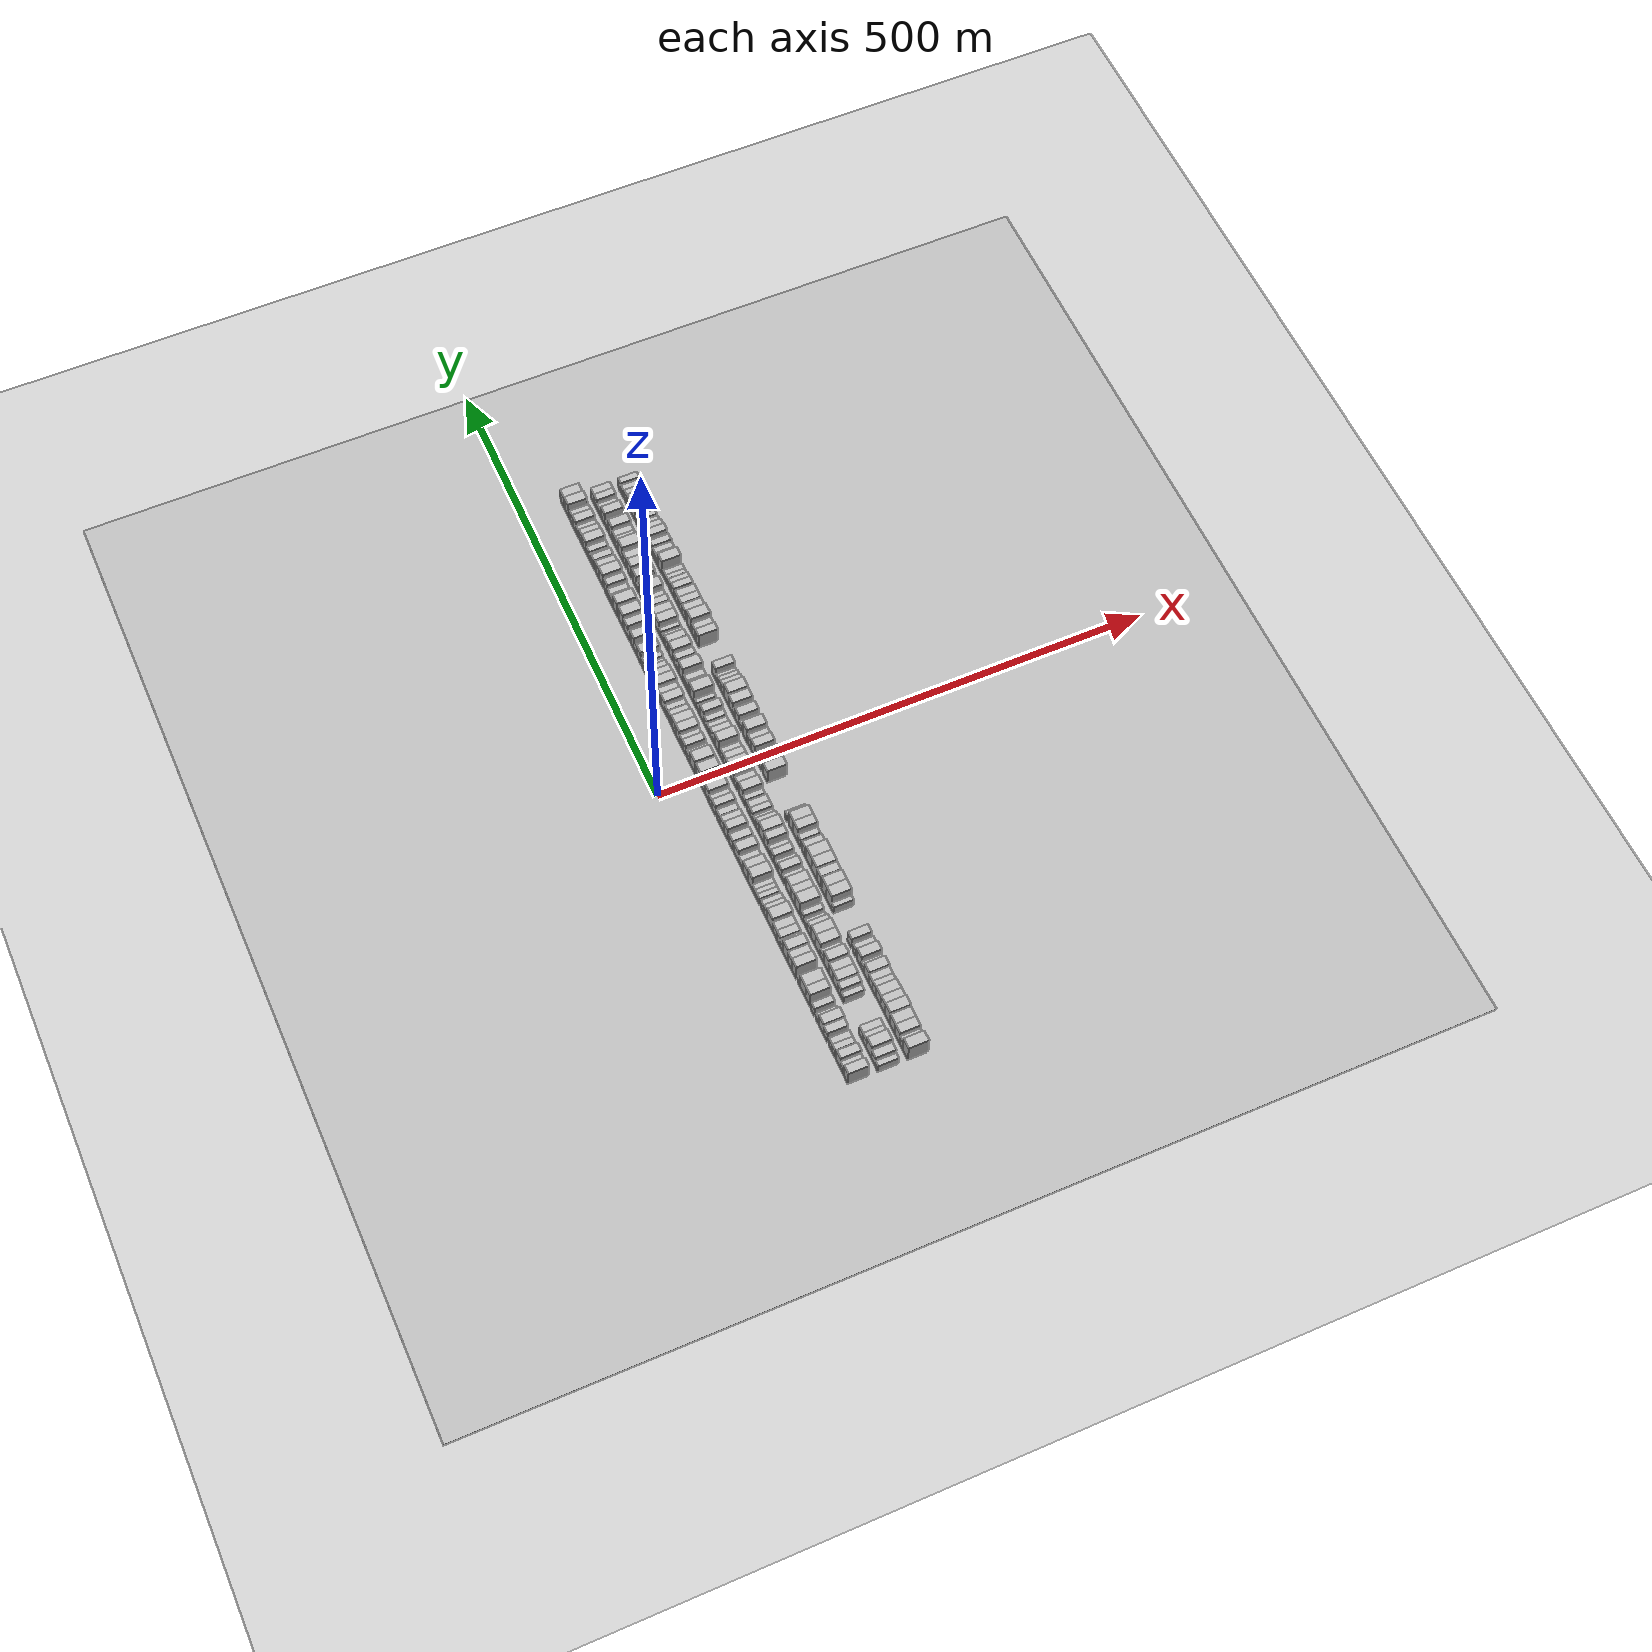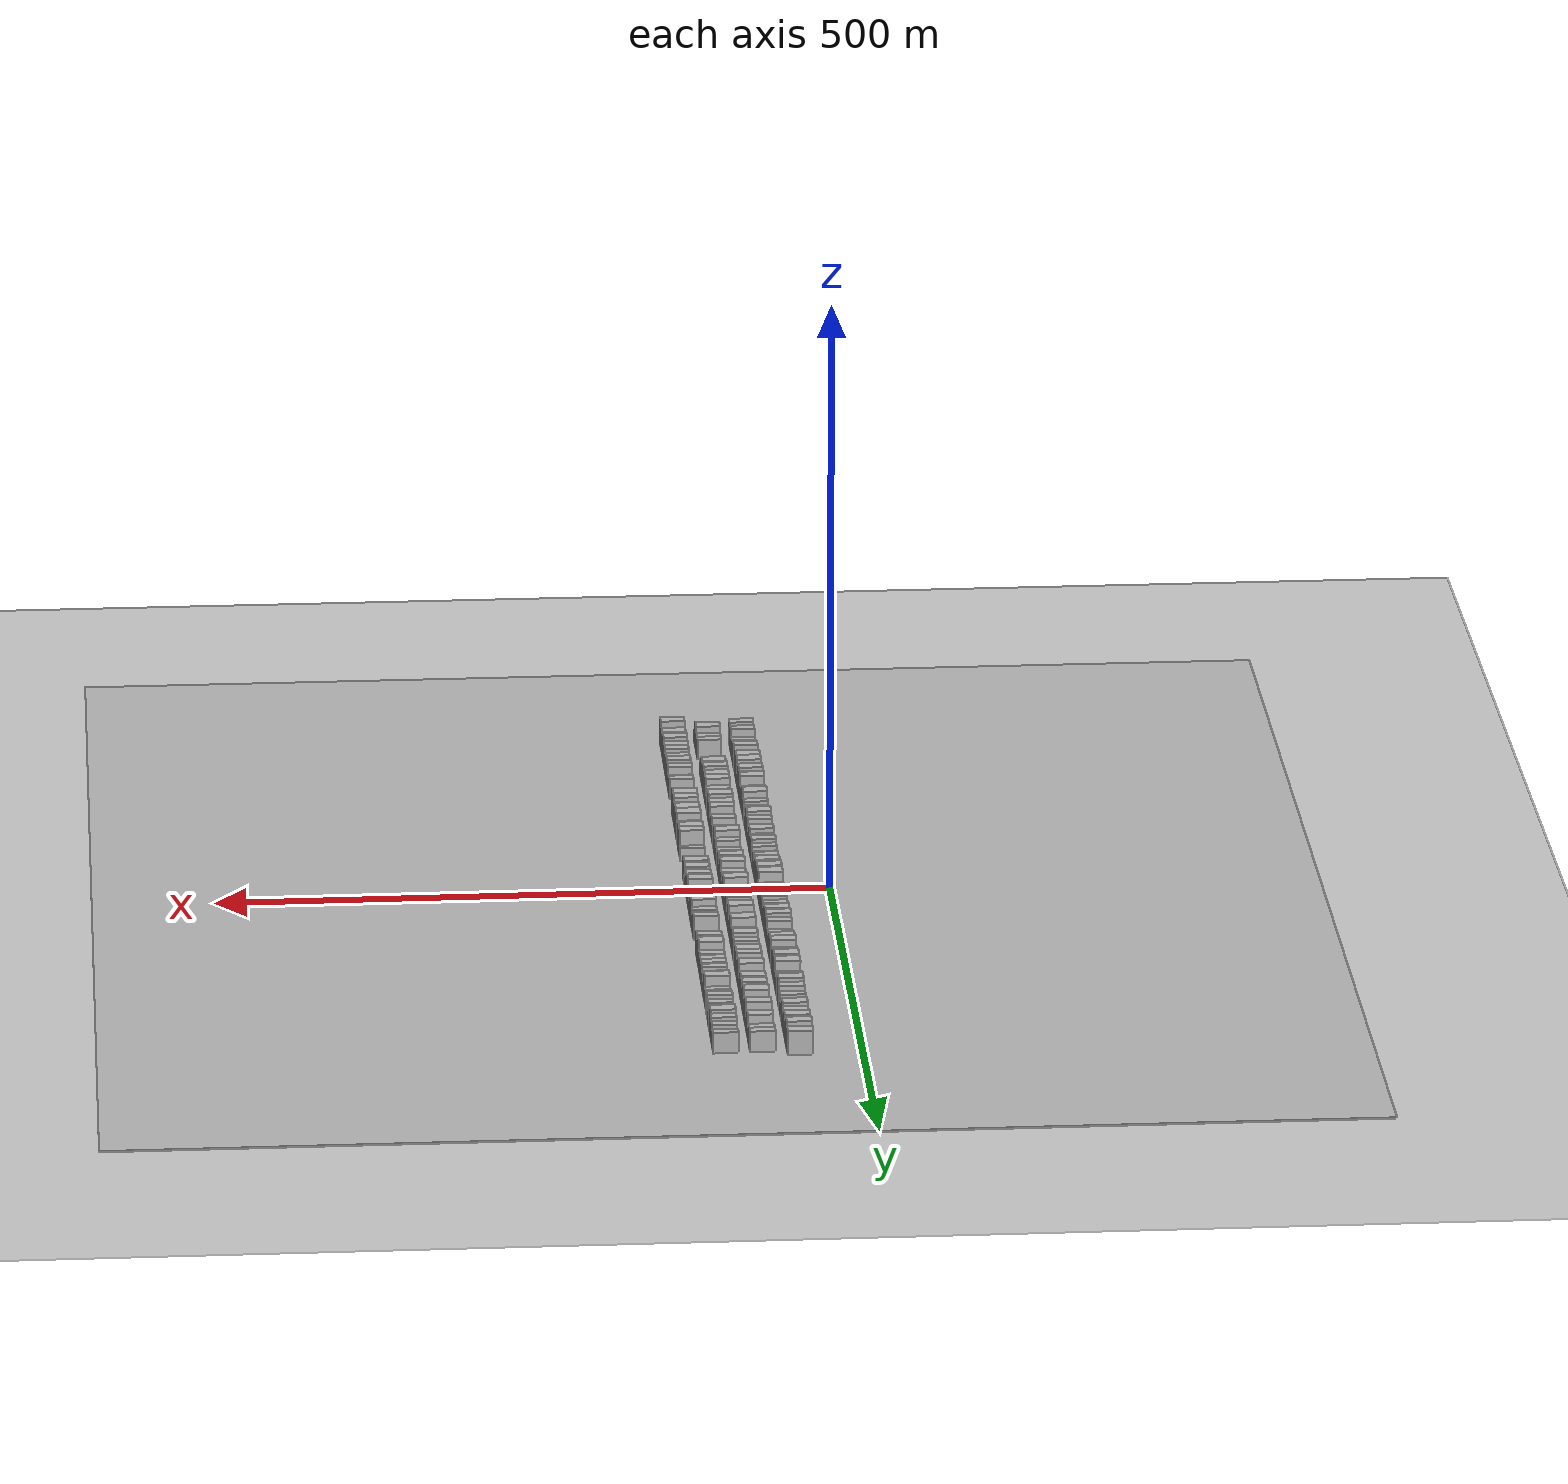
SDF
<?xml version="1.0" encoding="utf-8"?>

<sdf version="1.6">

   <world name="default">

      <gui fullscreen="0">

         <camera name="user_camera">

            <pose>-15 0 4.57585 0 0 0</pose>

            <view_controller>orbit</view_controller>

         </camera>

      </gui>

      <scene>

         <sky>

           <clouds>

             <speed>12</speed>

           </clouds>

         </sky>

         <ambient>0.4 0.4 0.4 1</ambient>

         <background>0.7 0.7 0.7 1</background>

         <shadows>1</shadows>

      </scene>

      <gravity>0 0 -9.8066</gravity>

      <magnetic_field>6e-06 2.3e-05 -4.2e-05</magnetic_field>

      <physics default="0" name="default_physics" type="ode">

         <ode>

            <solver>

               <type>quick</type>

               <iters>10</iters>

               <sor>1.0</sor>

               <use_dynamic_moi_rescaling>0</use_dynamic_moi_rescaling>

            </solver>

            <constraints>

               <cfm>0</cfm>

               <erp>0.2</erp>

               <contact_max_correcting_vel>100</contact_max_correcting_vel>

               <contact_surface_layer>0.001</contact_surface_layer>

            </constraints>

         </ode>

         <max_step_size>0.004</max_step_size>

         <real_time_factor>1</real_time_factor>

         <real_time_update_rate>250</real_time_update_rate>

      </physics>

      <light name="sun" type="directional">

         <cast_shadows>1</cast_shadows>

         <pose>0 0 10 0 0 0</pose>

         <diffuse>0.8 0.8 0.8 1</diffuse>

         <specular>0.2 0.2 0.2 1</specular>

         <attenuation>

            <range>1000</range>

            <constant>0.9</constant>

            <linear>0.01</linear>

            <quadratic>0.001</quadratic>

         </attenuation>

         <direction>-0.5 0.1 -0.9</direction>

      </light>

      <include>

         <name>ground_plane_1</name>

         <uri>model://HANNAS_ground_plane</uri>

         <pose>0 0 0  0 0 0</pose>

      </include>

      <include>

         <name>ground_plane_2</name>

         <uri>model://HANNAS_ground_plane</uri>

         <pose>100 0 0  0 0 0</pose>

      </include>

      <model name="building_1">

         <static>1</static>

         <pose frame="">50.0000 -331.4374 0 0.000000 0.000000 0.000000</pose>

         <link name="link">

            <pose frame="">0 0 10.50 0 0 0</pose>

            <collision name="collision">

               <geometry>

                  <box>

                     <size>20.0000 9.1252 21.0000</size>

                  </box>

               </geometry>

               <max_contacts>10</max_contacts>

               <surface>

                  <contact>

                     <ode/>

                  </contact>

                  <bounce/>

                  <friction>

                     <torsional>

                        <ode/>

                     </torsional>

                     <ode/>

                  </friction>

               </surface>

            </collision>

            <visual name="visual">

               <cast_shadows>0</cast_shadows>

               <geometry>

                  <box>

                     <size>20.0000 9.1252 21.0000</size>

                  </box>

               </geometry>

               <material>

                  <script>

                     <uri>model://HANNAS_wall/materials/scripts</uri>

                     <uri>model://HANNAS_wall/materials/textures</uri>

                     <name>vrc/HANNAS_wall</name>

                  </script>

               </material>

            </visual>

            <self_collide>0</self_collide>

            <enable_wind>0</enable_wind>

            <kinematic>0</kinematic>

         </link>

      </model>

      <model name="building_2">

         <static>1</static>

         <pose frame="">50.0000 -322.8205 0 0.000000 0.000000 0.000000</pose>

         <link name="link">

            <pose frame="">0 0 7.50 0 0 0</pose>

            <collision name="collision">

               <geometry>

                  <box>

                     <size>20.0000 6.1086 15.0000</size>

                  </box>

               </geometry>

               <max_contacts>10</max_contacts>

               <surface>

                  <contact>

                     <ode/>

                  </contact>

                  <bounce/>

                  <friction>

                     <torsional>

                        <ode/>

                     </torsional>

                     <ode/>

                  </friction>

               </surface>

            </collision>

            <visual name="visual">

               <cast_shadows>0</cast_shadows>

               <geometry>

                  <box>

                     <size>20.0000 6.1086 15.0000</size>

                  </box>

               </geometry>

               <material>

                  <script>

                     <uri>model://HANNAS_wall/materials/scripts</uri>

                     <uri>model://HANNAS_wall/materials/textures</uri>

                     <name>vrc/HANNAS_wall</name>

                  </script>

               </material>

            </visual>

            <self_collide>0</self_collide>

            <enable_wind>0</enable_wind>

            <kinematic>0</kinematic>

         </link>

      </model>

      <model name="building_3">

         <static>1</static>

         <pose frame="">50.0000 -315.4396 0 0.000000 0.000000 0.000000</pose>

         <link name="link">

            <pose frame="">0 0 10.50 0 0 0</pose>

            <collision name="collision">

               <geometry>

                  <box>

                     <size>20.0000 8.6531 21.0000</size>

                  </box>

               </geometry>

               <max_contacts>10</max_contacts>

               <surface>

                  <contact>

                     <ode/>

                  </contact>

                  <bounce/>

                  <friction>

                     <torsional>

                        <ode/>

                     </torsional>

                     <ode/>

                  </friction>

               </surface>

            </collision>

            <visual name="visual">

               <cast_shadows>0</cast_shadows>

               <geometry>

                  <box>

                     <size>20.0000 8.6531 21.0000</size>

                  </box>

               </geometry>

               <material>

                  <script>

                     <uri>model://HANNAS_wall/materials/scripts</uri>

                     <uri>model://HANNAS_wall/materials/textures</uri>

                     <name>vrc/HANNAS_wall</name>

                  </script>

               </material>

            </visual>

            <self_collide>0</self_collide>

            <enable_wind>0</enable_wind>

            <kinematic>0</kinematic>

         </link>

      </model>

      <model name="building_4">

         <static>1</static>

         <pose frame="">50.0000 -304.8928 0 0.000000 0.000000 0.000000</pose>

         <link name="link">

            <pose frame="">0 0 7.50 0 0 0</pose>

            <collision name="collision">

               <geometry>

                  <box>

                     <size>20.0000 6.4405 15.0000</size>

                  </box>

               </geometry>

               <max_contacts>10</max_contacts>

               <surface>

                  <contact>

                     <ode/>

                  </contact>

                  <bounce/>

                  <friction>

                     <torsional>

                        <ode/>

                     </torsional>

                     <ode/>

                  </friction>

               </surface>

            </collision>

            <visual name="visual">

               <cast_shadows>0</cast_shadows>

               <geometry>

                  <box>

                     <size>20.0000 6.4405 15.0000</size>

                  </box>

               </geometry>

               <material>

                  <script>

                     <uri>model://HANNAS_wall/materials/scripts</uri>

                     <uri>model://HANNAS_wall/materials/textures</uri>

                     <name>vrc/HANNAS_wall</name>

                  </script>

               </material>

            </visual>

            <self_collide>0</self_collide>

            <enable_wind>0</enable_wind>

            <kinematic>0</kinematic>

         </link>

      </model>

      <model name="building_5">

         <static>1</static>

         <pose frame="">50.0000 -298.2574 0 0.000000 0.000000 0.000000</pose>

         <link name="link">

            <pose frame="">0 0 7.50 0 0 0</pose>

            <collision name="collision">

               <geometry>

                  <box>

                     <size>20.0000 6.8302 15.0000</size>

                  </box>

               </geometry>

               <max_contacts>10</max_contacts>

               <surface>

                  <contact>

                     <ode/>

                  </contact>

                  <bounce/>

                  <friction>

                     <torsional>

                        <ode/>

                     </torsional>

                     <ode/>

                  </friction>

               </surface>

            </collision>

            <visual name="visual">

               <cast_shadows>0</cast_shadows>

               <geometry>

                  <box>

                     <size>20.0000 6.8302 15.0000</size>

                  </box>

               </geometry>

               <material>

                  <script>

                     <uri>model://HANNAS_wall/materials/scripts</uri>

                     <uri>model://HANNAS_wall/materials/textures</uri>

                     <name>vrc/HANNAS_wall</name>

                  </script>

               </material>

            </visual>

            <self_collide>0</self_collide>

            <enable_wind>0</enable_wind>

            <kinematic>0</kinematic>

         </link>

      </model>

      <model name="building_6">

         <static>1</static>

         <pose frame="">50.0000 -287.6913 0 0.000000 0.000000 0.000000</pose>

         <link name="link">

            <pose frame="">0 0 9.00 0 0 0</pose>

            <collision name="collision">

               <geometry>

                  <box>

                     <size>20.0000 8.3021 18.0000</size>

                  </box>

               </geometry>

               <max_contacts>10</max_contacts>

               <surface>

                  <contact>

                     <ode/>

                  </contact>

                  <bounce/>

                  <friction>

                     <torsional>

                        <ode/>

                     </torsional>

                     <ode/>

                  </friction>

               </surface>

            </collision>

            <visual name="visual">

               <cast_shadows>0</cast_shadows>

               <geometry>

                  <box>

                     <size>20.0000 8.3021 18.0000</size>

                  </box>

               </geometry>

               <material>

                  <script>

                     <uri>model://HANNAS_wall/materials/scripts</uri>

                     <uri>model://HANNAS_wall/materials/textures</uri>

                     <name>vrc/HANNAS_wall</name>

                  </script>

               </material>

            </visual>

            <self_collide>0</self_collide>

            <enable_wind>0</enable_wind>

            <kinematic>0</kinematic>

         </link>

      </model>

      <model name="building_7">

         <static>1</static>

         <pose frame="">50.0000 -278.5388 0 0.000000 0.000000 0.000000</pose>

         <link name="link">

            <pose frame="">0 0 10.50 0 0 0</pose>

            <collision name="collision">

               <geometry>

                  <box>

                     <size>20.0000 10.0028 21.0000</size>

                  </box>

               </geometry>

               <max_contacts>10</max_contacts>

               <surface>

                  <contact>

                     <ode/>

                  </contact>

                  <bounce/>

                  <friction>

                     <torsional>

                        <ode/>

                     </torsional>

                     <ode/>

                  </friction>

               </surface>

            </collision>

            <visual name="visual">

               <cast_shadows>0</cast_shadows>

               <geometry>

                  <box>

                     <size>20.0000 10.0028 21.0000</size>

                  </box>

               </geometry>

               <material>

                  <script>

                     <uri>model://HANNAS_wall/materials/scripts</uri>

                     <uri>model://HANNAS_wall/materials/textures</uri>

                     <name>vrc/HANNAS_wall</name>

                  </script>

               </material>

            </visual>

            <self_collide>0</self_collide>

            <enable_wind>0</enable_wind>

            <kinematic>0</kinematic>

         </link>

      </model>

      <model name="building_8">

         <static>1</static>

         <pose frame="">50.0000 -269.7863 0 0.000000 0.000000 0.000000</pose>

         <link name="link">

            <pose frame="">0 0 6.00 0 0 0</pose>

            <collision name="collision">

               <geometry>

                  <box>

                     <size>20.0000 5.5023 12.0000</size>

                  </box>

               </geometry>

               <max_contacts>10</max_contacts>

               <surface>

                  <contact>

                     <ode/>

                  </contact>

                  <bounce/>

                  <friction>

                     <torsional>

                        <ode/>

                     </torsional>

                     <ode/>

                  </friction>

               </surface>

            </collision>

            <visual name="visual">

               <cast_shadows>0</cast_shadows>

               <geometry>

                  <box>

                     <size>20.0000 5.5023 12.0000</size>

                  </box>

               </geometry>

               <material>

                  <script>

                     <uri>model://HANNAS_wall/materials/scripts</uri>

                     <uri>model://HANNAS_wall/materials/textures</uri>

                     <name>vrc/HANNAS_wall</name>

                  </script>

               </material>

            </visual>

            <self_collide>0</self_collide>

            <enable_wind>0</enable_wind>

            <kinematic>0</kinematic>

         </link>

      </model>

      <model name="building_9">

         <static>1</static>

         <pose frame="">50.0000 -260.5613 0 0.000000 0.000000 0.000000</pose>

         <link name="link">

            <pose frame="">0 0 7.50 0 0 0</pose>

            <collision name="collision">

               <geometry>

                  <box>

                     <size>20.0000 6.9476 15.0000</size>

                  </box>

               </geometry>

               <max_contacts>10</max_contacts>

               <surface>

                  <contact>

                     <ode/>

                  </contact>

                  <bounce/>

                  <friction>

                     <torsional>

                        <ode/>

                     </torsional>

                     <ode/>

                  </friction>

               </surface>

            </collision>

            <visual name="visual">

               <cast_shadows>0</cast_shadows>

               <geometry>

                  <box>

                     <size>20.0000 6.9476 15.0000</size>

                  </box>

               </geometry>

               <material>

                  <script>

                     <uri>model://HANNAS_wall/materials/scripts</uri>

                     <uri>model://HANNAS_wall/materials/textures</uri>

                     <name>vrc/HANNAS_wall</name>

                  </script>

               </material>

            </visual>

            <self_collide>0</self_collide>

            <enable_wind>0</enable_wind>

            <kinematic>0</kinematic>

         </link>

      </model>

      <model name="building_10">

         <static>1</static>

         <pose frame="">50.0000 -249.1373 0 0.000000 0.000000 0.000000</pose>

         <link name="link">

            <pose frame="">0 0 12.00 0 0 0</pose>

            <collision name="collision">

               <geometry>

                  <box>

                     <size>20.0000 9.9005 24.0000</size>

                  </box>

               </geometry>

               <max_contacts>10</max_contacts>

               <surface>

                  <contact>

                     <ode/>

                  </contact>

                  <bounce/>

                  <friction>

                     <torsional>

                        <ode/>

                     </torsional>

                     <ode/>

                  </friction>

               </surface>

            </collision>

            <visual name="visual">

               <cast_shadows>0</cast_shadows>

               <geometry>

                  <box>

                     <size>20.0000 9.9005 24.0000</size>

                  </box>

               </geometry>

               <material>

                  <script>

                     <uri>model://HANNAS_wall/materials/scripts</uri>

                     <uri>model://HANNAS_wall/materials/textures</uri>

                     <name>vrc/HANNAS_wall</name>

                  </script>

               </material>

            </visual>

            <self_collide>0</self_collide>

            <enable_wind>0</enable_wind>

            <kinematic>0</kinematic>

         </link>

      </model>

      <model name="building_11">

         <static>1</static>

         <pose frame="">50.0000 -238.2753 0 0.000000 0.000000 0.000000</pose>

         <link name="link">

            <pose frame="">0 0 12.00 0 0 0</pose>

            <collision name="collision">

               <geometry>

                  <box>

                     <size>20.0000 11.8236 24.0000</size>

                  </box>

               </geometry>

               <max_contacts>10</max_contacts>

               <surface>

                  <contact>

                     <ode/>

                  </contact>

                  <bounce/>

                  <friction>

                     <torsional>

                        <ode/>

                     </torsional>

                     <ode/>

                  </friction>

               </surface>

            </collision>

            <visual name="visual">

               <cast_shadows>0</cast_shadows>

               <geometry>

                  <box>

                     <size>20.0000 11.8236 24.0000</size>

                  </box>

               </geometry>

               <material>

                  <script>

                     <uri>model://HANNAS_wall/materials/scripts</uri>

                     <uri>model://HANNAS_wall/materials/textures</uri>

                     <name>vrc/HANNAS_wall</name>

                  </script>

               </material>

            </visual>

            <self_collide>0</self_collide>

            <enable_wind>0</enable_wind>

            <kinematic>0</kinematic>

         </link>

      </model>

      <model name="building_12">

         <static>1</static>

         <pose frame="">50.0000 -229.6843 0 0.000000 0.000000 0.000000</pose>

         <link name="link">

            <pose frame="">0 0 6.00 0 0 0</pose>

            <collision name="collision">

               <geometry>

                  <box>

                     <size>20.0000 5.3582 12.0000</size>

                  </box>

               </geometry>

               <max_contacts>10</max_contacts>

               <surface>

                  <contact>

                     <ode/>

                  </contact>

                  <bounce/>

                  <friction>

                     <torsional>

                        <ode/>

                     </torsional>

                     <ode/>

                  </friction>

               </surface>

            </collision>

            <visual name="visual">

               <cast_shadows>0</cast_shadows>

               <geometry>

                  <box>

                     <size>20.0000 5.3582 12.0000</size>

                  </box>

               </geometry>

               <material>

                  <script>

                     <uri>model://HANNAS_wall/materials/scripts</uri>

                     <uri>model://HANNAS_wall/materials/textures</uri>

                     <name>vrc/HANNAS_wall</name>

                  </script>

               </material>

            </visual>

            <self_collide>0</self_collide>

            <enable_wind>0</enable_wind>

            <kinematic>0</kinematic>

         </link>

      </model>

      <model name="building_13">

         <static>1</static>

         <pose frame="">50.0000 -219.1030 0 0.000000 0.000000 0.000000</pose>

         <link name="link">

            <pose frame="">0 0 12.00 0 0 0</pose>

            <collision name="collision">

               <geometry>

                  <box>

                     <size>20.0000 9.8044 24.0000</size>

                  </box>

               </geometry>

               <max_contacts>10</max_contacts>

               <surface>

                  <contact>

                     <ode/>

                  </contact>

                  <bounce/>

                  <friction>

                     <torsional>

                        <ode/>

                     </torsional>

                     <ode/>

                  </friction>

               </surface>

            </collision>

            <visual name="visual">

               <cast_shadows>0</cast_shadows>

               <geometry>

                  <box>

                     <size>20.0000 9.8044 24.0000</size>

                  </box>

               </geometry>

               <material>

                  <script>

                     <uri>model://HANNAS_wall/materials/scripts</uri>

                     <uri>model://HANNAS_wall/materials/textures</uri>

                     <name>vrc/HANNAS_wall</name>

                  </script>

               </material>

            </visual>

            <self_collide>0</self_collide>

            <enable_wind>0</enable_wind>

            <kinematic>0</kinematic>

         </link>

      </model>

      <model name="building_14">

         <static>1</static>

         <pose frame="">50.0000 -209.7361 0 0.000000 0.000000 0.000000</pose>

         <link name="link">

            <pose frame="">0 0 10.50 0 0 0</pose>

            <collision name="collision">

               <geometry>

                  <box>

                     <size>20.0000 8.9294 21.0000</size>

                  </box>

               </geometry>

               <max_contacts>10</max_contacts>

               <surface>

                  <contact>

                     <ode/>

                  </contact>

                  <bounce/>

                  <friction>

                     <torsional>

                        <ode/>

                     </torsional>

                     <ode/>

                  </friction>

               </surface>

            </collision>

            <visual name="visual">

               <cast_shadows>0</cast_shadows>

               <geometry>

                  <box>

                     <size>20.0000 8.9294 21.0000</size>

                  </box>

               </geometry>

               <material>

                  <script>

                     <uri>model://HANNAS_wall/materials/scripts</uri>

                     <uri>model://HANNAS_wall/materials/textures</uri>

                     <name>vrc/HANNAS_wall</name>

                  </script>

               </material>

            </visual>

            <self_collide>0</self_collide>

            <enable_wind>0</enable_wind>

            <kinematic>0</kinematic>

         </link>

      </model>

      <model name="building_15">

         <static>1</static>

         <pose frame="">50.0000 -200.1119 0 0.000000 0.000000 0.000000</pose>

         <link name="link">

            <pose frame="">0 0 12.00 0 0 0</pose>

            <collision name="collision">

               <geometry>

                  <box>

                     <size>20.0000 10.3190 24.0000</size>

                  </box>

               </geometry>

               <max_contacts>10</max_contacts>

               <surface>

                  <contact>

                     <ode/>

                  </contact>

                  <bounce/>

                  <friction>

                     <torsional>

                        <ode/>

                     </torsional>

                     <ode/>

                  </friction>

               </surface>

            </collision>

            <visual name="visual">

               <cast_shadows>0</cast_shadows>

               <geometry>

                  <box>

                     <size>20.0000 10.3190 24.0000</size>

                  </box>

               </geometry>

               <material>

                  <script>

                     <uri>model://HANNAS_wall/materials/scripts</uri>

                     <uri>model://HANNAS_wall/materials/textures</uri>

                     <name>vrc/HANNAS_wall</name>

                  </script>

               </material>

            </visual>

            <self_collide>0</self_collide>

            <enable_wind>0</enable_wind>

            <kinematic>0</kinematic>

         </link>

      </model>

      <model name="building_16">

         <static>1</static>

         <pose frame="">50.0000 -191.8683 0 0.000000 0.000000 0.000000</pose>

         <link name="link">

            <pose frame="">0 0 7.50 0 0 0</pose>

            <collision name="collision">

               <geometry>

                  <box>

                     <size>20.0000 6.1682 15.0000</size>

                  </box>

               </geometry>

               <max_contacts>10</max_contacts>

               <surface>

                  <contact>

                     <ode/>

                  </contact>

                  <bounce/>

                  <friction>

                     <torsional>

                        <ode/>

                     </torsional>

                     <ode/>

                  </friction>

               </surface>

            </collision>

            <visual name="visual">

               <cast_shadows>0</cast_shadows>

               <geometry>

                  <box>

                     <size>20.0000 6.1682 15.0000</size>

                  </box>

               </geometry>

               <material>

                  <script>

                     <uri>model://HANNAS_wall/materials/scripts</uri>

                     <uri>model://HANNAS_wall/materials/textures</uri>

                     <name>vrc/HANNAS_wall</name>

                  </script>

               </material>

            </visual>

            <self_collide>0</self_collide>

            <enable_wind>0</enable_wind>

            <kinematic>0</kinematic>

         </link>

      </model>

      <model name="building_17">

         <static>1</static>

         <pose frame="">50.0000 -184.5009 0 0.000000 0.000000 0.000000</pose>

         <link name="link">

            <pose frame="">0 0 9.00 0 0 0</pose>

            <collision name="collision">

               <geometry>

                  <box>

                     <size>20.0000 8.5665 18.0000</size>

                  </box>

               </geometry>

               <max_contacts>10</max_contacts>

               <surface>

                  <contact>

                     <ode/>

                  </contact>

                  <bounce/>

                  <friction>

                     <torsional>

                        <ode/>

                     </torsional>

                     <ode/>

                  </friction>

               </surface>

            </collision>

            <visual name="visual">

               <cast_shadows>0</cast_shadows>

               <geometry>

                  <box>

                     <size>20.0000 8.5665 18.0000</size>

                  </box>

               </geometry>

               <material>

                  <script>

                     <uri>model://HANNAS_wall/materials/scripts</uri>

                     <uri>model://HANNAS_wall/materials/textures</uri>

                     <name>vrc/HANNAS_wall</name>

                  </script>

               </material>

            </visual>

            <self_collide>0</self_collide>

            <enable_wind>0</enable_wind>

            <kinematic>0</kinematic>

         </link>

      </model>

      <model name="building_18">

         <static>1</static>

         <pose frame="">50.0000 -175.7583 0 0.000000 0.000000 0.000000</pose>

         <link name="link">

            <pose frame="">0 0 9.00 0 0 0</pose>

            <collision name="collision">

               <geometry>

                  <box>

                     <size>20.0000 8.9187 18.0000</size>

                  </box>

               </geometry>

               <max_contacts>10</max_contacts>

               <surface>

                  <contact>

                     <ode/>

                  </contact>

                  <bounce/>

                  <friction>

                     <torsional>

                        <ode/>

                     </torsional>

                     <ode/>

                  </friction>

               </surface>

            </collision>

            <visual name="visual">

               <cast_shadows>0</cast_shadows>

               <geometry>

                  <box>

                     <size>20.0000 8.9187 18.0000</size>

                  </box>

               </geometry>

               <material>

                  <script>

                     <uri>model://HANNAS_wall/materials/scripts</uri>

                     <uri>model://HANNAS_wall/materials/textures</uri>

                     <name>vrc/HANNAS_wall</name>

                  </script>

               </material>

            </visual>

            <self_collide>0</self_collide>

            <enable_wind>0</enable_wind>

            <kinematic>0</kinematic>

         </link>

      </model>

      <model name="building_19">

         <static>1</static>

         <pose frame="">50.0000 -165.3610 0 0.000000 0.000000 0.000000</pose>

         <link name="link">

            <pose frame="">0 0 12.00 0 0 0</pose>

            <collision name="collision">

               <geometry>

                  <box>

                     <size>20.0000 11.8758 24.0000</size>

                  </box>

               </geometry>

               <max_contacts>10</max_contacts>

               <surface>

                  <contact>

                     <ode/>

                  </contact>

                  <bounce/>

                  <friction>

                     <torsional>

                        <ode/>

                     </torsional>

                     <ode/>

                  </friction>

               </surface>

            </collision>

            <visual name="visual">

               <cast_shadows>0</cast_shadows>

               <geometry>

                  <box>

                     <size>20.0000 11.8758 24.0000</size>

                  </box>

               </geometry>

               <material>

                  <script>

                     <uri>model://HANNAS_wall/materials/scripts</uri>

                     <uri>model://HANNAS_wall/materials/textures</uri>

                     <name>vrc/HANNAS_wall</name>

                  </script>

               </material>

            </visual>

            <self_collide>0</self_collide>

            <enable_wind>0</enable_wind>

            <kinematic>0</kinematic>

         </link>

      </model>

      <model name="building_20">

         <static>1</static>

         <pose frame="">50.0000 -155.6703 0 0.000000 0.000000 0.000000</pose>

         <link name="link">

            <pose frame="">0 0 9.00 0 0 0</pose>

            <collision name="collision">

               <geometry>

                  <box>

                     <size>20.0000 7.5056 18.0000</size>

                  </box>

               </geometry>

               <max_contacts>10</max_contacts>

               <surface>

                  <contact>

                     <ode/>

                  </contact>

                  <bounce/>

                  <friction>

                     <torsional>

                        <ode/>

                     </torsional>

                     <ode/>

                  </friction>

               </surface>

            </collision>

            <visual name="visual">

               <cast_shadows>0</cast_shadows>

               <geometry>

                  <box>

                     <size>20.0000 7.5056 18.0000</size>

                  </box>

               </geometry>

               <material>

                  <script>

                     <uri>model://HANNAS_wall/materials/scripts</uri>

                     <uri>model://HANNAS_wall/materials/textures</uri>

                     <name>vrc/HANNAS_wall</name>

                  </script>

               </material>

            </visual>

            <self_collide>0</self_collide>

            <enable_wind>0</enable_wind>

            <kinematic>0</kinematic>

         </link>

      </model>

      <model name="building_21">

         <static>1</static>

         <pose frame="">50.0000 -148.4267 0 0.000000 0.000000 0.000000</pose>

         <link name="link">

            <pose frame="">0 0 7.50 0 0 0</pose>

            <collision name="collision">

               <geometry>

                  <box>

                     <size>20.0000 6.9815 15.0000</size>

                  </box>

               </geometry>

               <max_contacts>10</max_contacts>

               <surface>

                  <contact>

                     <ode/>

                  </contact>

                  <bounce/>

                  <friction>

                     <torsional>

                        <ode/>

                     </torsional>

                     <ode/>

                  </friction>

               </surface>

            </collision>

            <visual name="visual">

               <cast_shadows>0</cast_shadows>

               <geometry>

                  <box>

                     <size>20.0000 6.9815 15.0000</size>

                  </box>

               </geometry>

               <material>

                  <script>

                     <uri>model://HANNAS_wall/materials/scripts</uri>

                     <uri>model://HANNAS_wall/materials/textures</uri>

                     <name>vrc/HANNAS_wall</name>

                  </script>

               </material>

            </visual>

            <self_collide>0</self_collide>

            <enable_wind>0</enable_wind>

            <kinematic>0</kinematic>

         </link>

      </model>

      <model name="building_22">

         <static>1</static>

         <pose frame="">50.0000 -139.1148 0 0.000000 0.000000 0.000000</pose>

         <link name="link">

            <pose frame="">0 0 6.00 0 0 0</pose>

            <collision name="collision">

               <geometry>

                  <box>

                     <size>20.0000 5.6423 12.0000</size>

                  </box>

               </geometry>

               <max_contacts>10</max_contacts>

               <surface>

                  <contact>

                     <ode/>

                  </contact>

                  <bounce/>

                  <friction>

                     <torsional>

                        <ode/>

                     </torsional>

                     <ode/>

                  </friction>

               </surface>

            </collision>

            <visual name="visual">

               <cast_shadows>0</cast_shadows>

               <geometry>

                  <box>

                     <size>20.0000 5.6423 12.0000</size>

                  </box>

               </geometry>

               <material>

                  <script>

                     <uri>model://HANNAS_wall/materials/scripts</uri>

                     <uri>model://HANNAS_wall/materials/textures</uri>

                     <name>vrc/HANNAS_wall</name>

                  </script>

               </material>

            </visual>

            <self_collide>0</self_collide>

            <enable_wind>0</enable_wind>

            <kinematic>0</kinematic>

         </link>

      </model>

      <model name="building_23">

         <static>1</static>

         <pose frame="">50.0000 -133.8215 0 0.000000 0.000000 0.000000</pose>

         <link name="link">

            <pose frame="">0 0 6.00 0 0 0</pose>

            <collision name="collision">

               <geometry>

                  <box>

                     <size>20.0000 4.9443 12.0000</size>

                  </box>

               </geometry>

               <max_contacts>10</max_contacts>

               <surface>

                  <contact>

                     <ode/>

                  </contact>

                  <bounce/>

                  <friction>

                     <torsional>

                        <ode/>

                     </torsional>

                     <ode/>

                  </friction>

               </surface>

            </collision>

            <visual name="visual">

               <cast_shadows>0</cast_shadows>

               <geometry>

                  <box>

                     <size>20.0000 4.9443 12.0000</size>

                  </box>

               </geometry>

               <material>

                  <script>

                     <uri>model://HANNAS_wall/materials/scripts</uri>

                     <uri>model://HANNAS_wall/materials/textures</uri>

                     <name>vrc/HANNAS_wall</name>

                  </script>

               </material>

            </visual>

            <self_collide>0</self_collide>

            <enable_wind>0</enable_wind>

            <kinematic>0</kinematic>

         </link>

      </model>

      <model name="building_24">

         <static>1</static>

         <pose frame="">50.0000 -128.6585 0 0.000000 0.000000 0.000000</pose>

         <link name="link">

            <pose frame="">0 0 6.00 0 0 0</pose>

            <collision name="collision">

               <geometry>

                  <box>

                     <size>20.0000 5.3816 12.0000</size>

                  </box>

               </geometry>

               <max_contacts>10</max_contacts>

               <surface>

                  <contact>

                     <ode/>

                  </contact>

                  <bounce/>

                  <friction>

                     <torsional>

                        <ode/>

                     </torsional>

                     <ode/>

                  </friction>

               </surface>

            </collision>

            <visual name="visual">

               <cast_shadows>0</cast_shadows>

               <geometry>

                  <box>

                     <size>20.0000 5.3816 12.0000</size>

                  </box>

               </geometry>

               <material>

                  <script>

                     <uri>model://HANNAS_wall/materials/scripts</uri>

                     <uri>model://HANNAS_wall/materials/textures</uri>

                     <name>vrc/HANNAS_wall</name>

                  </script>

               </material>

            </visual>

            <self_collide>0</self_collide>

            <enable_wind>0</enable_wind>

            <kinematic>0</kinematic>

         </link>

      </model>

      <model name="building_25">

         <static>1</static>

         <pose frame="">50.0000 -120.2226 0 0.000000 0.000000 0.000000</pose>

         <link name="link">

            <pose frame="">0 0 12.00 0 0 0</pose>

            <collision name="collision">

               <geometry>

                  <box>

                     <size>20.0000 11.4903 24.0000</size>

                  </box>

               </geometry>

               <max_contacts>10</max_contacts>

               <surface>

                  <contact>

                     <ode/>

                  </contact>

                  <bounce/>

                  <friction>

                     <torsional>

                        <ode/>

                     </torsional>

                     <ode/>

                  </friction>

               </surface>

            </collision>

            <visual name="visual">

               <cast_shadows>0</cast_shadows>

               <geometry>

                  <box>

                     <size>20.0000 11.4903 24.0000</size>

                  </box>

               </geometry>

               <material>

                  <script>

                     <uri>model://HANNAS_wall/materials/scripts</uri>

                     <uri>model://HANNAS_wall/materials/textures</uri>

                     <name>vrc/HANNAS_wall</name>

                  </script>

               </material>

            </visual>

            <self_collide>0</self_collide>

            <enable_wind>0</enable_wind>

            <kinematic>0</kinematic>

         </link>

      </model>

      <model name="building_26">

         <static>1</static>

         <pose frame="">50.0000 -109.5448 0 0.000000 0.000000 0.000000</pose>

         <link name="link">

            <pose frame="">0 0 10.50 0 0 0</pose>

            <collision name="collision">

               <geometry>

                  <box>

                     <size>20.0000 9.8654 21.0000</size>

                  </box>

               </geometry>

               <max_contacts>10</max_contacts>

               <surface>

                  <contact>

                     <ode/>

                  </contact>

                  <bounce/>

                  <friction>

                     <torsional>

                        <ode/>

                     </torsional>

                     <ode/>

                  </friction>

               </surface>

            </collision>

            <visual name="visual">

               <cast_shadows>0</cast_shadows>

               <geometry>

                  <box>

                     <size>20.0000 9.8654 21.0000</size>

                  </box>

               </geometry>

               <material>

                  <script>

                     <uri>model://HANNAS_wall/materials/scripts</uri>

                     <uri>model://HANNAS_wall/materials/textures</uri>

                     <name>vrc/HANNAS_wall</name>

                  </script>

               </material>

            </visual>

            <self_collide>0</self_collide>

            <enable_wind>0</enable_wind>

            <kinematic>0</kinematic>

         </link>

      </model>

      <model name="building_27">

         <static>1</static>

         <pose frame="">50.0000 -102.1671 0 0.000000 0.000000 0.000000</pose>

         <link name="link">

            <pose frame="">0 0 6.00 0 0 0</pose>

            <collision name="collision">

               <geometry>

                  <box>

                     <size>20.0000 4.8900 12.0000</size>

                  </box>

               </geometry>

               <max_contacts>10</max_contacts>

               <surface>

                  <contact>

                     <ode/>

                  </contact>

                  <bounce/>

                  <friction>

                     <torsional>

                        <ode/>

                     </torsional>

                     <ode/>

                  </friction>

               </surface>

            </collision>

            <visual name="visual">

               <cast_shadows>0</cast_shadows>

               <geometry>

                  <box>

                     <size>20.0000 4.8900 12.0000</size>

                  </box>

               </geometry>

               <material>

                  <script>

                     <uri>model://HANNAS_wall/materials/scripts</uri>

                     <uri>model://HANNAS_wall/materials/textures</uri>

                     <name>vrc/HANNAS_wall</name>

                  </script>

               </material>

            </visual>

            <self_collide>0</self_collide>

            <enable_wind>0</enable_wind>

            <kinematic>0</kinematic>

         </link>

      </model>

      <model name="building_28">

         <static>1</static>

         <pose frame="">50.0000 -96.7376 0 0.000000 0.000000 0.000000</pose>

         <link name="link">

            <pose frame="">0 0 6.00 0 0 0</pose>

            <collision name="collision">

               <geometry>

                  <box>

                     <size>20.0000 5.9690 12.0000</size>

                  </box>

               </geometry>

               <max_contacts>10</max_contacts>

               <surface>

                  <contact>

                     <ode/>

                  </contact>

                  <bounce/>

                  <friction>

                     <torsional>

                        <ode/>

                     </torsional>

                     <ode/>

                  </friction>

               </surface>

            </collision>

            <visual name="visual">

               <cast_shadows>0</cast_shadows>

               <geometry>

                  <box>

                     <size>20.0000 5.9690 12.0000</size>

                  </box>

               </geometry>

               <material>

                  <script>

                     <uri>model://HANNAS_wall/materials/scripts</uri>

                     <uri>model://HANNAS_wall/materials/textures</uri>

                     <name>vrc/HANNAS_wall</name>

                  </script>

               </material>

            </visual>

            <self_collide>0</self_collide>

            <enable_wind>0</enable_wind>

            <kinematic>0</kinematic>

         </link>

      </model>

      <model name="building_29">

         <static>1</static>

         <pose frame="">50.0000 -88.7289 0 0.000000 0.000000 0.000000</pose>

         <link name="link">

            <pose frame="">0 0 10.50 0 0 0</pose>

            <collision name="collision">

               <geometry>

                  <box>

                     <size>20.0000 10.0484 21.0000</size>

                  </box>

               </geometry>

               <max_contacts>10</max_contacts>

               <surface>

                  <contact>

                     <ode/>

                  </contact>

                  <bounce/>

                  <friction>

                     <torsional>

                        <ode/>

                     </torsional>

                     <ode/>

                  </friction>

               </surface>

            </collision>

            <visual name="visual">

               <cast_shadows>0</cast_shadows>

               <geometry>

                  <box>

                     <size>20.0000 10.0484 21.0000</size>

                  </box>

               </geometry>

               <material>

                  <script>

                     <uri>model://HANNAS_wall/materials/scripts</uri>

                     <uri>model://HANNAS_wall/materials/textures</uri>

                     <name>vrc/HANNAS_wall</name>

                  </script>

               </material>

            </visual>

            <self_collide>0</self_collide>

            <enable_wind>0</enable_wind>

            <kinematic>0</kinematic>

         </link>

      </model>

      <model name="building_30">

         <static>1</static>

         <pose frame="">50.0000 -76.3814 0 0.000000 0.000000 0.000000</pose>

         <link name="link">

            <pose frame="">0 0 9.00 0 0 0</pose>

            <collision name="collision">

               <geometry>

                  <box>

                     <size>20.0000 8.6467 18.0000</size>

                  </box>

               </geometry>

               <max_contacts>10</max_contacts>

               <surface>

                  <contact>

                     <ode/>

                  </contact>

                  <bounce/>

                  <friction>

                     <torsional>

                        <ode/>

                     </torsional>

                     <ode/>

                  </friction>

               </surface>

            </collision>

            <visual name="visual">

               <cast_shadows>0</cast_shadows>

               <geometry>

                  <box>

                     <size>20.0000 8.6467 18.0000</size>

                  </box>

               </geometry>

               <material>

                  <script>

                     <uri>model://HANNAS_wall/materials/scripts</uri>

                     <uri>model://HANNAS_wall/materials/textures</uri>

                     <name>vrc/HANNAS_wall</name>

                  </script>

               </material>

            </visual>

            <self_collide>0</self_collide>

            <enable_wind>0</enable_wind>

            <kinematic>0</kinematic>

         </link>

      </model>

      <model name="building_31">

         <static>1</static>

         <pose frame="">50.0000 -64.4616 0 0.000000 0.000000 0.000000</pose>

         <link name="link">

            <pose frame="">0 0 10.50 0 0 0</pose>

            <collision name="collision">

               <geometry>

                  <box>

                     <size>20.0000 9.1930 21.0000</size>

                  </box>

               </geometry>

               <max_contacts>10</max_contacts>

               <surface>

                  <contact>

                     <ode/>

                  </contact>

                  <bounce/>

                  <friction>

                     <torsional>

                        <ode/>

                     </torsional>

                     <ode/>

                  </friction>

               </surface>

            </collision>

            <visual name="visual">

               <cast_shadows>0</cast_shadows>

               <geometry>

                  <box>

                     <size>20.0000 9.1930 21.0000</size>

                  </box>

               </geometry>

               <material>

                  <script>

                     <uri>model://HANNAS_wall/materials/scripts</uri>

                     <uri>model://HANNAS_wall/materials/textures</uri>

                     <name>vrc/HANNAS_wall</name>

                  </script>

               </material>

            </visual>

            <self_collide>0</self_collide>

            <enable_wind>0</enable_wind>

            <kinematic>0</kinematic>

         </link>

      </model>

      <model name="building_32">

         <static>1</static>

         <pose frame="">50.0000 -55.7582 0 0.000000 0.000000 0.000000</pose>

         <link name="link">

            <pose frame="">0 0 9.00 0 0 0</pose>

            <collision name="collision">

               <geometry>

                  <box>

                     <size>20.0000 8.2138 18.0000</size>

                  </box>

               </geometry>

               <max_contacts>10</max_contacts>

               <surface>

                  <contact>

                     <ode/>

                  </contact>

                  <bounce/>

                  <friction>

                     <torsional>

                        <ode/>

                     </torsional>

                     <ode/>

                  </friction>

               </surface>

            </collision>

            <visual name="visual">

               <cast_shadows>0</cast_shadows>

               <geometry>

                  <box>

                     <size>20.0000 8.2138 18.0000</size>

                  </box>

               </geometry>

               <material>

                  <script>

                     <uri>model://HANNAS_wall/materials/scripts</uri>

                     <uri>model://HANNAS_wall/materials/textures</uri>

                     <name>vrc/HANNAS_wall</name>

                  </script>

               </material>

            </visual>

            <self_collide>0</self_collide>

            <enable_wind>0</enable_wind>

            <kinematic>0</kinematic>

         </link>

      </model>

      <model name="building_33">

         <static>1</static>

         <pose frame="">50.0000 -46.0465 0 0.000000 0.000000 0.000000</pose>

         <link name="link">

            <pose frame="">0 0 7.50 0 0 0</pose>

            <collision name="collision">

               <geometry>

                  <box>

                     <size>20.0000 7.2096 15.0000</size>

                  </box>

               </geometry>

               <max_contacts>10</max_contacts>

               <surface>

                  <contact>

                     <ode/>

                  </contact>

                  <bounce/>

                  <friction>

                     <torsional>

                        <ode/>

                     </torsional>

                     <ode/>

                  </friction>

               </surface>

            </collision>

            <visual name="visual">

               <cast_shadows>0</cast_shadows>

               <geometry>

                  <box>

                     <size>20.0000 7.2096 15.0000</size>

                  </box>

               </geometry>

               <material>

                  <script>

                     <uri>model://HANNAS_wall/materials/scripts</uri>

                     <uri>model://HANNAS_wall/materials/textures</uri>

                     <name>vrc/HANNAS_wall</name>

                  </script>

               </material>

            </visual>

            <self_collide>0</self_collide>

            <enable_wind>0</enable_wind>

            <kinematic>0</kinematic>

         </link>

      </model>

      <model name="building_34">

         <static>1</static>

         <pose frame="">50.0000 -36.3242 0 0.000000 0.000000 0.000000</pose>

         <link name="link">

            <pose frame="">0 0 9.00 0 0 0</pose>

            <collision name="collision">

               <geometry>

                  <box>

                     <size>20.0000 8.2350 18.0000</size>

                  </box>

               </geometry>

               <max_contacts>10</max_contacts>

               <surface>

                  <contact>

                     <ode/>

                  </contact>

                  <bounce/>

                  <friction>

                     <torsional>

                        <ode/>

                     </torsional>

                     <ode/>

                  </friction>

               </surface>

            </collision>

            <visual name="visual">

               <cast_shadows>0</cast_shadows>

               <geometry>

                  <box>

                     <size>20.0000 8.2350 18.0000</size>

                  </box>

               </geometry>

               <material>

                  <script>

                     <uri>model://HANNAS_wall/materials/scripts</uri>

                     <uri>model://HANNAS_wall/materials/textures</uri>

                     <name>vrc/HANNAS_wall</name>

                  </script>

               </material>

            </visual>

            <self_collide>0</self_collide>

            <enable_wind>0</enable_wind>

            <kinematic>0</kinematic>

         </link>

      </model>

      <model name="building_35">

         <static>1</static>

         <pose frame="">50.0000 -28.8858 0 0.000000 0.000000 0.000000</pose>

         <link name="link">

            <pose frame="">0 0 7.50 0 0 0</pose>

            <collision name="collision">

               <geometry>

                  <box>

                     <size>20.0000 6.6417 15.0000</size>

                  </box>

               </geometry>

               <max_contacts>10</max_contacts>

               <surface>

                  <contact>

                     <ode/>

                  </contact>

                  <bounce/>

                  <friction>

                     <torsional>

                        <ode/>

                     </torsional>

                     <ode/>

                  </friction>

               </surface>

            </collision>

            <visual name="visual">

               <cast_shadows>0</cast_shadows>

               <geometry>

                  <box>

                     <size>20.0000 6.6417 15.0000</size>

                  </box>

               </geometry>

               <material>

                  <script>

                     <uri>model://HANNAS_wall/materials/scripts</uri>

                     <uri>model://HANNAS_wall/materials/textures</uri>

                     <name>vrc/HANNAS_wall</name>

                  </script>

               </material>

            </visual>

            <self_collide>0</self_collide>

            <enable_wind>0</enable_wind>

            <kinematic>0</kinematic>

         </link>

      </model>

      <model name="building_36">

         <static>1</static>

         <pose frame="">50.0000 -20.0085 0 0.000000 0.000000 0.000000</pose>

         <link name="link">

            <pose frame="">0 0 10.50 0 0 0</pose>

            <collision name="collision">

               <geometry>

                  <box>

                     <size>20.0000 9.1130 21.0000</size>

                  </box>

               </geometry>

               <max_contacts>10</max_contacts>

               <surface>

                  <contact>

                     <ode/>

                  </contact>

                  <bounce/>

                  <friction>

                     <torsional>

                        <ode/>

                     </torsional>

                     <ode/>

                  </friction>

               </surface>

            </collision>

            <visual name="visual">

               <cast_shadows>0</cast_shadows>

               <geometry>

                  <box>

                     <size>20.0000 9.1130 21.0000</size>

                  </box>

               </geometry>

               <material>

                  <script>

                     <uri>model://HANNAS_wall/materials/scripts</uri>

                     <uri>model://HANNAS_wall/materials/textures</uri>

                     <name>vrc/HANNAS_wall</name>

                  </script>

               </material>

            </visual>

            <self_collide>0</self_collide>

            <enable_wind>0</enable_wind>

            <kinematic>0</kinematic>

         </link>

      </model>

      <model name="building_37">

         <static>1</static>

         <pose frame="">50.0000 -10.3064 0 0.000000 0.000000 0.000000</pose>

         <link name="link">

            <pose frame="">0 0 10.50 0 0 0</pose>

            <collision name="collision">

               <geometry>

                  <box>

                     <size>20.0000 10.2912 21.0000</size>

                  </box>

               </geometry>

               <max_contacts>10</max_contacts>

               <surface>

                  <contact>

                     <ode/>

                  </contact>

                  <bounce/>

                  <friction>

                     <torsional>

                        <ode/>

                     </torsional>

                     <ode/>

                  </friction>

               </surface>

            </collision>

            <visual name="visual">

               <cast_shadows>0</cast_shadows>

               <geometry>

                  <box>

                     <size>20.0000 10.2912 21.0000</size>

                  </box>

               </geometry>

               <material>

                  <script>

                     <uri>model://HANNAS_wall/materials/scripts</uri>

                     <uri>model://HANNAS_wall/materials/textures</uri>

                     <name>vrc/HANNAS_wall</name>

                  </script>

               </material>

            </visual>

            <self_collide>0</self_collide>

            <enable_wind>0</enable_wind>

            <kinematic>0</kinematic>

         </link>

      </model>

      <model name="building_38">

         <static>1</static>

         <pose frame="">50.0000 0.2645 0 0.000000 0.000000 0.000000</pose>

         <link name="link">

            <pose frame="">0 0 12.00 0 0 0</pose>

            <collision name="collision">

               <geometry>

                  <box>

                     <size>20.0000 10.8505 24.0000</size>

                  </box>

               </geometry>

               <max_contacts>10</max_contacts>

               <surface>

                  <contact>

                     <ode/>

                  </contact>

                  <bounce/>

                  <friction>

                     <torsional>

                        <ode/>

                     </torsional>

                     <ode/>

                  </friction>

               </surface>

            </collision>

            <visual name="visual">

               <cast_shadows>0</cast_shadows>

               <geometry>

                  <box>

                     <size>20.0000 10.8505 24.0000</size>

                  </box>

               </geometry>

               <material>

                  <script>

                     <uri>model://HANNAS_wall/materials/scripts</uri>

                     <uri>model://HANNAS_wall/materials/textures</uri>

                     <name>vrc/HANNAS_wall</name>

                  </script>

               </material>

            </visual>

            <self_collide>0</self_collide>

            <enable_wind>0</enable_wind>

            <kinematic>0</kinematic>

         </link>

      </model>

      <model name="building_39">

         <static>1</static>

         <pose frame="">50.0000 13.6793 0 0.000000 0.000000 0.000000</pose>

         <link name="link">

            <pose frame="">0 0 12.00 0 0 0</pose>

            <collision name="collision">

               <geometry>

                  <box>

                     <size>20.0000 11.9791 24.0000</size>

                  </box>

               </geometry>

               <max_contacts>10</max_contacts>

               <surface>

                  <contact>

                     <ode/>

                  </contact>

                  <bounce/>

                  <friction>

                     <torsional>

                        <ode/>

                     </torsional>

                     <ode/>

                  </friction>

               </surface>

            </collision>

            <visual name="visual">

               <cast_shadows>0</cast_shadows>

               <geometry>

                  <box>

                     <size>20.0000 11.9791 24.0000</size>

                  </box>

               </geometry>

               <material>

                  <script>

                     <uri>model://HANNAS_wall/materials/scripts</uri>

                     <uri>model://HANNAS_wall/materials/textures</uri>

                     <name>vrc/HANNAS_wall</name>

                  </script>

               </material>

            </visual>

            <self_collide>0</self_collide>

            <enable_wind>0</enable_wind>

            <kinematic>0</kinematic>

         </link>

      </model>

      <model name="building_40">

         <static>1</static>

         <pose frame="">50.0000 23.3545 0 0.000000 0.000000 0.000000</pose>

         <link name="link">

            <pose frame="">0 0 7.50 0 0 0</pose>

            <collision name="collision">

               <geometry>

                  <box>

                     <size>20.0000 7.3714 15.0000</size>

                  </box>

               </geometry>

               <max_contacts>10</max_contacts>

               <surface>

                  <contact>

                     <ode/>

                  </contact>

                  <bounce/>

                  <friction>

                     <torsional>

                        <ode/>

                     </torsional>

                     <ode/>

                  </friction>

               </surface>

            </collision>

            <visual name="visual">

               <cast_shadows>0</cast_shadows>

               <geometry>

                  <box>

                     <size>20.0000 7.3714 15.0000</size>

                  </box>

               </geometry>

               <material>

                  <script>

                     <uri>model://HANNAS_wall/materials/scripts</uri>

                     <uri>model://HANNAS_wall/materials/textures</uri>

                     <name>vrc/HANNAS_wall</name>

                  </script>

               </material>

            </visual>

            <self_collide>0</self_collide>

            <enable_wind>0</enable_wind>

            <kinematic>0</kinematic>

         </link>

      </model>

      <model name="building_41">

         <static>1</static>

         <pose frame="">50.0000 34.0789 0 0.000000 0.000000 0.000000</pose>

         <link name="link">

            <pose frame="">0 0 9.00 0 0 0</pose>

            <collision name="collision">

               <geometry>

                  <box>

                     <size>20.0000 8.0774 18.0000</size>

                  </box>

               </geometry>

               <max_contacts>10</max_contacts>

               <surface>

                  <contact>

                     <ode/>

                  </contact>

                  <bounce/>

                  <friction>

                     <torsional>

                        <ode/>

                     </torsional>

                     <ode/>

                  </friction>

               </surface>

            </collision>

            <visual name="visual">

               <cast_shadows>0</cast_shadows>

               <geometry>

                  <box>

                     <size>20.0000 8.0774 18.0000</size>

                  </box>

               </geometry>

               <material>

                  <script>

                     <uri>model://HANNAS_wall/materials/scripts</uri>

                     <uri>model://HANNAS_wall/materials/textures</uri>

                     <name>vrc/HANNAS_wall</name>

                  </script>

               </material>

            </visual>

            <self_collide>0</self_collide>

            <enable_wind>0</enable_wind>

            <kinematic>0</kinematic>

         </link>

      </model>

      <model name="building_42">

         <static>1</static>

         <pose frame="">50.0000 41.5247 0 0.000000 0.000000 0.000000</pose>

         <link name="link">

            <pose frame="">0 0 7.50 0 0 0</pose>

            <collision name="collision">

               <geometry>

                  <box>

                     <size>20.0000 6.8142 15.0000</size>

                  </box>

               </geometry>

               <max_contacts>10</max_contacts>

               <surface>

                  <contact>

                     <ode/>

                  </contact>

                  <bounce/>

                  <friction>

                     <torsional>

                        <ode/>

                     </torsional>

                     <ode/>

                  </friction>

               </surface>

            </collision>

            <visual name="visual">

               <cast_shadows>0</cast_shadows>

               <geometry>

                  <box>

                     <size>20.0000 6.8142 15.0000</size>

                  </box>

               </geometry>

               <material>

                  <script>

                     <uri>model://HANNAS_wall/materials/scripts</uri>

                     <uri>model://HANNAS_wall/materials/textures</uri>

                     <name>vrc/HANNAS_wall</name>

                  </script>

               </material>

            </visual>

            <self_collide>0</self_collide>

            <enable_wind>0</enable_wind>

            <kinematic>0</kinematic>

         </link>

      </model>

      <model name="building_43">

         <static>1</static>

         <pose frame="">50.0000 49.9054 0 0.000000 0.000000 0.000000</pose>

         <link name="link">

            <pose frame="">0 0 10.50 0 0 0</pose>

            <collision name="collision">

               <geometry>

                  <box>

                     <size>20.0000 9.9473 21.0000</size>

                  </box>

               </geometry>

               <max_contacts>10</max_contacts>

               <surface>

                  <contact>

                     <ode/>

                  </contact>

                  <bounce/>

                  <friction>

                     <torsional>

                        <ode/>

                     </torsional>

                     <ode/>

                  </friction>

               </surface>

            </collision>

            <visual name="visual">

               <cast_shadows>0</cast_shadows>

               <geometry>

                  <box>

                     <size>20.0000 9.9473 21.0000</size>

                  </box>

               </geometry>

               <material>

                  <script>

                     <uri>model://HANNAS_wall/materials/scripts</uri>

                     <uri>model://HANNAS_wall/materials/textures</uri>

                     <name>vrc/HANNAS_wall</name>

                  </script>

               </material>

            </visual>

            <self_collide>0</self_collide>

            <enable_wind>0</enable_wind>

            <kinematic>0</kinematic>

         </link>

      </model>

      <model name="building_44">

         <static>1</static>

         <pose frame="">50.0000 59.7354 0 0.000000 0.000000 0.000000</pose>

         <link name="link">

            <pose frame="">0 0 10.50 0 0 0</pose>

            <collision name="collision">

               <geometry>

                  <box>

                     <size>20.0000 9.7126 21.0000</size>

                  </box>

               </geometry>

               <max_contacts>10</max_contacts>

               <surface>

                  <contact>

                     <ode/>

                  </contact>

                  <bounce/>

                  <friction>

                     <torsional>

                        <ode/>

                     </torsional>

                     <ode/>

                  </friction>

               </surface>

            </collision>

            <visual name="visual">

               <cast_shadows>0</cast_shadows>

               <geometry>

                  <box>

                     <size>20.0000 9.7126 21.0000</size>

                  </box>

               </geometry>

               <material>

                  <script>

                     <uri>model://HANNAS_wall/materials/scripts</uri>

                     <uri>model://HANNAS_wall/materials/textures</uri>

                     <name>vrc/HANNAS_wall</name>

                  </script>

               </material>

            </visual>

            <self_collide>0</self_collide>

            <enable_wind>0</enable_wind>

            <kinematic>0</kinematic>

         </link>

      </model>

      <model name="building_45">

         <static>1</static>

         <pose frame="">50.0000 68.4710 0 0.000000 0.000000 0.000000</pose>

         <link name="link">

            <pose frame="">0 0 9.00 0 0 0</pose>

            <collision name="collision">

               <geometry>

                  <box>

                     <size>20.0000 7.7587 18.0000</size>

                  </box>

               </geometry>

               <max_contacts>10</max_contacts>

               <surface>

                  <contact>

                     <ode/>

                  </contact>

                  <bounce/>

                  <friction>

                     <torsional>

                        <ode/>

                     </torsional>

                     <ode/>

                  </friction>

               </surface>

            </collision>

            <visual name="visual">

               <cast_shadows>0</cast_shadows>

               <geometry>

                  <box>

                     <size>20.0000 7.7587 18.0000</size>

                  </box>

               </geometry>

               <material>

                  <script>

                     <uri>model://HANNAS_wall/materials/scripts</uri>

                     <uri>model://HANNAS_wall/materials/textures</uri>

                     <name>vrc/HANNAS_wall</name>

                  </script>

               </material>

            </visual>

            <self_collide>0</self_collide>

            <enable_wind>0</enable_wind>

            <kinematic>0</kinematic>

         </link>

      </model>

      <model name="building_46">

         <static>1</static>

         <pose frame="">50.0000 77.4622 0 0.000000 0.000000 0.000000</pose>

         <link name="link">

            <pose frame="">0 0 7.50 0 0 0</pose>

            <collision name="collision">

               <geometry>

                  <box>

                     <size>20.0000 6.2238 15.0000</size>

                  </box>

               </geometry>

               <max_contacts>10</max_contacts>

               <surface>

                  <contact>

                     <ode/>

                  </contact>

                  <bounce/>

                  <friction>

                     <torsional>

                        <ode/>

                     </torsional>

                     <ode/>

                  </friction>

               </surface>

            </collision>

            <visual name="visual">

               <cast_shadows>0</cast_shadows>

               <geometry>

                  <box>

                     <size>20.0000 6.2238 15.0000</size>

                  </box>

               </geometry>

               <material>

                  <script>

                     <uri>model://HANNAS_wall/materials/scripts</uri>

                     <uri>model://HANNAS_wall/materials/textures</uri>

                     <name>vrc/HANNAS_wall</name>

                  </script>

               </material>

            </visual>

            <self_collide>0</self_collide>

            <enable_wind>0</enable_wind>

            <kinematic>0</kinematic>

         </link>

      </model>

      <model name="building_47">

         <static>1</static>

         <pose frame="">50.0000 85.5248 0 0.000000 0.000000 0.000000</pose>

         <link name="link">

            <pose frame="">0 0 10.50 0 0 0</pose>

            <collision name="collision">

               <geometry>

                  <box>

                     <size>20.0000 9.9014 21.0000</size>

                  </box>

               </geometry>

               <max_contacts>10</max_contacts>

               <surface>

                  <contact>

                     <ode/>

                  </contact>

                  <bounce/>

                  <friction>

                     <torsional>

                        <ode/>

                     </torsional>

                     <ode/>

                  </friction>

               </surface>

            </collision>

            <visual name="visual">

               <cast_shadows>0</cast_shadows>

               <geometry>

                  <box>

                     <size>20.0000 9.9014 21.0000</size>

                  </box>

               </geometry>

               <material>

                  <script>

                     <uri>model://HANNAS_wall/materials/scripts</uri>

                     <uri>model://HANNAS_wall/materials/textures</uri>

                     <name>vrc/HANNAS_wall</name>

                  </script>

               </material>

            </visual>

            <self_collide>0</self_collide>

            <enable_wind>0</enable_wind>

            <kinematic>0</kinematic>

         </link>

      </model>

      <model name="building_48">

         <static>1</static>

         <pose frame="">50.0000 95.2247 0 0.000000 0.000000 0.000000</pose>

         <link name="link">

            <pose frame="">0 0 9.00 0 0 0</pose>

            <collision name="collision">

               <geometry>

                  <box>

                     <size>20.0000 7.4985 18.0000</size>

                  </box>

               </geometry>

               <max_contacts>10</max_contacts>

               <surface>

                  <contact>

                     <ode/>

                  </contact>

                  <bounce/>

                  <friction>

                     <torsional>

                        <ode/>

                     </torsional>

                     <ode/>

                  </friction>

               </surface>

            </collision>

            <visual name="visual">

               <cast_shadows>0</cast_shadows>

               <geometry>

                  <box>

                     <size>20.0000 7.4985 18.0000</size>

                  </box>

               </geometry>

               <material>

                  <script>

                     <uri>model://HANNAS_wall/materials/scripts</uri>

                     <uri>model://HANNAS_wall/materials/textures</uri>

                     <name>vrc/HANNAS_wall</name>

                  </script>

               </material>

            </visual>

            <self_collide>0</self_collide>

            <enable_wind>0</enable_wind>

            <kinematic>0</kinematic>

         </link>

      </model>

      <model name="building_49">

         <static>1</static>

         <pose frame="">50.0000 103.9581 0 0.000000 0.000000 0.000000</pose>

         <link name="link">

            <pose frame="">0 0 12.00 0 0 0</pose>

            <collision name="collision">

               <geometry>

                  <box>

                     <size>20.0000 9.9683 24.0000</size>

                  </box>

               </geometry>

               <max_contacts>10</max_contacts>

               <surface>

                  <contact>

                     <ode/>

                  </contact>

                  <bounce/>

                  <friction>

                     <torsional>

                        <ode/>

                     </torsional>

                     <ode/>

                  </friction>

               </surface>

            </collision>

            <visual name="visual">

               <cast_shadows>0</cast_shadows>

               <geometry>

                  <box>

                     <size>20.0000 9.9683 24.0000</size>

                  </box>

               </geometry>

               <material>

                  <script>

                     <uri>model://HANNAS_wall/materials/scripts</uri>

                     <uri>model://HANNAS_wall/materials/textures</uri>

                     <name>vrc/HANNAS_wall</name>

                  </script>

               </material>

            </visual>

            <self_collide>0</self_collide>

            <enable_wind>0</enable_wind>

            <kinematic>0</kinematic>

         </link>

      </model>

      <model name="building_50">

         <static>1</static>

         <pose frame="">50.0000 113.3928 0 0.000000 0.000000 0.000000</pose>

         <link name="link">

            <pose frame="">0 0 10.50 0 0 0</pose>

            <collision name="collision">

               <geometry>

                  <box>

                     <size>20.0000 8.9011 21.0000</size>

                  </box>

               </geometry>

               <max_contacts>10</max_contacts>

               <surface>

                  <contact>

                     <ode/>

                  </contact>

                  <bounce/>

                  <friction>

                     <torsional>

                        <ode/>

                     </torsional>

                     <ode/>

                  </friction>

               </surface>

            </collision>

            <visual name="visual">

               <cast_shadows>0</cast_shadows>

               <geometry>

                  <box>

                     <size>20.0000 8.9011 21.0000</size>

                  </box>

               </geometry>

               <material>

                  <script>

                     <uri>model://HANNAS_wall/materials/scripts</uri>

                     <uri>model://HANNAS_wall/materials/textures</uri>

                     <name>vrc/HANNAS_wall</name>

                  </script>

               </material>

            </visual>

            <self_collide>0</self_collide>

            <enable_wind>0</enable_wind>

            <kinematic>0</kinematic>

         </link>

      </model>

      <model name="building_51">

         <static>1</static>

         <pose frame="">50.0000 123.5174 0 0.000000 0.000000 0.000000</pose>

         <link name="link">

            <pose frame="">0 0 7.50 0 0 0</pose>

            <collision name="collision">

               <geometry>

                  <box>

                     <size>20.0000 7.3481 15.0000</size>

                  </box>

               </geometry>

               <max_contacts>10</max_contacts>

               <surface>

                  <contact>

                     <ode/>

                  </contact>

                  <bounce/>

                  <friction>

                     <torsional>

                        <ode/>

                     </torsional>

                     <ode/>

                  </friction>

               </surface>

            </collision>

            <visual name="visual">

               <cast_shadows>0</cast_shadows>

               <geometry>

                  <box>

                     <size>20.0000 7.3481 15.0000</size>

                  </box>

               </geometry>

               <material>

                  <script>

                     <uri>model://HANNAS_wall/materials/scripts</uri>

                     <uri>model://HANNAS_wall/materials/textures</uri>

                     <name>vrc/HANNAS_wall</name>

                  </script>

               </material>

            </visual>

            <self_collide>0</self_collide>

            <enable_wind>0</enable_wind>

            <kinematic>0</kinematic>

         </link>

      </model>

      <model name="building_52">

         <static>1</static>

         <pose frame="">50.0000 129.6561 0 0.000000 0.000000 0.000000</pose>

         <link name="link">

            <pose frame="">0 0 6.00 0 0 0</pose>

            <collision name="collision">

               <geometry>

                  <box>

                     <size>20.0000 4.9293 12.0000</size>

                  </box>

               </geometry>

               <max_contacts>10</max_contacts>

               <surface>

                  <contact>

                     <ode/>

                  </contact>

                  <bounce/>

                  <friction>

                     <torsional>

                        <ode/>

                     </torsional>

                     <ode/>

                  </friction>

               </surface>

            </collision>

            <visual name="visual">

               <cast_shadows>0</cast_shadows>

               <geometry>

                  <box>

                     <size>20.0000 4.9293 12.0000</size>

                  </box>

               </geometry>

               <material>

                  <script>

                     <uri>model://HANNAS_wall/materials/scripts</uri>

                     <uri>model://HANNAS_wall/materials/textures</uri>

                     <name>vrc/HANNAS_wall</name>

                  </script>

               </material>

            </visual>

            <self_collide>0</self_collide>

            <enable_wind>0</enable_wind>

            <kinematic>0</kinematic>

         </link>

      </model>

      <model name="building_53">

         <static>1</static>

         <pose frame="">50.0000 135.1810 0 0.000000 0.000000 0.000000</pose>

         <link name="link">

            <pose frame="">0 0 7.50 0 0 0</pose>

            <collision name="collision">

               <geometry>

                  <box>

                     <size>20.0000 6.1205 15.0000</size>

                  </box>

               </geometry>

               <max_contacts>10</max_contacts>

               <surface>

                  <contact>

                     <ode/>

                  </contact>

                  <bounce/>

                  <friction>

                     <torsional>

                        <ode/>

                     </torsional>

                     <ode/>

                  </friction>

               </surface>

            </collision>

            <visual name="visual">

               <cast_shadows>0</cast_shadows>

               <geometry>

                  <box>

                     <size>20.0000 6.1205 15.0000</size>

                  </box>

               </geometry>

               <material>

                  <script>

                     <uri>model://HANNAS_wall/materials/scripts</uri>

                     <uri>model://HANNAS_wall/materials/textures</uri>

                     <name>vrc/HANNAS_wall</name>

                  </script>

               </material>

            </visual>

            <self_collide>0</self_collide>

            <enable_wind>0</enable_wind>

            <kinematic>0</kinematic>

         </link>

      </model>

      <model name="building_54">

         <static>1</static>

         <pose frame="">50.0000 145.2424 0 0.000000 0.000000 0.000000</pose>

         <link name="link">

            <pose frame="">0 0 10.50 0 0 0</pose>

            <collision name="collision">

               <geometry>

                  <box>

                     <size>20.0000 10.0023 21.0000</size>

                  </box>

               </geometry>

               <max_contacts>10</max_contacts>

               <surface>

                  <contact>

                     <ode/>

                  </contact>

                  <bounce/>

                  <friction>

                     <torsional>

                        <ode/>

                     </torsional>

                     <ode/>

                  </friction>

               </surface>

            </collision>

            <visual name="visual">

               <cast_shadows>0</cast_shadows>

               <geometry>

                  <box>

                     <size>20.0000 10.0023 21.0000</size>

                  </box>

               </geometry>

               <material>

                  <script>

                     <uri>model://HANNAS_wall/materials/scripts</uri>

                     <uri>model://HANNAS_wall/materials/textures</uri>

                     <name>vrc/HANNAS_wall</name>

                  </script>

               </material>

            </visual>

            <self_collide>0</self_collide>

            <enable_wind>0</enable_wind>

            <kinematic>0</kinematic>

         </link>

      </model>

      <model name="building_55">

         <static>1</static>

         <pose frame="">50.0000 152.9519 0 0.000000 0.000000 0.000000</pose>

         <link name="link">

            <pose frame="">0 0 6.00 0 0 0</pose>

            <collision name="collision">

               <geometry>

                  <box>

                     <size>20.0000 5.4168 12.0000</size>

                  </box>

               </geometry>

               <max_contacts>10</max_contacts>

               <surface>

                  <contact>

                     <ode/>

                  </contact>

                  <bounce/>

                  <friction>

                     <torsional>

                        <ode/>

                     </torsional>

                     <ode/>

                  </friction>

               </surface>

            </collision>

            <visual name="visual">

               <cast_shadows>0</cast_shadows>

               <geometry>

                  <box>

                     <size>20.0000 5.4168 12.0000</size>

                  </box>

               </geometry>

               <material>

                  <script>

                     <uri>model://HANNAS_wall/materials/scripts</uri>

                     <uri>model://HANNAS_wall/materials/textures</uri>

                     <name>vrc/HANNAS_wall</name>

                  </script>

               </material>

            </visual>

            <self_collide>0</self_collide>

            <enable_wind>0</enable_wind>

            <kinematic>0</kinematic>

         </link>

      </model>

      <model name="building_56">

         <static>1</static>

         <pose frame="">50.0000 160.6344 0 0.000000 0.000000 0.000000</pose>

         <link name="link">

            <pose frame="">0 0 12.00 0 0 0</pose>

            <collision name="collision">

               <geometry>

                  <box>

                     <size>20.0000 9.9482 24.0000</size>

                  </box>

               </geometry>

               <max_contacts>10</max_contacts>

               <surface>

                  <contact>

                     <ode/>

                  </contact>

                  <bounce/>

                  <friction>

                     <torsional>

                        <ode/>

                     </torsional>

                     <ode/>

                  </friction>

               </surface>

            </collision>

            <visual name="visual">

               <cast_shadows>0</cast_shadows>

               <geometry>

                  <box>

                     <size>20.0000 9.9482 24.0000</size>

                  </box>

               </geometry>

               <material>

                  <script>

                     <uri>model://HANNAS_wall/materials/scripts</uri>

                     <uri>model://HANNAS_wall/materials/textures</uri>

                     <name>vrc/HANNAS_wall</name>

                  </script>

               </material>

            </visual>

            <self_collide>0</self_collide>

            <enable_wind>0</enable_wind>

            <kinematic>0</kinematic>

         </link>

      </model>

      <model name="building_57">

         <static>1</static>

         <pose frame="">50.0000 170.0796 0 0.000000 0.000000 0.000000</pose>

         <link name="link">

            <pose frame="">0 0 6.00 0 0 0</pose>

            <collision name="collision">

               <geometry>

                  <box>

                     <size>20.0000 4.9422 12.0000</size>

                  </box>

               </geometry>

               <max_contacts>10</max_contacts>

               <surface>

                  <contact>

                     <ode/>

                  </contact>

                  <bounce/>

                  <friction>

                     <torsional>

                        <ode/>

                     </torsional>

                     <ode/>

                  </friction>

               </surface>

            </collision>

            <visual name="visual">

               <cast_shadows>0</cast_shadows>

               <geometry>

                  <box>

                     <size>20.0000 4.9422 12.0000</size>

                  </box>

               </geometry>

               <material>

                  <script>

                     <uri>model://HANNAS_wall/materials/scripts</uri>

                     <uri>model://HANNAS_wall/materials/textures</uri>

                     <name>vrc/HANNAS_wall</name>

                  </script>

               </material>

            </visual>

            <self_collide>0</self_collide>

            <enable_wind>0</enable_wind>

            <kinematic>0</kinematic>

         </link>

      </model>

      <model name="building_58">

         <static>1</static>

         <pose frame="">50.0000 177.1458 0 0.000000 0.000000 0.000000</pose>

         <link name="link">

            <pose frame="">0 0 10.50 0 0 0</pose>

            <collision name="collision">

               <geometry>

                  <box>

                     <size>20.0000 9.1904 21.0000</size>

                  </box>

               </geometry>

               <max_contacts>10</max_contacts>

               <surface>

                  <contact>

                     <ode/>

                  </contact>

                  <bounce/>

                  <friction>

                     <torsional>

                        <ode/>

                     </torsional>

                     <ode/>

                  </friction>

               </surface>

            </collision>

            <visual name="visual">

               <cast_shadows>0</cast_shadows>

               <geometry>

                  <box>

                     <size>20.0000 9.1904 21.0000</size>

                  </box>

               </geometry>

               <material>

                  <script>

                     <uri>model://HANNAS_wall/materials/scripts</uri>

                     <uri>model://HANNAS_wall/materials/textures</uri>

                     <name>vrc/HANNAS_wall</name>

                  </script>

               </material>

            </visual>

            <self_collide>0</self_collide>

            <enable_wind>0</enable_wind>

            <kinematic>0</kinematic>

         </link>

      </model>

      <model name="building_59">

         <static>1</static>

         <pose frame="">50.0000 189.5216 0 0.000000 0.000000 0.000000</pose>

         <link name="link">

            <pose frame="">0 0 12.00 0 0 0</pose>

            <collision name="collision">

               <geometry>

                  <box>

                     <size>20.0000 11.5612 24.0000</size>

                  </box>

               </geometry>

               <max_contacts>10</max_contacts>

               <surface>

                  <contact>

                     <ode/>

                  </contact>

                  <bounce/>

                  <friction>

                     <torsional>

                        <ode/>

                     </torsional>

                     <ode/>

                  </friction>

               </surface>

            </collision>

            <visual name="visual">

               <cast_shadows>0</cast_shadows>

               <geometry>

                  <box>

                     <size>20.0000 11.5612 24.0000</size>

                  </box>

               </geometry>

               <material>

                  <script>

                     <uri>model://HANNAS_wall/materials/scripts</uri>

                     <uri>model://HANNAS_wall/materials/textures</uri>

                     <name>vrc/HANNAS_wall</name>

                  </script>

               </material>

            </visual>

            <self_collide>0</self_collide>

            <enable_wind>0</enable_wind>

            <kinematic>0</kinematic>

         </link>

      </model>

      <model name="building_60">

         <static>1</static>

         <pose frame="">50.0000 204.0423 0 0.000000 0.000000 0.000000</pose>

         <link name="link">

            <pose frame="">0 0 12.00 0 0 0</pose>

            <collision name="collision">

               <geometry>

                  <box>

                     <size>20.0000 11.4802 24.0000</size>

                  </box>

               </geometry>

               <max_contacts>10</max_contacts>

               <surface>

                  <contact>

                     <ode/>

                  </contact>

                  <bounce/>

                  <friction>

                     <torsional>

                        <ode/>

                     </torsional>

                     <ode/>

                  </friction>

               </surface>

            </collision>

            <visual name="visual">

               <cast_shadows>0</cast_shadows>

               <geometry>

                  <box>

                     <size>20.0000 11.4802 24.0000</size>

                  </box>

               </geometry>

               <material>

                  <script>

                     <uri>model://HANNAS_wall/materials/scripts</uri>

                     <uri>model://HANNAS_wall/materials/textures</uri>

                     <name>vrc/HANNAS_wall</name>

                  </script>

               </material>

            </visual>

            <self_collide>0</self_collide>

            <enable_wind>0</enable_wind>

            <kinematic>0</kinematic>

         </link>

      </model>

      <model name="building_61">

         <static>1</static>

         <pose frame="">50.0000 213.2838 0 0.000000 0.000000 0.000000</pose>

         <link name="link">

            <pose frame="">0 0 7.50 0 0 0</pose>

            <collision name="collision">

               <geometry>

                  <box>

                     <size>20.0000 7.0029 15.0000</size>

                  </box>

               </geometry>

               <max_contacts>10</max_contacts>

               <surface>

                  <contact>

                     <ode/>

                  </contact>

                  <bounce/>

                  <friction>

                     <torsional>

                        <ode/>

                     </torsional>

                     <ode/>

                  </friction>

               </surface>

            </collision>

            <visual name="visual">

               <cast_shadows>0</cast_shadows>

               <geometry>

                  <box>

                     <size>20.0000 7.0029 15.0000</size>

                  </box>

               </geometry>

               <material>

                  <script>

                     <uri>model://HANNAS_wall/materials/scripts</uri>

                     <uri>model://HANNAS_wall/materials/textures</uri>

                     <name>vrc/HANNAS_wall</name>

                  </script>

               </material>

            </visual>

            <self_collide>0</self_collide>

            <enable_wind>0</enable_wind>

            <kinematic>0</kinematic>

         </link>

      </model>

      <model name="building_62">

         <static>1</static>

         <pose frame="">50.0000 220.2351 0 0.000000 0.000000 0.000000</pose>

         <link name="link">

            <pose frame="">0 0 7.50 0 0 0</pose>

            <collision name="collision">

               <geometry>

                  <box>

                     <size>20.0000 6.8997 15.0000</size>

                  </box>

               </geometry>

               <max_contacts>10</max_contacts>

               <surface>

                  <contact>

                     <ode/>

                  </contact>

                  <bounce/>

                  <friction>

                     <torsional>

                        <ode/>

                     </torsional>

                     <ode/>

                  </friction>

               </surface>

            </collision>

            <visual name="visual">

               <cast_shadows>0</cast_shadows>

               <geometry>

                  <box>

                     <size>20.0000 6.8997 15.0000</size>

                  </box>

               </geometry>

               <material>

                  <script>

                     <uri>model://HANNAS_wall/materials/scripts</uri>

                     <uri>model://HANNAS_wall/materials/textures</uri>

                     <name>vrc/HANNAS_wall</name>

                  </script>

               </material>

            </visual>

            <self_collide>0</self_collide>

            <enable_wind>0</enable_wind>

            <kinematic>0</kinematic>

         </link>

      </model>

      <model name="building_63">

         <static>1</static>

         <pose frame="">50.0000 227.9843 0 0.000000 0.000000 0.000000</pose>

         <link name="link">

            <pose frame="">0 0 10.50 0 0 0</pose>

            <collision name="collision">

               <geometry>

                  <box>

                     <size>20.0000 8.5986 21.0000</size>

                  </box>

               </geometry>

               <max_contacts>10</max_contacts>

               <surface>

                  <contact>

                     <ode/>

                  </contact>

                  <bounce/>

                  <friction>

                     <torsional>

                        <ode/>

                     </torsional>

                     <ode/>

                  </friction>

               </surface>

            </collision>

            <visual name="visual">

               <cast_shadows>0</cast_shadows>

               <geometry>

                  <box>

                     <size>20.0000 8.5986 21.0000</size>

                  </box>

               </geometry>

               <material>

                  <script>

                     <uri>model://HANNAS_wall/materials/scripts</uri>

                     <uri>model://HANNAS_wall/materials/textures</uri>

                     <name>vrc/HANNAS_wall</name>

                  </script>

               </material>

            </visual>

            <self_collide>0</self_collide>

            <enable_wind>0</enable_wind>

            <kinematic>0</kinematic>

         </link>

      </model>

      <model name="building_64">

         <static>1</static>

         <pose frame="">50.0000 239.9425 0 0.000000 0.000000 0.000000</pose>

         <link name="link">

            <pose frame="">0 0 12.00 0 0 0</pose>

            <collision name="collision">

               <geometry>

                  <box>

                     <size>20.0000 11.3178 24.0000</size>

                  </box>

               </geometry>

               <max_contacts>10</max_contacts>

               <surface>

                  <contact>

                     <ode/>

                  </contact>

                  <bounce/>

                  <friction>

                     <torsional>

                        <ode/>

                     </torsional>

                     <ode/>

                  </friction>

               </surface>

            </collision>

            <visual name="visual">

               <cast_shadows>0</cast_shadows>

               <geometry>

                  <box>

                     <size>20.0000 11.3178 24.0000</size>

                  </box>

               </geometry>

               <material>

                  <script>

                     <uri>model://HANNAS_wall/materials/scripts</uri>

                     <uri>model://HANNAS_wall/materials/textures</uri>

                     <name>vrc/HANNAS_wall</name>

                  </script>

               </material>

            </visual>

            <self_collide>0</self_collide>

            <enable_wind>0</enable_wind>

            <kinematic>0</kinematic>

         </link>

      </model>

      <model name="building_65">

         <static>1</static>

         <pose frame="">50.0000 250.0426 0 0.000000 0.000000 0.000000</pose>

         <link name="link">

            <pose frame="">0 0 10.50 0 0 0</pose>

            <collision name="collision">

               <geometry>

                  <box>

                     <size>20.0000 8.8824 21.0000</size>

                  </box>

               </geometry>

               <max_contacts>10</max_contacts>

               <surface>

                  <contact>

                     <ode/>

                  </contact>

                  <bounce/>

                  <friction>

                     <torsional>

                        <ode/>

                     </torsional>

                     <ode/>

                  </friction>

               </surface>

            </collision>

            <visual name="visual">

               <cast_shadows>0</cast_shadows>

               <geometry>

                  <box>

                     <size>20.0000 8.8824 21.0000</size>

                  </box>

               </geometry>

               <material>

                  <script>

                     <uri>model://HANNAS_wall/materials/scripts</uri>

                     <uri>model://HANNAS_wall/materials/textures</uri>

                     <name>vrc/HANNAS_wall</name>

                  </script>

               </material>

            </visual>

            <self_collide>0</self_collide>

            <enable_wind>0</enable_wind>

            <kinematic>0</kinematic>

         </link>

      </model>

      <model name="building_66">

         <static>1</static>

         <pose frame="">50.0000 261.2840 0 0.000000 0.000000 0.000000</pose>

         <link name="link">

            <pose frame="">0 0 9.00 0 0 0</pose>

            <collision name="collision">

               <geometry>

                  <box>

                     <size>20.0000 7.6004 18.0000</size>

                  </box>

               </geometry>

               <max_contacts>10</max_contacts>

               <surface>

                  <contact>

                     <ode/>

                  </contact>

                  <bounce/>

                  <friction>

                     <torsional>

                        <ode/>

                     </torsional>

                     <ode/>

                  </friction>

               </surface>

            </collision>

            <visual name="visual">

               <cast_shadows>0</cast_shadows>

               <geometry>

                  <box>

                     <size>20.0000 7.6004 18.0000</size>

                  </box>

               </geometry>

               <material>

                  <script>

                     <uri>model://HANNAS_wall/materials/scripts</uri>

                     <uri>model://HANNAS_wall/materials/textures</uri>

                     <name>vrc/HANNAS_wall</name>

                  </script>

               </material>

            </visual>

            <self_collide>0</self_collide>

            <enable_wind>0</enable_wind>

            <kinematic>0</kinematic>

         </link>

      </model>

      <model name="building_67">

         <static>1</static>

         <pose frame="">50.0000 267.7553 0 0.000000 0.000000 0.000000</pose>

         <link name="link">

            <pose frame="">0 0 6.00 0 0 0</pose>

            <collision name="collision">

               <geometry>

                  <box>

                     <size>20.0000 5.3422 12.0000</size>

                  </box>

               </geometry>

               <max_contacts>10</max_contacts>

               <surface>

                  <contact>

                     <ode/>

                  </contact>

                  <bounce/>

                  <friction>

                     <torsional>

                        <ode/>

                     </torsional>

                     <ode/>

                  </friction>

               </surface>

            </collision>

            <visual name="visual">

               <cast_shadows>0</cast_shadows>

               <geometry>

                  <box>

                     <size>20.0000 5.3422 12.0000</size>

                  </box>

               </geometry>

               <material>

                  <script>

                     <uri>model://HANNAS_wall/materials/scripts</uri>

                     <uri>model://HANNAS_wall/materials/textures</uri>

                     <name>vrc/HANNAS_wall</name>

                  </script>

               </material>

            </visual>

            <self_collide>0</self_collide>

            <enable_wind>0</enable_wind>

            <kinematic>0</kinematic>

         </link>

      </model>

      <model name="building_68">

         <static>1</static>

         <pose frame="">50.0000 273.9213 0 0.000000 0.000000 0.000000</pose>

         <link name="link">

            <pose frame="">0 0 7.50 0 0 0</pose>

            <collision name="collision">

               <geometry>

                  <box>

                     <size>20.0000 6.9897 15.0000</size>

                  </box>

               </geometry>

               <max_contacts>10</max_contacts>

               <surface>

                  <contact>

                     <ode/>

                  </contact>

                  <bounce/>

                  <friction>

                     <torsional>

                        <ode/>

                     </torsional>

                     <ode/>

                  </friction>

               </surface>

            </collision>

            <visual name="visual">

               <cast_shadows>0</cast_shadows>

               <geometry>

                  <box>

                     <size>20.0000 6.9897 15.0000</size>

                  </box>

               </geometry>

               <material>

                  <script>

                     <uri>model://HANNAS_wall/materials/scripts</uri>

                     <uri>model://HANNAS_wall/materials/textures</uri>

                     <name>vrc/HANNAS_wall</name>

                  </script>

               </material>

            </visual>

            <self_collide>0</self_collide>

            <enable_wind>0</enable_wind>

            <kinematic>0</kinematic>

         </link>

      </model>

      <model name="building_69">

         <static>1</static>

         <pose frame="">50.0000 283.6248 0 0.000000 0.000000 0.000000</pose>

         <link name="link">

            <pose frame="">0 0 10.50 0 0 0</pose>

            <collision name="collision">

               <geometry>

                  <box>

                     <size>20.0000 10.4175 21.0000</size>

                  </box>

               </geometry>

               <max_contacts>10</max_contacts>

               <surface>

                  <contact>

                     <ode/>

                  </contact>

                  <bounce/>

                  <friction>

                     <torsional>

                        <ode/>

                     </torsional>

                     <ode/>

                  </friction>

               </surface>

            </collision>

            <visual name="visual">

               <cast_shadows>0</cast_shadows>

               <geometry>

                  <box>

                     <size>20.0000 10.4175 21.0000</size>

                  </box>

               </geometry>

               <material>

                  <script>

                     <uri>model://HANNAS_wall/materials/scripts</uri>

                     <uri>model://HANNAS_wall/materials/textures</uri>

                     <name>vrc/HANNAS_wall</name>

                  </script>

               </material>

            </visual>

            <self_collide>0</self_collide>

            <enable_wind>0</enable_wind>

            <kinematic>0</kinematic>

         </link>

      </model>

      <model name="building_70">

         <static>1</static>

         <pose frame="">50.0000 292.9698 0 0.000000 0.000000 0.000000</pose>

         <link name="link">

            <pose frame="">0 0 9.00 0 0 0</pose>

            <collision name="collision">

               <geometry>

                  <box>

                     <size>20.0000 8.2724 18.0000</size>

                  </box>

               </geometry>

               <max_contacts>10</max_contacts>

               <surface>

                  <contact>

                     <ode/>

                  </contact>

                  <bounce/>

                  <friction>

                     <torsional>

                        <ode/>

                     </torsional>

                     <ode/>

                  </friction>

               </surface>

            </collision>

            <visual name="visual">

               <cast_shadows>0</cast_shadows>

               <geometry>

                  <box>

                     <size>20.0000 8.2724 18.0000</size>

                  </box>

               </geometry>

               <material>

                  <script>

                     <uri>model://HANNAS_wall/materials/scripts</uri>

                     <uri>model://HANNAS_wall/materials/textures</uri>

                     <name>vrc/HANNAS_wall</name>

                  </script>

               </material>

            </visual>

            <self_collide>0</self_collide>

            <enable_wind>0</enable_wind>

            <kinematic>0</kinematic>

         </link>

      </model>

      <model name="building_71">

         <static>1</static>

         <pose frame="">50.0000 301.1170 0 0.000000 0.000000 0.000000</pose>

         <link name="link">

            <pose frame="">0 0 7.50 0 0 0</pose>

            <collision name="collision">

               <geometry>

                  <box>

                     <size>20.0000 6.0219 15.0000</size>

                  </box>

               </geometry>

               <max_contacts>10</max_contacts>

               <surface>

                  <contact>

                     <ode/>

                  </contact>

                  <bounce/>

                  <friction>

                     <torsional>

                        <ode/>

                     </torsional>

                     <ode/>

                  </friction>

               </surface>

            </collision>

            <visual name="visual">

               <cast_shadows>0</cast_shadows>

               <geometry>

                  <box>

                     <size>20.0000 6.0219 15.0000</size>

                  </box>

               </geometry>

               <material>

                  <script>

                     <uri>model://HANNAS_wall/materials/scripts</uri>

                     <uri>model://HANNAS_wall/materials/textures</uri>

                     <name>vrc/HANNAS_wall</name>

                  </script>

               </material>

            </visual>

            <self_collide>0</self_collide>

            <enable_wind>0</enable_wind>

            <kinematic>0</kinematic>

         </link>

      </model>

      <model name="building_72">

         <static>1</static>

         <pose frame="">50.0000 308.8491 0 0.000000 0.000000 0.000000</pose>

         <link name="link">

            <pose frame="">0 0 10.50 0 0 0</pose>

            <collision name="collision">

               <geometry>

                  <box>

                     <size>20.0000 9.4423 21.0000</size>

                  </box>

               </geometry>

               <max_contacts>10</max_contacts>

               <surface>

                  <contact>

                     <ode/>

                  </contact>

                  <bounce/>

                  <friction>

                     <torsional>

                        <ode/>

                     </torsional>

                     <ode/>

                  </friction>

               </surface>

            </collision>

            <visual name="visual">

               <cast_shadows>0</cast_shadows>

               <geometry>

                  <box>

                     <size>20.0000 9.4423 21.0000</size>

                  </box>

               </geometry>

               <material>

                  <script>

                     <uri>model://HANNAS_wall/materials/scripts</uri>

                     <uri>model://HANNAS_wall/materials/textures</uri>

                     <name>vrc/HANNAS_wall</name>

                  </script>

               </material>

            </visual>

            <self_collide>0</self_collide>

            <enable_wind>0</enable_wind>

            <kinematic>0</kinematic>

         </link>

      </model>

      <model name="building_73">

         <static>1</static>

         <pose frame="">50.0000 317.3691 0 0.000000 0.000000 0.000000</pose>

         <link name="link">

            <pose frame="">0 0 9.00 0 0 0</pose>

            <collision name="collision">

               <geometry>

                  <box>

                     <size>20.0000 7.5978 18.0000</size>

                  </box>

               </geometry>

               <max_contacts>10</max_contacts>

               <surface>

                  <contact>

                     <ode/>

                  </contact>

                  <bounce/>

                  <friction>

                     <torsional>

                        <ode/>

                     </torsional>

                     <ode/>

                  </friction>

               </surface>

            </collision>

            <visual name="visual">

               <cast_shadows>0</cast_shadows>

               <geometry>

                  <box>

                     <size>20.0000 7.5978 18.0000</size>

                  </box>

               </geometry>

               <material>

                  <script>

                     <uri>model://HANNAS_wall/materials/scripts</uri>

                     <uri>model://HANNAS_wall/materials/textures</uri>

                     <name>vrc/HANNAS_wall</name>

                  </script>

               </material>

            </visual>

            <self_collide>0</self_collide>

            <enable_wind>0</enable_wind>

            <kinematic>0</kinematic>

         </link>

      </model>

      <model name="building_74">

         <static>1</static>

         <pose frame="">50.0000 329.3266 0 0.000000 0.000000 0.000000</pose>

         <link name="link">

            <pose frame="">0 0 12.00 0 0 0</pose>

            <collision name="collision">

               <geometry>

                  <box>

                     <size>20.0000 10.3170 24.0000</size>

                  </box>

               </geometry>

               <max_contacts>10</max_contacts>

               <surface>

                  <contact>

                     <ode/>

                  </contact>

                  <bounce/>

                  <friction>

                     <torsional>

                        <ode/>

                     </torsional>

                     <ode/>

                  </friction>

               </surface>

            </collision>

            <visual name="visual">

               <cast_shadows>0</cast_shadows>

               <geometry>

                  <box>

                     <size>20.0000 10.3170 24.0000</size>

                  </box>

               </geometry>

               <material>

                  <script>

                     <uri>model://HANNAS_wall/materials/scripts</uri>

                     <uri>model://HANNAS_wall/materials/textures</uri>

                     <name>vrc/HANNAS_wall</name>

                  </script>

               </material>

            </visual>

            <self_collide>0</self_collide>

            <enable_wind>0</enable_wind>

            <kinematic>0</kinematic>

         </link>

      </model>

      <model name="building_75">

         <static>1</static>

         <pose frame="">50.0000 341.5349 0 0.000000 0.000000 0.000000</pose>

         <link name="link">

            <pose frame="">0 0 10.50 0 0 0</pose>

            <collision name="collision">

               <geometry>

                  <box>

                     <size>20.0000 10.0997 21.0000</size>

                  </box>

               </geometry>

               <max_contacts>10</max_contacts>

               <surface>

                  <contact>

                     <ode/>

                  </contact>

                  <bounce/>

                  <friction>

                     <torsional>

                        <ode/>

                     </torsional>

                     <ode/>

                  </friction>

               </surface>

            </collision>

            <visual name="visual">

               <cast_shadows>0</cast_shadows>

               <geometry>

                  <box>

                     <size>20.0000 10.0997 21.0000</size>

                  </box>

               </geometry>

               <material>

                  <script>

                     <uri>model://HANNAS_wall/materials/scripts</uri>

                     <uri>model://HANNAS_wall/materials/textures</uri>

                     <name>vrc/HANNAS_wall</name>

                  </script>

               </material>

            </visual>

            <self_collide>0</self_collide>

            <enable_wind>0</enable_wind>

            <kinematic>0</kinematic>

         </link>

      </model>

      <model name="building_76">

         <static>1</static>

         <pose frame="">79.0000 -333.1546 0 0.000000 0.000000 0.000000</pose>

         <link name="link">

            <pose frame="">0 0 6.00 0 0 0</pose>

            <collision name="collision">

               <geometry>

                  <box>

                     <size>20.0000 5.6909 12.0000</size>

                  </box>

               </geometry>

               <max_contacts>10</max_contacts>

               <surface>

                  <contact>

                     <ode/>

                  </contact>

                  <bounce/>

                  <friction>

                     <torsional>

                        <ode/>

                     </torsional>

                     <ode/>

                  </friction>

               </surface>

            </collision>

            <visual name="visual">

               <cast_shadows>0</cast_shadows>

               <geometry>

                  <box>

                     <size>20.0000 5.6909 12.0000</size>

                  </box>

               </geometry>

               <material>

                  <script>

                     <uri>model://HANNAS_wall/materials/scripts</uri>

                     <uri>model://HANNAS_wall/materials/textures</uri>

                     <name>vrc/HANNAS_wall</name>

                  </script>

               </material>

            </visual>

            <self_collide>0</self_collide>

            <enable_wind>0</enable_wind>

            <kinematic>0</kinematic>

         </link>

      </model>

      <model name="building_77">

         <static>1</static>

         <pose frame="">79.0000 -326.1444 0 0.000000 0.000000 0.000000</pose>

         <link name="link">

            <pose frame="">0 0 9.00 0 0 0</pose>

            <collision name="collision">

               <geometry>

                  <box>

                     <size>20.0000 8.3294 18.0000</size>

                  </box>

               </geometry>

               <max_contacts>10</max_contacts>

               <surface>

                  <contact>

                     <ode/>

                  </contact>

                  <bounce/>

                  <friction>

                     <torsional>

                        <ode/>

                     </torsional>

                     <ode/>

                  </friction>

               </surface>

            </collision>

            <visual name="visual">

               <cast_shadows>0</cast_shadows>

               <geometry>

                  <box>

                     <size>20.0000 8.3294 18.0000</size>

                  </box>

               </geometry>

               <material>

                  <script>

                     <uri>model://HANNAS_wall/materials/scripts</uri>

                     <uri>model://HANNAS_wall/materials/textures</uri>

                     <name>vrc/HANNAS_wall</name>

                  </script>

               </material>

            </visual>

            <self_collide>0</self_collide>

            <enable_wind>0</enable_wind>

            <kinematic>0</kinematic>

         </link>

      </model>

      <model name="building_78">

         <static>1</static>

         <pose frame="">79.0000 -316.5588 0 0.000000 0.000000 0.000000</pose>

         <link name="link">

            <pose frame="">0 0 12.00 0 0 0</pose>

            <collision name="collision">

               <geometry>

                  <box>

                     <size>20.0000 10.8419 24.0000</size>

                  </box>

               </geometry>

               <max_contacts>10</max_contacts>

               <surface>

                  <contact>

                     <ode/>

                  </contact>

                  <bounce/>

                  <friction>

                     <torsional>

                        <ode/>

                     </torsional>

                     <ode/>

                  </friction>

               </surface>

            </collision>

            <visual name="visual">

               <cast_shadows>0</cast_shadows>

               <geometry>

                  <box>

                     <size>20.0000 10.8419 24.0000</size>

                  </box>

               </geometry>

               <material>

                  <script>

                     <uri>model://HANNAS_wall/materials/scripts</uri>

                     <uri>model://HANNAS_wall/materials/textures</uri>

                     <name>vrc/HANNAS_wall</name>

                  </script>

               </material>

            </visual>

            <self_collide>0</self_collide>

            <enable_wind>0</enable_wind>

            <kinematic>0</kinematic>

         </link>

      </model>

      <model name="building_79">

         <static>1</static>

         <pose frame="">79.0000 -307.3980 0 0.000000 0.000000 0.000000</pose>

         <link name="link">

            <pose frame="">0 0 9.00 0 0 0</pose>

            <collision name="collision">

               <geometry>

                  <box>

                     <size>20.0000 7.4797 18.0000</size>

                  </box>

               </geometry>

               <max_contacts>10</max_contacts>

               <surface>

                  <contact>

                     <ode/>

                  </contact>

                  <bounce/>

                  <friction>

                     <torsional>

                        <ode/>

                     </torsional>

                     <ode/>

                  </friction>

               </surface>

            </collision>

            <visual name="visual">

               <cast_shadows>0</cast_shadows>

               <geometry>

                  <box>

                     <size>20.0000 7.4797 18.0000</size>

                  </box>

               </geometry>

               <material>

                  <script>

                     <uri>model://HANNAS_wall/materials/scripts</uri>

                     <uri>model://HANNAS_wall/materials/textures</uri>

                     <name>vrc/HANNAS_wall</name>

                  </script>

               </material>

            </visual>

            <self_collide>0</self_collide>

            <enable_wind>0</enable_wind>

            <kinematic>0</kinematic>

         </link>

      </model>

      <model name="building_80">

         <static>1</static>

         <pose frame="">79.0000 -299.8156 0 0.000000 0.000000 0.000000</pose>

         <link name="link">

            <pose frame="">0 0 9.00 0 0 0</pose>

            <collision name="collision">

               <geometry>

                  <box>

                     <size>20.0000 7.6851 18.0000</size>

                  </box>

               </geometry>

               <max_contacts>10</max_contacts>

               <surface>

                  <contact>

                     <ode/>

                  </contact>

                  <bounce/>

                  <friction>

                     <torsional>

                        <ode/>

                     </torsional>

                     <ode/>

                  </friction>

               </surface>

            </collision>

            <visual name="visual">

               <cast_shadows>0</cast_shadows>

               <geometry>

                  <box>

                     <size>20.0000 7.6851 18.0000</size>

                  </box>

               </geometry>

               <material>

                  <script>

                     <uri>model://HANNAS_wall/materials/scripts</uri>

                     <uri>model://HANNAS_wall/materials/textures</uri>

                     <name>vrc/HANNAS_wall</name>

                  </script>

               </material>

            </visual>

            <self_collide>0</self_collide>

            <enable_wind>0</enable_wind>

            <kinematic>0</kinematic>

         </link>

      </model>

      <model name="building_81">

         <static>1</static>

         <pose frame="">79.0000 -260.1151 0 0.000000 0.000000 0.000000</pose>

         <link name="link">

            <pose frame="">0 0 6.00 0 0 0</pose>

            <collision name="collision">

               <geometry>

                  <box>

                     <size>20.0000 5.9054 12.0000</size>

                  </box>

               </geometry>

               <max_contacts>10</max_contacts>

               <surface>

                  <contact>

                     <ode/>

                  </contact>

                  <bounce/>

                  <friction>

                     <torsional>

                        <ode/>

                     </torsional>

                     <ode/>

                  </friction>

               </surface>

            </collision>

            <visual name="visual">

               <cast_shadows>0</cast_shadows>

               <geometry>

                  <box>

                     <size>20.0000 5.9054 12.0000</size>

                  </box>

               </geometry>

               <material>

                  <script>

                     <uri>model://HANNAS_wall/materials/scripts</uri>

                     <uri>model://HANNAS_wall/materials/textures</uri>

                     <name>vrc/HANNAS_wall</name>

                  </script>

               </material>

            </visual>

            <self_collide>0</self_collide>

            <enable_wind>0</enable_wind>

            <kinematic>0</kinematic>

         </link>

      </model>

      <model name="building_82">

         <static>1</static>

         <pose frame="">79.0000 -253.3113 0 0.000000 0.000000 0.000000</pose>

         <link name="link">

            <pose frame="">0 0 9.00 0 0 0</pose>

            <collision name="collision">

               <geometry>

                  <box>

                     <size>20.0000 7.7022 18.0000</size>

                  </box>

               </geometry>

               <max_contacts>10</max_contacts>

               <surface>

                  <contact>

                     <ode/>

                  </contact>

                  <bounce/>

                  <friction>

                     <torsional>

                        <ode/>

                     </torsional>

                     <ode/>

                  </friction>

               </surface>

            </collision>

            <visual name="visual">

               <cast_shadows>0</cast_shadows>

               <geometry>

                  <box>

                     <size>20.0000 7.7022 18.0000</size>

                  </box>

               </geometry>

               <material>

                  <script>

                     <uri>model://HANNAS_wall/materials/scripts</uri>

                     <uri>model://HANNAS_wall/materials/textures</uri>

                     <name>vrc/HANNAS_wall</name>

                  </script>

               </material>

            </visual>

            <self_collide>0</self_collide>

            <enable_wind>0</enable_wind>

            <kinematic>0</kinematic>

         </link>

      </model>

      <model name="building_83">

         <static>1</static>

         <pose frame="">79.0000 -244.3942 0 0.000000 0.000000 0.000000</pose>

         <link name="link">

            <pose frame="">0 0 10.50 0 0 0</pose>

            <collision name="collision">

               <geometry>

                  <box>

                     <size>20.0000 10.1319 21.0000</size>

                  </box>

               </geometry>

               <max_contacts>10</max_contacts>

               <surface>

                  <contact>

                     <ode/>

                  </contact>

                  <bounce/>

                  <friction>

                     <torsional>

                        <ode/>

                     </torsional>

                     <ode/>

                  </friction>

               </surface>

            </collision>

            <visual name="visual">

               <cast_shadows>0</cast_shadows>

               <geometry>

                  <box>

                     <size>20.0000 10.1319 21.0000</size>

                  </box>

               </geometry>

               <material>

                  <script>

                     <uri>model://HANNAS_wall/materials/scripts</uri>

                     <uri>model://HANNAS_wall/materials/textures</uri>

                     <name>vrc/HANNAS_wall</name>

                  </script>

               </material>

            </visual>

            <self_collide>0</self_collide>

            <enable_wind>0</enable_wind>

            <kinematic>0</kinematic>

         </link>

      </model>

      <model name="building_84">

         <static>1</static>

         <pose frame="">79.0000 -234.9003 0 0.000000 0.000000 0.000000</pose>

         <link name="link">

            <pose frame="">0 0 10.50 0 0 0</pose>

            <collision name="collision">

               <geometry>

                  <box>

                     <size>20.0000 8.8560 21.0000</size>

                  </box>

               </geometry>

               <max_contacts>10</max_contacts>

               <surface>

                  <contact>

                     <ode/>

                  </contact>

                  <bounce/>

                  <friction>

                     <torsional>

                        <ode/>

                     </torsional>

                     <ode/>

                  </friction>

               </surface>

            </collision>

            <visual name="visual">

               <cast_shadows>0</cast_shadows>

               <geometry>

                  <box>

                     <size>20.0000 8.8560 21.0000</size>

                  </box>

               </geometry>

               <material>

                  <script>

                     <uri>model://HANNAS_wall/materials/scripts</uri>

                     <uri>model://HANNAS_wall/materials/textures</uri>

                     <name>vrc/HANNAS_wall</name>

                  </script>

               </material>

            </visual>

            <self_collide>0</self_collide>

            <enable_wind>0</enable_wind>

            <kinematic>0</kinematic>

         </link>

      </model>

      <model name="building_85">

         <static>1</static>

         <pose frame="">79.0000 -224.2066 0 0.000000 0.000000 0.000000</pose>

         <link name="link">

            <pose frame="">0 0 12.00 0 0 0</pose>

            <collision name="collision">

               <geometry>

                  <box>

                     <size>20.0000 10.5312 24.0000</size>

                  </box>

               </geometry>

               <max_contacts>10</max_contacts>

               <surface>

                  <contact>

                     <ode/>

                  </contact>

                  <bounce/>

                  <friction>

                     <torsional>

                        <ode/>

                     </torsional>

                     <ode/>

                  </friction>

               </surface>

            </collision>

            <visual name="visual">

               <cast_shadows>0</cast_shadows>

               <geometry>

                  <box>

                     <size>20.0000 10.5312 24.0000</size>

                  </box>

               </geometry>

               <material>

                  <script>

                     <uri>model://HANNAS_wall/materials/scripts</uri>

                     <uri>model://HANNAS_wall/materials/textures</uri>

                     <name>vrc/HANNAS_wall</name>

                  </script>

               </material>

            </visual>

            <self_collide>0</self_collide>

            <enable_wind>0</enable_wind>

            <kinematic>0</kinematic>

         </link>

      </model>

      <model name="building_86">

         <static>1</static>

         <pose frame="">79.0000 -215.3283 0 0.000000 0.000000 0.000000</pose>

         <link name="link">

            <pose frame="">0 0 7.50 0 0 0</pose>

            <collision name="collision">

               <geometry>

                  <box>

                     <size>20.0000 7.2254 15.0000</size>

                  </box>

               </geometry>

               <max_contacts>10</max_contacts>

               <surface>

                  <contact>

                     <ode/>

                  </contact>

                  <bounce/>

                  <friction>

                     <torsional>

                        <ode/>

                     </torsional>

                     <ode/>

                  </friction>

               </surface>

            </collision>

            <visual name="visual">

               <cast_shadows>0</cast_shadows>

               <geometry>

                  <box>

                     <size>20.0000 7.2254 15.0000</size>

                  </box>

               </geometry>

               <material>

                  <script>

                     <uri>model://HANNAS_wall/materials/scripts</uri>

                     <uri>model://HANNAS_wall/materials/textures</uri>

                     <name>vrc/HANNAS_wall</name>

                  </script>

               </material>

            </visual>

            <self_collide>0</self_collide>

            <enable_wind>0</enable_wind>

            <kinematic>0</kinematic>

         </link>

      </model>

      <model name="building_87">

         <static>1</static>

         <pose frame="">79.0000 -206.2690 0 0.000000 0.000000 0.000000</pose>

         <link name="link">

            <pose frame="">0 0 12.00 0 0 0</pose>

            <collision name="collision">

               <geometry>

                  <box>

                     <size>20.0000 10.8932 24.0000</size>

                  </box>

               </geometry>

               <max_contacts>10</max_contacts>

               <surface>

                  <contact>

                     <ode/>

                  </contact>

                  <bounce/>

                  <friction>

                     <torsional>

                        <ode/>

                     </torsional>

                     <ode/>

                  </friction>

               </surface>

            </collision>

            <visual name="visual">

               <cast_shadows>0</cast_shadows>

               <geometry>

                  <box>

                     <size>20.0000 10.8932 24.0000</size>

                  </box>

               </geometry>

               <material>

                  <script>

                     <uri>model://HANNAS_wall/materials/scripts</uri>

                     <uri>model://HANNAS_wall/materials/textures</uri>

                     <name>vrc/HANNAS_wall</name>

                  </script>

               </material>

            </visual>

            <self_collide>0</self_collide>

            <enable_wind>0</enable_wind>

            <kinematic>0</kinematic>

         </link>

      </model>

      <model name="building_88">

         <static>1</static>

         <pose frame="">79.0000 -195.8369 0 0.000000 0.000000 0.000000</pose>

         <link name="link">

            <pose frame="">0 0 12.00 0 0 0</pose>

            <collision name="collision">

               <geometry>

                  <box>

                     <size>20.0000 9.9709 24.0000</size>

                  </box>

               </geometry>

               <max_contacts>10</max_contacts>

               <surface>

                  <contact>

                     <ode/>

                  </contact>

                  <bounce/>

                  <friction>

                     <torsional>

                        <ode/>

                     </torsional>

                     <ode/>

                  </friction>

               </surface>

            </collision>

            <visual name="visual">

               <cast_shadows>0</cast_shadows>

               <geometry>

                  <box>

                     <size>20.0000 9.9709 24.0000</size>

                  </box>

               </geometry>

               <material>

                  <script>

                     <uri>model://HANNAS_wall/materials/scripts</uri>

                     <uri>model://HANNAS_wall/materials/textures</uri>

                     <name>vrc/HANNAS_wall</name>

                  </script>

               </material>

            </visual>

            <self_collide>0</self_collide>

            <enable_wind>0</enable_wind>

            <kinematic>0</kinematic>

         </link>

      </model>

      <model name="building_89">

         <static>1</static>

         <pose frame="">79.0000 -186.9720 0 0.000000 0.000000 0.000000</pose>

         <link name="link">

            <pose frame="">0 0 9.00 0 0 0</pose>

            <collision name="collision">

               <geometry>

                  <box>

                     <size>20.0000 7.7589 18.0000</size>

                  </box>

               </geometry>

               <max_contacts>10</max_contacts>

               <surface>

                  <contact>

                     <ode/>

                  </contact>

                  <bounce/>

                  <friction>

                     <torsional>

                        <ode/>

                     </torsional>

                     <ode/>

                  </friction>

               </surface>

            </collision>

            <visual name="visual">

               <cast_shadows>0</cast_shadows>

               <geometry>

                  <box>

                     <size>20.0000 7.7589 18.0000</size>

                  </box>

               </geometry>

               <material>

                  <script>

                     <uri>model://HANNAS_wall/materials/scripts</uri>

                     <uri>model://HANNAS_wall/materials/textures</uri>

                     <name>vrc/HANNAS_wall</name>

                  </script>

               </material>

            </visual>

            <self_collide>0</self_collide>

            <enable_wind>0</enable_wind>

            <kinematic>0</kinematic>

         </link>

      </model>

      <model name="building_90">

         <static>1</static>

         <pose frame="">79.0000 -180.1743 0 0.000000 0.000000 0.000000</pose>

         <link name="link">

            <pose frame="">0 0 6.00 0 0 0</pose>

            <collision name="collision">

               <geometry>

                  <box>

                     <size>20.0000 5.8364 12.0000</size>

                  </box>

               </geometry>

               <max_contacts>10</max_contacts>

               <surface>

                  <contact>

                     <ode/>

                  </contact>

                  <bounce/>

                  <friction>

                     <torsional>

                        <ode/>

                     </torsional>

                     <ode/>

                  </friction>

               </surface>

            </collision>

            <visual name="visual">

               <cast_shadows>0</cast_shadows>

               <geometry>

                  <box>

                     <size>20.0000 5.8364 12.0000</size>

                  </box>

               </geometry>

               <material>

                  <script>

                     <uri>model://HANNAS_wall/materials/scripts</uri>

                     <uri>model://HANNAS_wall/materials/textures</uri>

                     <name>vrc/HANNAS_wall</name>

                  </script>

               </material>

            </visual>

            <self_collide>0</self_collide>

            <enable_wind>0</enable_wind>

            <kinematic>0</kinematic>

         </link>

      </model>

      <model name="building_91">

         <static>1</static>

         <pose frame="">79.0000 -172.1703 0 0.000000 0.000000 0.000000</pose>

         <link name="link">

            <pose frame="">0 0 7.50 0 0 0</pose>

            <collision name="collision">

               <geometry>

                  <box>

                     <size>20.0000 6.1716 15.0000</size>

                  </box>

               </geometry>

               <max_contacts>10</max_contacts>

               <surface>

                  <contact>

                     <ode/>

                  </contact>

                  <bounce/>

                  <friction>

                     <torsional>

                        <ode/>

                     </torsional>

                     <ode/>

                  </friction>

               </surface>

            </collision>

            <visual name="visual">

               <cast_shadows>0</cast_shadows>

               <geometry>

                  <box>

                     <size>20.0000 6.1716 15.0000</size>

                  </box>

               </geometry>

               <material>

                  <script>

                     <uri>model://HANNAS_wall/materials/scripts</uri>

                     <uri>model://HANNAS_wall/materials/textures</uri>

                     <name>vrc/HANNAS_wall</name>

                  </script>

               </material>

            </visual>

            <self_collide>0</self_collide>

            <enable_wind>0</enable_wind>

            <kinematic>0</kinematic>

         </link>

      </model>

      <model name="building_92">

         <static>1</static>

         <pose frame="">79.0000 -161.1250 0 0.000000 0.000000 0.000000</pose>

         <link name="link">

            <pose frame="">0 0 12.00 0 0 0</pose>

            <collision name="collision">

               <geometry>

                  <box>

                     <size>20.0000 11.9190 24.0000</size>

                  </box>

               </geometry>

               <max_contacts>10</max_contacts>

               <surface>

                  <contact>

                     <ode/>

                  </contact>

                  <bounce/>

                  <friction>

                     <torsional>

                        <ode/>

                     </torsional>

                     <ode/>

                  </friction>

               </surface>

            </collision>

            <visual name="visual">

               <cast_shadows>0</cast_shadows>

               <geometry>

                  <box>

                     <size>20.0000 11.9190 24.0000</size>

                  </box>

               </geometry>

               <material>

                  <script>

                     <uri>model://HANNAS_wall/materials/scripts</uri>

                     <uri>model://HANNAS_wall/materials/textures</uri>

                     <name>vrc/HANNAS_wall</name>

                  </script>

               </material>

            </visual>

            <self_collide>0</self_collide>

            <enable_wind>0</enable_wind>

            <kinematic>0</kinematic>

         </link>

      </model>

      <model name="building_93">

         <static>1</static>

         <pose frame="">79.0000 -150.3536 0 0.000000 0.000000 0.000000</pose>

         <link name="link">

            <pose frame="">0 0 10.50 0 0 0</pose>

            <collision name="collision">

               <geometry>

                  <box>

                     <size>20.0000 9.6240 21.0000</size>

                  </box>

               </geometry>

               <max_contacts>10</max_contacts>

               <surface>

                  <contact>

                     <ode/>

                  </contact>

                  <bounce/>

                  <friction>

                     <torsional>

                        <ode/>

                     </torsional>

                     <ode/>

                  </friction>

               </surface>

            </collision>

            <visual name="visual">

               <cast_shadows>0</cast_shadows>

               <geometry>

                  <box>

                     <size>20.0000 9.6240 21.0000</size>

                  </box>

               </geometry>

               <material>

                  <script>

                     <uri>model://HANNAS_wall/materials/scripts</uri>

                     <uri>model://HANNAS_wall/materials/textures</uri>

                     <name>vrc/HANNAS_wall</name>

                  </script>

               </material>

            </visual>

            <self_collide>0</self_collide>

            <enable_wind>0</enable_wind>

            <kinematic>0</kinematic>

         </link>

      </model>

      <model name="building_94">

         <static>1</static>

         <pose frame="">79.0000 -140.4870 0 0.000000 0.000000 0.000000</pose>

         <link name="link">

            <pose frame="">0 0 10.50 0 0 0</pose>

            <collision name="collision">

               <geometry>

                  <box>

                     <size>20.0000 10.1092 21.0000</size>

                  </box>

               </geometry>

               <max_contacts>10</max_contacts>

               <surface>

                  <contact>

                     <ode/>

                  </contact>

                  <bounce/>

                  <friction>

                     <torsional>

                        <ode/>

                     </torsional>

                     <ode/>

                  </friction>

               </surface>

            </collision>

            <visual name="visual">

               <cast_shadows>0</cast_shadows>

               <geometry>

                  <box>

                     <size>20.0000 10.1092 21.0000</size>

                  </box>

               </geometry>

               <material>

                  <script>

                     <uri>model://HANNAS_wall/materials/scripts</uri>

                     <uri>model://HANNAS_wall/materials/textures</uri>

                     <name>vrc/HANNAS_wall</name>

                  </script>

               </material>

            </visual>

            <self_collide>0</self_collide>

            <enable_wind>0</enable_wind>

            <kinematic>0</kinematic>

         </link>

      </model>

      <model name="building_95">

         <static>1</static>

         <pose frame="">79.0000 -129.6881 0 0.000000 0.000000 0.000000</pose>

         <link name="link">

            <pose frame="">0 0 6.00 0 0 0</pose>

            <collision name="collision">

               <geometry>

                  <box>

                     <size>20.0000 5.4885 12.0000</size>

                  </box>

               </geometry>

               <max_contacts>10</max_contacts>

               <surface>

                  <contact>

                     <ode/>

                  </contact>

                  <bounce/>

                  <friction>

                     <torsional>

                        <ode/>

                     </torsional>

                     <ode/>

                  </friction>

               </surface>

            </collision>

            <visual name="visual">

               <cast_shadows>0</cast_shadows>

               <geometry>

                  <box>

                     <size>20.0000 5.4885 12.0000</size>

                  </box>

               </geometry>

               <material>

                  <script>

                     <uri>model://HANNAS_wall/materials/scripts</uri>

                     <uri>model://HANNAS_wall/materials/textures</uri>

                     <name>vrc/HANNAS_wall</name>

                  </script>

               </material>

            </visual>

            <self_collide>0</self_collide>

            <enable_wind>0</enable_wind>

            <kinematic>0</kinematic>

         </link>

      </model>

      <model name="building_96">

         <static>1</static>

         <pose frame="">79.0000 -121.6386 0 0.000000 0.000000 0.000000</pose>

         <link name="link">

            <pose frame="">0 0 9.00 0 0 0</pose>

            <collision name="collision">

               <geometry>

                  <box>

                     <size>20.0000 8.6105 18.0000</size>

                  </box>

               </geometry>

               <max_contacts>10</max_contacts>

               <surface>

                  <contact>

                     <ode/>

                  </contact>

                  <bounce/>

                  <friction>

                     <torsional>

                        <ode/>

                     </torsional>

                     <ode/>

                  </friction>

               </surface>

            </collision>

            <visual name="visual">

               <cast_shadows>0</cast_shadows>

               <geometry>

                  <box>

                     <size>20.0000 8.6105 18.0000</size>

                  </box>

               </geometry>

               <material>

                  <script>

                     <uri>model://HANNAS_wall/materials/scripts</uri>

                     <uri>model://HANNAS_wall/materials/textures</uri>

                     <name>vrc/HANNAS_wall</name>

                  </script>

               </material>

            </visual>

            <self_collide>0</self_collide>

            <enable_wind>0</enable_wind>

            <kinematic>0</kinematic>

         </link>

      </model>

      <model name="building_97">

         <static>1</static>

         <pose frame="">79.0000 -113.7075 0 0.000000 0.000000 0.000000</pose>

         <link name="link">

            <pose frame="">0 0 6.00 0 0 0</pose>

            <collision name="collision">

               <geometry>

                  <box>

                     <size>20.0000 5.2517 12.0000</size>

                  </box>

               </geometry>

               <max_contacts>10</max_contacts>

               <surface>

                  <contact>

                     <ode/>

                  </contact>

                  <bounce/>

                  <friction>

                     <torsional>

                        <ode/>

                     </torsional>

                     <ode/>

                  </friction>

               </surface>

            </collision>

            <visual name="visual">

               <cast_shadows>0</cast_shadows>

               <geometry>

                  <box>

                     <size>20.0000 5.2517 12.0000</size>

                  </box>

               </geometry>

               <material>

                  <script>

                     <uri>model://HANNAS_wall/materials/scripts</uri>

                     <uri>model://HANNAS_wall/materials/textures</uri>

                     <name>vrc/HANNAS_wall</name>

                  </script>

               </material>

            </visual>

            <self_collide>0</self_collide>

            <enable_wind>0</enable_wind>

            <kinematic>0</kinematic>

         </link>

      </model>

      <model name="building_98">

         <static>1</static>

         <pose frame="">79.0000 -104.3470 0 0.000000 0.000000 0.000000</pose>

         <link name="link">

            <pose frame="">0 0 7.50 0 0 0</pose>

            <collision name="collision">

               <geometry>

                  <box>

                     <size>20.0000 7.4694 15.0000</size>

                  </box>

               </geometry>

               <max_contacts>10</max_contacts>

               <surface>

                  <contact>

                     <ode/>

                  </contact>

                  <bounce/>

                  <friction>

                     <torsional>

                        <ode/>

                     </torsional>

                     <ode/>

                  </friction>

               </surface>

            </collision>

            <visual name="visual">

               <cast_shadows>0</cast_shadows>

               <geometry>

                  <box>

                     <size>20.0000 7.4694 15.0000</size>

                  </box>

               </geometry>

               <material>

                  <script>

                     <uri>model://HANNAS_wall/materials/scripts</uri>

                     <uri>model://HANNAS_wall/materials/textures</uri>

                     <name>vrc/HANNAS_wall</name>

                  </script>

               </material>

            </visual>

            <self_collide>0</self_collide>

            <enable_wind>0</enable_wind>

            <kinematic>0</kinematic>

         </link>

      </model>

      <model name="building_99">

         <static>1</static>

         <pose frame="">79.0000 -96.9972 0 0.000000 0.000000 0.000000</pose>

         <link name="link">

            <pose frame="">0 0 6.00 0 0 0</pose>

            <collision name="collision">

               <geometry>

                  <box>

                     <size>20.0000 5.2302 12.0000</size>

                  </box>

               </geometry>

               <max_contacts>10</max_contacts>

               <surface>

                  <contact>

                     <ode/>

                  </contact>

                  <bounce/>

                  <friction>

                     <torsional>

                        <ode/>

                     </torsional>

                     <ode/>

                  </friction>

               </surface>

            </collision>

            <visual name="visual">

               <cast_shadows>0</cast_shadows>

               <geometry>

                  <box>

                     <size>20.0000 5.2302 12.0000</size>

                  </box>

               </geometry>

               <material>

                  <script>

                     <uri>model://HANNAS_wall/materials/scripts</uri>

                     <uri>model://HANNAS_wall/materials/textures</uri>

                     <name>vrc/HANNAS_wall</name>

                  </script>

               </material>

            </visual>

            <self_collide>0</self_collide>

            <enable_wind>0</enable_wind>

            <kinematic>0</kinematic>

         </link>

      </model>

      <model name="building_100">

         <static>1</static>

         <pose frame="">79.0000 -89.1226 0 0.000000 0.000000 0.000000</pose>

         <link name="link">

            <pose frame="">0 0 10.50 0 0 0</pose>

            <collision name="collision">

               <geometry>

                  <box>

                     <size>20.0000 8.5191 21.0000</size>

                  </box>

               </geometry>

               <max_contacts>10</max_contacts>

               <surface>

                  <contact>

                     <ode/>

                  </contact>

                  <bounce/>

                  <friction>

                     <torsional>

                        <ode/>

                     </torsional>

                     <ode/>

                  </friction>

               </surface>

            </collision>

            <visual name="visual">

               <cast_shadows>0</cast_shadows>

               <geometry>

                  <box>

                     <size>20.0000 8.5191 21.0000</size>

                  </box>

               </geometry>

               <material>

                  <script>

                     <uri>model://HANNAS_wall/materials/scripts</uri>

                     <uri>model://HANNAS_wall/materials/textures</uri>

                     <name>vrc/HANNAS_wall</name>

                  </script>

               </material>

            </visual>

            <self_collide>0</self_collide>

            <enable_wind>0</enable_wind>

            <kinematic>0</kinematic>

         </link>

      </model>

      <model name="building_101">

         <static>1</static>

         <pose frame="">79.0000 -79.3343 0 0.000000 0.000000 0.000000</pose>

         <link name="link">

            <pose frame="">0 0 12.00 0 0 0</pose>

            <collision name="collision">

               <geometry>

                  <box>

                     <size>20.0000 11.0576 24.0000</size>

                  </box>

               </geometry>

               <max_contacts>10</max_contacts>

               <surface>

                  <contact>

                     <ode/>

                  </contact>

                  <bounce/>

                  <friction>

                     <torsional>

                        <ode/>

                     </torsional>

                     <ode/>

                  </friction>

               </surface>

            </collision>

            <visual name="visual">

               <cast_shadows>0</cast_shadows>

               <geometry>

                  <box>

                     <size>20.0000 11.0576 24.0000</size>

                  </box>

               </geometry>

               <material>

                  <script>

                     <uri>model://HANNAS_wall/materials/scripts</uri>

                     <uri>model://HANNAS_wall/materials/textures</uri>

                     <name>vrc/HANNAS_wall</name>

                  </script>

               </material>

            </visual>

            <self_collide>0</self_collide>

            <enable_wind>0</enable_wind>

            <kinematic>0</kinematic>

         </link>

      </model>

      <model name="building_102">

         <static>1</static>

         <pose frame="">79.0000 -70.0628 0 0.000000 0.000000 0.000000</pose>

         <link name="link">

            <pose frame="">0 0 9.00 0 0 0</pose>

            <collision name="collision">

               <geometry>

                  <box>

                     <size>20.0000 7.4854 18.0000</size>

                  </box>

               </geometry>

               <max_contacts>10</max_contacts>

               <surface>

                  <contact>

                     <ode/>

                  </contact>

                  <bounce/>

                  <friction>

                     <torsional>

                        <ode/>

                     </torsional>

                     <ode/>

                  </friction>

               </surface>

            </collision>

            <visual name="visual">

               <cast_shadows>0</cast_shadows>

               <geometry>

                  <box>

                     <size>20.0000 7.4854 18.0000</size>

                  </box>

               </geometry>

               <material>

                  <script>

                     <uri>model://HANNAS_wall/materials/scripts</uri>

                     <uri>model://HANNAS_wall/materials/textures</uri>

                     <name>vrc/HANNAS_wall</name>

                  </script>

               </material>

            </visual>

            <self_collide>0</self_collide>

            <enable_wind>0</enable_wind>

            <kinematic>0</kinematic>

         </link>

      </model>

      <model name="building_103">

         <static>1</static>

         <pose frame="">79.0000 -63.3273 0 0.000000 0.000000 0.000000</pose>

         <link name="link">

            <pose frame="">0 0 6.00 0 0 0</pose>

            <collision name="collision">

               <geometry>

                  <box>

                     <size>20.0000 5.9856 12.0000</size>

                  </box>

               </geometry>

               <max_contacts>10</max_contacts>

               <surface>

                  <contact>

                     <ode/>

                  </contact>

                  <bounce/>

                  <friction>

                     <torsional>

                        <ode/>

                     </torsional>

                     <ode/>

                  </friction>

               </surface>

            </collision>

            <visual name="visual">

               <cast_shadows>0</cast_shadows>

               <geometry>

                  <box>

                     <size>20.0000 5.9856 12.0000</size>

                  </box>

               </geometry>

               <material>

                  <script>

                     <uri>model://HANNAS_wall/materials/scripts</uri>

                     <uri>model://HANNAS_wall/materials/textures</uri>

                     <name>vrc/HANNAS_wall</name>

                  </script>

               </material>

            </visual>

            <self_collide>0</self_collide>

            <enable_wind>0</enable_wind>

            <kinematic>0</kinematic>

         </link>

      </model>

      <model name="building_104">

         <static>1</static>

         <pose frame="">79.0000 -55.9555 0 0.000000 0.000000 0.000000</pose>

         <link name="link">

            <pose frame="">0 0 7.50 0 0 0</pose>

            <collision name="collision">

               <geometry>

                  <box>

                     <size>20.0000 6.7579 15.0000</size>

                  </box>

               </geometry>

               <max_contacts>10</max_contacts>

               <surface>

                  <contact>

                     <ode/>

                  </contact>

                  <bounce/>

                  <friction>

                     <torsional>

                        <ode/>

                     </torsional>

                     <ode/>

                  </friction>

               </surface>

            </collision>

            <visual name="visual">

               <cast_shadows>0</cast_shadows>

               <geometry>

                  <box>

                     <size>20.0000 6.7579 15.0000</size>

                  </box>

               </geometry>

               <material>

                  <script>

                     <uri>model://HANNAS_wall/materials/scripts</uri>

                     <uri>model://HANNAS_wall/materials/textures</uri>

                     <name>vrc/HANNAS_wall</name>

                  </script>

               </material>

            </visual>

            <self_collide>0</self_collide>

            <enable_wind>0</enable_wind>

            <kinematic>0</kinematic>

         </link>

      </model>

      <model name="building_105">

         <static>1</static>

         <pose frame="">79.0000 -48.9825 0 0.000000 0.000000 0.000000</pose>

         <link name="link">

            <pose frame="">0 0 7.50 0 0 0</pose>

            <collision name="collision">

               <geometry>

                  <box>

                     <size>20.0000 7.1881 15.0000</size>

                  </box>

               </geometry>

               <max_contacts>10</max_contacts>

               <surface>

                  <contact>

                     <ode/>

                  </contact>

                  <bounce/>

                  <friction>

                     <torsional>

                        <ode/>

                     </torsional>

                     <ode/>

                  </friction>

               </surface>

            </collision>

            <visual name="visual">

               <cast_shadows>0</cast_shadows>

               <geometry>

                  <box>

                     <size>20.0000 7.1881 15.0000</size>

                  </box>

               </geometry>

               <material>

                  <script>

                     <uri>model://HANNAS_wall/materials/scripts</uri>

                     <uri>model://HANNAS_wall/materials/textures</uri>

                     <name>vrc/HANNAS_wall</name>

                  </script>

               </material>

            </visual>

            <self_collide>0</self_collide>

            <enable_wind>0</enable_wind>

            <kinematic>0</kinematic>

         </link>

      </model>

      <model name="building_106">

         <static>1</static>

         <pose frame="">79.0000 -39.5160 0 0.000000 0.000000 0.000000</pose>

         <link name="link">

            <pose frame="">0 0 6.00 0 0 0</pose>

            <collision name="collision">

               <geometry>

                  <box>

                     <size>20.0000 5.7448 12.0000</size>

                  </box>

               </geometry>

               <max_contacts>10</max_contacts>

               <surface>

                  <contact>

                     <ode/>

                  </contact>

                  <bounce/>

                  <friction>

                     <torsional>

                        <ode/>

                     </torsional>

                     <ode/>

                  </friction>

               </surface>

            </collision>

            <visual name="visual">

               <cast_shadows>0</cast_shadows>

               <geometry>

                  <box>

                     <size>20.0000 5.7448 12.0000</size>

                  </box>

               </geometry>

               <material>

                  <script>

                     <uri>model://HANNAS_wall/materials/scripts</uri>

                     <uri>model://HANNAS_wall/materials/textures</uri>

                     <name>vrc/HANNAS_wall</name>

                  </script>

               </material>

            </visual>

            <self_collide>0</self_collide>

            <enable_wind>0</enable_wind>

            <kinematic>0</kinematic>

         </link>

      </model>

      <model name="building_107">

         <static>1</static>

         <pose frame="">79.0000 -31.6484 0 0.000000 0.000000 0.000000</pose>

         <link name="link">

            <pose frame="">0 0 10.50 0 0 0</pose>

            <collision name="collision">

               <geometry>

                  <box>

                     <size>20.0000 9.9904 21.0000</size>

                  </box>

               </geometry>

               <max_contacts>10</max_contacts>

               <surface>

                  <contact>

                     <ode/>

                  </contact>

                  <bounce/>

                  <friction>

                     <torsional>

                        <ode/>

                     </torsional>

                     <ode/>

                  </friction>

               </surface>

            </collision>

            <visual name="visual">

               <cast_shadows>0</cast_shadows>

               <geometry>

                  <box>

                     <size>20.0000 9.9904 21.0000</size>

                  </box>

               </geometry>

               <material>

                  <script>

                     <uri>model://HANNAS_wall/materials/scripts</uri>

                     <uri>model://HANNAS_wall/materials/textures</uri>

                     <name>vrc/HANNAS_wall</name>

                  </script>

               </material>

            </visual>

            <self_collide>0</self_collide>

            <enable_wind>0</enable_wind>

            <kinematic>0</kinematic>

         </link>

      </model>

      <model name="building_108">

         <static>1</static>

         <pose frame="">79.0000 -20.1985 0 0.000000 0.000000 0.000000</pose>

         <link name="link">

            <pose frame="">0 0 7.50 0 0 0</pose>

            <collision name="collision">

               <geometry>

                  <box>

                     <size>20.0000 6.9095 15.0000</size>

                  </box>

               </geometry>

               <max_contacts>10</max_contacts>

               <surface>

                  <contact>

                     <ode/>

                  </contact>

                  <bounce/>

                  <friction>

                     <torsional>

                        <ode/>

                     </torsional>

                     <ode/>

                  </friction>

               </surface>

            </collision>

            <visual name="visual">

               <cast_shadows>0</cast_shadows>

               <geometry>

                  <box>

                     <size>20.0000 6.9095 15.0000</size>

                  </box>

               </geometry>

               <material>

                  <script>

                     <uri>model://HANNAS_wall/materials/scripts</uri>

                     <uri>model://HANNAS_wall/materials/textures</uri>

                     <name>vrc/HANNAS_wall</name>

                  </script>

               </material>

            </visual>

            <self_collide>0</self_collide>

            <enable_wind>0</enable_wind>

            <kinematic>0</kinematic>

         </link>

      </model>

      <model name="building_109">

         <static>1</static>

         <pose frame="">79.0000 -11.6639 0 0.000000 0.000000 0.000000</pose>

         <link name="link">

            <pose frame="">0 0 12.00 0 0 0</pose>

            <collision name="collision">

               <geometry>

                  <box>

                     <size>20.0000 10.1596 24.0000</size>

                  </box>

               </geometry>

               <max_contacts>10</max_contacts>

               <surface>

                  <contact>

                     <ode/>

                  </contact>

                  <bounce/>

                  <friction>

                     <torsional>

                        <ode/>

                     </torsional>

                     <ode/>

                  </friction>

               </surface>

            </collision>

            <visual name="visual">

               <cast_shadows>0</cast_shadows>

               <geometry>

                  <box>

                     <size>20.0000 10.1596 24.0000</size>

                  </box>

               </geometry>

               <material>

                  <script>

                     <uri>model://HANNAS_wall/materials/scripts</uri>

                     <uri>model://HANNAS_wall/materials/textures</uri>

                     <name>vrc/HANNAS_wall</name>

                  </script>

               </material>

            </visual>

            <self_collide>0</self_collide>

            <enable_wind>0</enable_wind>

            <kinematic>0</kinematic>

         </link>

      </model>

      <model name="building_110">

         <static>1</static>

         <pose frame="">79.0000 -1.6914 0 0.000000 0.000000 0.000000</pose>

         <link name="link">

            <pose frame="">0 0 9.00 0 0 0</pose>

            <collision name="collision">

               <geometry>

                  <box>

                     <size>20.0000 7.7854 18.0000</size>

                  </box>

               </geometry>

               <max_contacts>10</max_contacts>

               <surface>

                  <contact>

                     <ode/>

                  </contact>

                  <bounce/>

                  <friction>

                     <torsional>

                        <ode/>

                     </torsional>

                     <ode/>

                  </friction>

               </surface>

            </collision>

            <visual name="visual">

               <cast_shadows>0</cast_shadows>

               <geometry>

                  <box>

                     <size>20.0000 7.7854 18.0000</size>

                  </box>

               </geometry>

               <material>

                  <script>

                     <uri>model://HANNAS_wall/materials/scripts</uri>

                     <uri>model://HANNAS_wall/materials/textures</uri>

                     <name>vrc/HANNAS_wall</name>

                  </script>

               </material>

            </visual>

            <self_collide>0</self_collide>

            <enable_wind>0</enable_wind>

            <kinematic>0</kinematic>

         </link>

      </model>

      <model name="building_111">

         <static>1</static>

         <pose frame="">79.0000 5.8874 0 0.000000 0.000000 0.000000</pose>

         <link name="link">

            <pose frame="">0 0 9.00 0 0 0</pose>

            <collision name="collision">

               <geometry>

                  <box>

                     <size>20.0000 7.3723 18.0000</size>

                  </box>

               </geometry>

               <max_contacts>10</max_contacts>

               <surface>

                  <contact>

                     <ode/>

                  </contact>

                  <bounce/>

                  <friction>

                     <torsional>

                        <ode/>

                     </torsional>

                     <ode/>

                  </friction>

               </surface>

            </collision>

            <visual name="visual">

               <cast_shadows>0</cast_shadows>

               <geometry>

                  <box>

                     <size>20.0000 7.3723 18.0000</size>

                  </box>

               </geometry>

               <material>

                  <script>

                     <uri>model://HANNAS_wall/materials/scripts</uri>

                     <uri>model://HANNAS_wall/materials/textures</uri>

                     <name>vrc/HANNAS_wall</name>

                  </script>

               </material>

            </visual>

            <self_collide>0</self_collide>

            <enable_wind>0</enable_wind>

            <kinematic>0</kinematic>

         </link>

      </model>

      <model name="building_112">

         <static>1</static>

         <pose frame="">79.0000 13.6257 0 0.000000 0.000000 0.000000</pose>

         <link name="link">

            <pose frame="">0 0 7.50 0 0 0</pose>

            <collision name="collision">

               <geometry>

                  <box>

                     <size>20.0000 6.1043 15.0000</size>

                  </box>

               </geometry>

               <max_contacts>10</max_contacts>

               <surface>

                  <contact>

                     <ode/>

                  </contact>

                  <bounce/>

                  <friction>

                     <torsional>

                        <ode/>

                     </torsional>

                     <ode/>

                  </friction>

               </surface>

            </collision>

            <visual name="visual">

               <cast_shadows>0</cast_shadows>

               <geometry>

                  <box>

                     <size>20.0000 6.1043 15.0000</size>

                  </box>

               </geometry>

               <material>

                  <script>

                     <uri>model://HANNAS_wall/materials/scripts</uri>

                     <uri>model://HANNAS_wall/materials/textures</uri>

                     <name>vrc/HANNAS_wall</name>

                  </script>

               </material>

            </visual>

            <self_collide>0</self_collide>

            <enable_wind>0</enable_wind>

            <kinematic>0</kinematic>

         </link>

      </model>

      <model name="building_113">

         <static>1</static>

         <pose frame="">79.0000 24.1483 0 0.000000 0.000000 0.000000</pose>

         <link name="link">

            <pose frame="">0 0 12.00 0 0 0</pose>

            <collision name="collision">

               <geometry>

                  <box>

                     <size>20.0000 10.9408 24.0000</size>

                  </box>

               </geometry>

               <max_contacts>10</max_contacts>

               <surface>

                  <contact>

                     <ode/>

                  </contact>

                  <bounce/>

                  <friction>

                     <torsional>

                        <ode/>

                     </torsional>

                     <ode/>

                  </friction>

               </surface>

            </collision>

            <visual name="visual">

               <cast_shadows>0</cast_shadows>

               <geometry>

                  <box>

                     <size>20.0000 10.9408 24.0000</size>

                  </box>

               </geometry>

               <material>

                  <script>

                     <uri>model://HANNAS_wall/materials/scripts</uri>

                     <uri>model://HANNAS_wall/materials/textures</uri>

                     <name>vrc/HANNAS_wall</name>

                  </script>

               </material>

            </visual>

            <self_collide>0</self_collide>

            <enable_wind>0</enable_wind>

            <kinematic>0</kinematic>

         </link>

      </model>

      <model name="building_114">

         <static>1</static>

         <pose frame="">79.0000 32.0598 0 0.000000 0.000000 0.000000</pose>

         <link name="link">

            <pose frame="">0 0 6.00 0 0 0</pose>

            <collision name="collision">

               <geometry>

                  <box>

                     <size>20.0000 4.8822 12.0000</size>

                  </box>

               </geometry>

               <max_contacts>10</max_contacts>

               <surface>

                  <contact>

                     <ode/>

                  </contact>

                  <bounce/>

                  <friction>

                     <torsional>

                        <ode/>

                     </torsional>

                     <ode/>

                  </friction>

               </surface>

            </collision>

            <visual name="visual">

               <cast_shadows>0</cast_shadows>

               <geometry>

                  <box>

                     <size>20.0000 4.8822 12.0000</size>

                  </box>

               </geometry>

               <material>

                  <script>

                     <uri>model://HANNAS_wall/materials/scripts</uri>

                     <uri>model://HANNAS_wall/materials/textures</uri>

                     <name>vrc/HANNAS_wall</name>

                  </script>

               </material>

            </visual>

            <self_collide>0</self_collide>

            <enable_wind>0</enable_wind>

            <kinematic>0</kinematic>

         </link>

      </model>

      <model name="building_115">

         <static>1</static>

         <pose frame="">79.0000 37.9210 0 0.000000 0.000000 0.000000</pose>

         <link name="link">

            <pose frame="">0 0 7.50 0 0 0</pose>

            <collision name="collision">

               <geometry>

                  <box>

                     <size>20.0000 6.8402 15.0000</size>

                  </box>

               </geometry>

               <max_contacts>10</max_contacts>

               <surface>

                  <contact>

                     <ode/>

                  </contact>

                  <bounce/>

                  <friction>

                     <torsional>

                        <ode/>

                     </torsional>

                     <ode/>

                  </friction>

               </surface>

            </collision>

            <visual name="visual">

               <cast_shadows>0</cast_shadows>

               <geometry>

                  <box>

                     <size>20.0000 6.8402 15.0000</size>

                  </box>

               </geometry>

               <material>

                  <script>

                     <uri>model://HANNAS_wall/materials/scripts</uri>

                     <uri>model://HANNAS_wall/materials/textures</uri>

                     <name>vrc/HANNAS_wall</name>

                  </script>

               </material>

            </visual>

            <self_collide>0</self_collide>

            <enable_wind>0</enable_wind>

            <kinematic>0</kinematic>

         </link>

      </model>

      <model name="building_116">

         <static>1</static>

         <pose frame="">79.0000 45.3367 0 0.000000 0.000000 0.000000</pose>

         <link name="link">

            <pose frame="">0 0 6.00 0 0 0</pose>

            <collision name="collision">

               <geometry>

                  <box>

                     <size>20.0000 5.9912 12.0000</size>

                  </box>

               </geometry>

               <max_contacts>10</max_contacts>

               <surface>

                  <contact>

                     <ode/>

                  </contact>

                  <bounce/>

                  <friction>

                     <torsional>

                        <ode/>

                     </torsional>

                     <ode/>

                  </friction>

               </surface>

            </collision>

            <visual name="visual">

               <cast_shadows>0</cast_shadows>

               <geometry>

                  <box>

                     <size>20.0000 5.9912 12.0000</size>

                  </box>

               </geometry>

               <material>

                  <script>

                     <uri>model://HANNAS_wall/materials/scripts</uri>

                     <uri>model://HANNAS_wall/materials/textures</uri>

                     <name>vrc/HANNAS_wall</name>

                  </script>

               </material>

            </visual>

            <self_collide>0</self_collide>

            <enable_wind>0</enable_wind>

            <kinematic>0</kinematic>

         </link>

      </model>

      <model name="building_117">

         <static>1</static>

         <pose frame="">79.0000 51.6072 0 0.000000 0.000000 0.000000</pose>

         <link name="link">

            <pose frame="">0 0 7.50 0 0 0</pose>

            <collision name="collision">

               <geometry>

                  <box>

                     <size>20.0000 6.5499 15.0000</size>

                  </box>

               </geometry>

               <max_contacts>10</max_contacts>

               <surface>

                  <contact>

                     <ode/>

                  </contact>

                  <bounce/>

                  <friction>

                     <torsional>

                        <ode/>

                     </torsional>

                     <ode/>

                  </friction>

               </surface>

            </collision>

            <visual name="visual">

               <cast_shadows>0</cast_shadows>

               <geometry>

                  <box>

                     <size>20.0000 6.5499 15.0000</size>

                  </box>

               </geometry>

               <material>

                  <script>

                     <uri>model://HANNAS_wall/materials/scripts</uri>

                     <uri>model://HANNAS_wall/materials/textures</uri>

                     <name>vrc/HANNAS_wall</name>

                  </script>

               </material>

            </visual>

            <self_collide>0</self_collide>

            <enable_wind>0</enable_wind>

            <kinematic>0</kinematic>

         </link>

      </model>

      <model name="building_118">

         <static>1</static>

         <pose frame="">79.0000 60.3320 0 0.000000 0.000000 0.000000</pose>

         <link name="link">

            <pose frame="">0 0 10.50 0 0 0</pose>

            <collision name="collision">

               <geometry>

                  <box>

                     <size>20.0000 8.8999 21.0000</size>

                  </box>

               </geometry>

               <max_contacts>10</max_contacts>

               <surface>

                  <contact>

                     <ode/>

                  </contact>

                  <bounce/>

                  <friction>

                     <torsional>

                        <ode/>

                     </torsional>

                     <ode/>

                  </friction>

               </surface>

            </collision>

            <visual name="visual">

               <cast_shadows>0</cast_shadows>

               <geometry>

                  <box>

                     <size>20.0000 8.8999 21.0000</size>

                  </box>

               </geometry>

               <material>

                  <script>

                     <uri>model://HANNAS_wall/materials/scripts</uri>

                     <uri>model://HANNAS_wall/materials/textures</uri>

                     <name>vrc/HANNAS_wall</name>

                  </script>

               </material>

            </visual>

            <self_collide>0</self_collide>

            <enable_wind>0</enable_wind>

            <kinematic>0</kinematic>

         </link>

      </model>

      <model name="building_119">

         <static>1</static>

         <pose frame="">79.0000 67.5649 0 0.000000 0.000000 0.000000</pose>

         <link name="link">

            <pose frame="">0 0 6.00 0 0 0</pose>

            <collision name="collision">

               <geometry>

                  <box>

                     <size>20.0000 5.5659 12.0000</size>

                  </box>

               </geometry>

               <max_contacts>10</max_contacts>

               <surface>

                  <contact>

                     <ode/>

                  </contact>

                  <bounce/>

                  <friction>

                     <torsional>

                        <ode/>

                     </torsional>

                     <ode/>

                  </friction>

               </surface>

            </collision>

            <visual name="visual">

               <cast_shadows>0</cast_shadows>

               <geometry>

                  <box>

                     <size>20.0000 5.5659 12.0000</size>

                  </box>

               </geometry>

               <material>

                  <script>

                     <uri>model://HANNAS_wall/materials/scripts</uri>

                     <uri>model://HANNAS_wall/materials/textures</uri>

                     <name>vrc/HANNAS_wall</name>

                  </script>

               </material>

            </visual>

            <self_collide>0</self_collide>

            <enable_wind>0</enable_wind>

            <kinematic>0</kinematic>

         </link>

      </model>

      <model name="building_120">

         <static>1</static>

         <pose frame="">79.0000 74.7906 0 0.000000 0.000000 0.000000</pose>

         <link name="link">

            <pose frame="">0 0 6.00 0 0 0</pose>

            <collision name="collision">

               <geometry>

                  <box>

                     <size>20.0000 4.8855 12.0000</size>

                  </box>

               </geometry>

               <max_contacts>10</max_contacts>

               <surface>

                  <contact>

                     <ode/>

                  </contact>

                  <bounce/>

                  <friction>

                     <torsional>

                        <ode/>

                     </torsional>

                     <ode/>

                  </friction>

               </surface>

            </collision>

            <visual name="visual">

               <cast_shadows>0</cast_shadows>

               <geometry>

                  <box>

                     <size>20.0000 4.8855 12.0000</size>

                  </box>

               </geometry>

               <material>

                  <script>

                     <uri>model://HANNAS_wall/materials/scripts</uri>

                     <uri>model://HANNAS_wall/materials/textures</uri>

                     <name>vrc/HANNAS_wall</name>

                  </script>

               </material>

            </visual>

            <self_collide>0</self_collide>

            <enable_wind>0</enable_wind>

            <kinematic>0</kinematic>

         </link>

      </model>

      <model name="building_121">

         <static>1</static>

         <pose frame="">79.0000 84.1583 0 0.000000 0.000000 0.000000</pose>

         <link name="link">

            <pose frame="">0 0 12.00 0 0 0</pose>

            <collision name="collision">

               <geometry>

                  <box>

                     <size>20.0000 11.8498 24.0000</size>

                  </box>

               </geometry>

               <max_contacts>10</max_contacts>

               <surface>

                  <contact>

                     <ode/>

                  </contact>

                  <bounce/>

                  <friction>

                     <torsional>

                        <ode/>

                     </torsional>

                     <ode/>

                  </friction>

               </surface>

            </collision>

            <visual name="visual">

               <cast_shadows>0</cast_shadows>

               <geometry>

                  <box>

                     <size>20.0000 11.8498 24.0000</size>

                  </box>

               </geometry>

               <material>

                  <script>

                     <uri>model://HANNAS_wall/materials/scripts</uri>

                     <uri>model://HANNAS_wall/materials/textures</uri>

                     <name>vrc/HANNAS_wall</name>

                  </script>

               </material>

            </visual>

            <self_collide>0</self_collide>

            <enable_wind>0</enable_wind>

            <kinematic>0</kinematic>

         </link>

      </model>

      <model name="building_122">

         <static>1</static>

         <pose frame="">79.0000 93.7693 0 0.000000 0.000000 0.000000</pose>

         <link name="link">

            <pose frame="">0 0 7.50 0 0 0</pose>

            <collision name="collision">

               <geometry>

                  <box>

                     <size>20.0000 7.3723 15.0000</size>

                  </box>

               </geometry>

               <max_contacts>10</max_contacts>

               <surface>

                  <contact>

                     <ode/>

                  </contact>

                  <bounce/>

                  <friction>

                     <torsional>

                        <ode/>

                     </torsional>

                     <ode/>

                  </friction>

               </surface>

            </collision>

            <visual name="visual">

               <cast_shadows>0</cast_shadows>

               <geometry>

                  <box>

                     <size>20.0000 7.3723 15.0000</size>

                  </box>

               </geometry>

               <material>

                  <script>

                     <uri>model://HANNAS_wall/materials/scripts</uri>

                     <uri>model://HANNAS_wall/materials/textures</uri>

                     <name>vrc/HANNAS_wall</name>

                  </script>

               </material>

            </visual>

            <self_collide>0</self_collide>

            <enable_wind>0</enable_wind>

            <kinematic>0</kinematic>

         </link>

      </model>

      <model name="building_123">

         <static>1</static>

         <pose frame="">79.0000 100.8481 0 0.000000 0.000000 0.000000</pose>

         <link name="link">

            <pose frame="">0 0 7.50 0 0 0</pose>

            <collision name="collision">

               <geometry>

                  <box>

                     <size>20.0000 6.7854 15.0000</size>

                  </box>

               </geometry>

               <max_contacts>10</max_contacts>

               <surface>

                  <contact>

                     <ode/>

                  </contact>

                  <bounce/>

                  <friction>

                     <torsional>

                        <ode/>

                     </torsional>

                     <ode/>

                  </friction>

               </surface>

            </collision>

            <visual name="visual">

               <cast_shadows>0</cast_shadows>

               <geometry>

                  <box>

                     <size>20.0000 6.7854 15.0000</size>

                  </box>

               </geometry>

               <material>

                  <script>

                     <uri>model://HANNAS_wall/materials/scripts</uri>

                     <uri>model://HANNAS_wall/materials/textures</uri>

                     <name>vrc/HANNAS_wall</name>

                  </script>

               </material>

            </visual>

            <self_collide>0</self_collide>

            <enable_wind>0</enable_wind>

            <kinematic>0</kinematic>

         </link>

      </model>

      <model name="building_124">

         <static>1</static>

         <pose frame="">79.0000 110.7439 0 0.000000 0.000000 0.000000</pose>

         <link name="link">

            <pose frame="">0 0 12.00 0 0 0</pose>

            <collision name="collision">

               <geometry>

                  <box>

                     <size>20.0000 11.0062 24.0000</size>

                  </box>

               </geometry>

               <max_contacts>10</max_contacts>

               <surface>

                  <contact>

                     <ode/>

                  </contact>

                  <bounce/>

                  <friction>

                     <torsional>

                        <ode/>

                     </torsional>

                     <ode/>

                  </friction>

               </surface>

            </collision>

            <visual name="visual">

               <cast_shadows>0</cast_shadows>

               <geometry>

                  <box>

                     <size>20.0000 11.0062 24.0000</size>

                  </box>

               </geometry>

               <material>

                  <script>

                     <uri>model://HANNAS_wall/materials/scripts</uri>

                     <uri>model://HANNAS_wall/materials/textures</uri>

                     <name>vrc/HANNAS_wall</name>

                  </script>

               </material>

            </visual>

            <self_collide>0</self_collide>

            <enable_wind>0</enable_wind>

            <kinematic>0</kinematic>

         </link>

      </model>

      <model name="building_125">

         <static>1</static>

         <pose frame="">79.0000 118.7423 0 0.000000 0.000000 0.000000</pose>

         <link name="link">

            <pose frame="">0 0 6.00 0 0 0</pose>

            <collision name="collision">

               <geometry>

                  <box>

                     <size>20.0000 4.9907 12.0000</size>

                  </box>

               </geometry>

               <max_contacts>10</max_contacts>

               <surface>

                  <contact>

                     <ode/>

                  </contact>

                  <bounce/>

                  <friction>

                     <torsional>

                        <ode/>

                     </torsional>

                     <ode/>

                  </friction>

               </surface>

            </collision>

            <visual name="visual">

               <cast_shadows>0</cast_shadows>

               <geometry>

                  <box>

                     <size>20.0000 4.9907 12.0000</size>

                  </box>

               </geometry>

               <material>

                  <script>

                     <uri>model://HANNAS_wall/materials/scripts</uri>

                     <uri>model://HANNAS_wall/materials/textures</uri>

                     <name>vrc/HANNAS_wall</name>

                  </script>

               </material>

            </visual>

            <self_collide>0</self_collide>

            <enable_wind>0</enable_wind>

            <kinematic>0</kinematic>

         </link>

      </model>

      <model name="building_126">

         <static>1</static>

         <pose frame="">79.0000 124.9476 0 0.000000 0.000000 0.000000</pose>

         <link name="link">

            <pose frame="">0 0 9.00 0 0 0</pose>

            <collision name="collision">

               <geometry>

                  <box>

                     <size>20.0000 7.4198 18.0000</size>

                  </box>

               </geometry>

               <max_contacts>10</max_contacts>

               <surface>

                  <contact>

                     <ode/>

                  </contact>

                  <bounce/>

                  <friction>

                     <torsional>

                        <ode/>

                     </torsional>

                     <ode/>

                  </friction>

               </surface>

            </collision>

            <visual name="visual">

               <cast_shadows>0</cast_shadows>

               <geometry>

                  <box>

                     <size>20.0000 7.4198 18.0000</size>

                  </box>

               </geometry>

               <material>

                  <script>

                     <uri>model://HANNAS_wall/materials/scripts</uri>

                     <uri>model://HANNAS_wall/materials/textures</uri>

                     <name>vrc/HANNAS_wall</name>

                  </script>

               </material>

            </visual>

            <self_collide>0</self_collide>

            <enable_wind>0</enable_wind>

            <kinematic>0</kinematic>

         </link>

      </model>

      <model name="building_127">

         <static>1</static>

         <pose frame="">79.0000 135.8607 0 0.000000 0.000000 0.000000</pose>

         <link name="link">

            <pose frame="">0 0 10.50 0 0 0</pose>

            <collision name="collision">

               <geometry>

                  <box>

                     <size>20.0000 10.4065 21.0000</size>

                  </box>

               </geometry>

               <max_contacts>10</max_contacts>

               <surface>

                  <contact>

                     <ode/>

                  </contact>

                  <bounce/>

                  <friction>

                     <torsional>

                        <ode/>

                     </torsional>

                     <ode/>

                  </friction>

               </surface>

            </collision>

            <visual name="visual">

               <cast_shadows>0</cast_shadows>

               <geometry>

                  <box>

                     <size>20.0000 10.4065 21.0000</size>

                  </box>

               </geometry>

               <material>

                  <script>

                     <uri>model://HANNAS_wall/materials/scripts</uri>

                     <uri>model://HANNAS_wall/materials/textures</uri>

                     <name>vrc/HANNAS_wall</name>

                  </script>

               </material>

            </visual>

            <self_collide>0</self_collide>

            <enable_wind>0</enable_wind>

            <kinematic>0</kinematic>

         </link>

      </model>

      <model name="building_128">

         <static>1</static>

         <pose frame="">79.0000 146.9620 0 0.000000 0.000000 0.000000</pose>

         <link name="link">

            <pose frame="">0 0 9.00 0 0 0</pose>

            <collision name="collision">

               <geometry>

                  <box>

                     <size>20.0000 7.7961 18.0000</size>

                  </box>

               </geometry>

               <max_contacts>10</max_contacts>

               <surface>

                  <contact>

                     <ode/>

                  </contact>

                  <bounce/>

                  <friction>

                     <torsional>

                        <ode/>

                     </torsional>

                     <ode/>

                  </friction>

               </surface>

            </collision>

            <visual name="visual">

               <cast_shadows>0</cast_shadows>

               <geometry>

                  <box>

                     <size>20.0000 7.7961 18.0000</size>

                  </box>

               </geometry>

               <material>

                  <script>

                     <uri>model://HANNAS_wall/materials/scripts</uri>

                     <uri>model://HANNAS_wall/materials/textures</uri>

                     <name>vrc/HANNAS_wall</name>

                  </script>

               </material>

            </visual>

            <self_collide>0</self_collide>

            <enable_wind>0</enable_wind>

            <kinematic>0</kinematic>

         </link>

      </model>

      <model name="building_129">

         <static>1</static>

         <pose frame="">79.0000 154.6950 0 0.000000 0.000000 0.000000</pose>

         <link name="link">

            <pose frame="">0 0 6.00 0 0 0</pose>

            <collision name="collision">

               <geometry>

                  <box>

                     <size>20.0000 5.6698 12.0000</size>

                  </box>

               </geometry>

               <max_contacts>10</max_contacts>

               <surface>

                  <contact>

                     <ode/>

                  </contact>

                  <bounce/>

                  <friction>

                     <torsional>

                        <ode/>

                     </torsional>

                     <ode/>

                  </friction>

               </surface>

            </collision>

            <visual name="visual">

               <cast_shadows>0</cast_shadows>

               <geometry>

                  <box>

                     <size>20.0000 5.6698 12.0000</size>

                  </box>

               </geometry>

               <material>

                  <script>

                     <uri>model://HANNAS_wall/materials/scripts</uri>

                     <uri>model://HANNAS_wall/materials/textures</uri>

                     <name>vrc/HANNAS_wall</name>

                  </script>

               </material>

            </visual>

            <self_collide>0</self_collide>

            <enable_wind>0</enable_wind>

            <kinematic>0</kinematic>

         </link>

      </model>

      <model name="building_130">

         <static>1</static>

         <pose frame="">79.0000 162.0676 0 0.000000 0.000000 0.000000</pose>

         <link name="link">

            <pose frame="">0 0 6.00 0 0 0</pose>

            <collision name="collision">

               <geometry>

                  <box>

                     <size>20.0000 5.0755 12.0000</size>

                  </box>

               </geometry>

               <max_contacts>10</max_contacts>

               <surface>

                  <contact>

                     <ode/>

                  </contact>

                  <bounce/>

                  <friction>

                     <torsional>

                        <ode/>

                     </torsional>

                     <ode/>

                  </friction>

               </surface>

            </collision>

            <visual name="visual">

               <cast_shadows>0</cast_shadows>

               <geometry>

                  <box>

                     <size>20.0000 5.0755 12.0000</size>

                  </box>

               </geometry>

               <material>

                  <script>

                     <uri>model://HANNAS_wall/materials/scripts</uri>

                     <uri>model://HANNAS_wall/materials/textures</uri>

                     <name>vrc/HANNAS_wall</name>

                  </script>

               </material>

            </visual>

            <self_collide>0</self_collide>

            <enable_wind>0</enable_wind>

            <kinematic>0</kinematic>

         </link>

      </model>

      <model name="building_131">

         <static>1</static>

         <pose frame="">79.0000 169.7455 0 0.000000 0.000000 0.000000</pose>

         <link name="link">

            <pose frame="">0 0 10.50 0 0 0</pose>

            <collision name="collision">

               <geometry>

                  <box>

                     <size>20.0000 10.2802 21.0000</size>

                  </box>

               </geometry>

               <max_contacts>10</max_contacts>

               <surface>

                  <contact>

                     <ode/>

                  </contact>

                  <bounce/>

                  <friction>

                     <torsional>

                        <ode/>

                     </torsional>

                     <ode/>

                  </friction>

               </surface>

            </collision>

            <visual name="visual">

               <cast_shadows>0</cast_shadows>

               <geometry>

                  <box>

                     <size>20.0000 10.2802 21.0000</size>

                  </box>

               </geometry>

               <material>

                  <script>

                     <uri>model://HANNAS_wall/materials/scripts</uri>

                     <uri>model://HANNAS_wall/materials/textures</uri>

                     <name>vrc/HANNAS_wall</name>

                  </script>

               </material>

            </visual>

            <self_collide>0</self_collide>

            <enable_wind>0</enable_wind>

            <kinematic>0</kinematic>

         </link>

      </model>

      <model name="building_132">

         <static>1</static>

         <pose frame="">79.0000 179.3793 0 0.000000 0.000000 0.000000</pose>

         <link name="link">

            <pose frame="">0 0 10.50 0 0 0</pose>

            <collision name="collision">

               <geometry>

                  <box>

                     <size>20.0000 8.9875 21.0000</size>

                  </box>

               </geometry>

               <max_contacts>10</max_contacts>

               <surface>

                  <contact>

                     <ode/>

                  </contact>

                  <bounce/>

                  <friction>

                     <torsional>

                        <ode/>

                     </torsional>

                     <ode/>

                  </friction>

               </surface>

            </collision>

            <visual name="visual">

               <cast_shadows>0</cast_shadows>

               <geometry>

                  <box>

                     <size>20.0000 8.9875 21.0000</size>

                  </box>

               </geometry>

               <material>

                  <script>

                     <uri>model://HANNAS_wall/materials/scripts</uri>

                     <uri>model://HANNAS_wall/materials/textures</uri>

                     <name>vrc/HANNAS_wall</name>

                  </script>

               </material>

            </visual>

            <self_collide>0</self_collide>

            <enable_wind>0</enable_wind>

            <kinematic>0</kinematic>

         </link>

      </model>

      <model name="building_133">

         <static>1</static>

         <pose frame="">79.0000 190.6568 0 0.000000 0.000000 0.000000</pose>

         <link name="link">

            <pose frame="">0 0 9.00 0 0 0</pose>

            <collision name="collision">

               <geometry>

                  <box>

                     <size>20.0000 7.5674 18.0000</size>

                  </box>

               </geometry>

               <max_contacts>10</max_contacts>

               <surface>

                  <contact>

                     <ode/>

                  </contact>

                  <bounce/>

                  <friction>

                     <torsional>

                        <ode/>

                     </torsional>

                     <ode/>

                  </friction>

               </surface>

            </collision>

            <visual name="visual">

               <cast_shadows>0</cast_shadows>

               <geometry>

                  <box>

                     <size>20.0000 7.5674 18.0000</size>

                  </box>

               </geometry>

               <material>

                  <script>

                     <uri>model://HANNAS_wall/materials/scripts</uri>

                     <uri>model://HANNAS_wall/materials/textures</uri>

                     <name>vrc/HANNAS_wall</name>

                  </script>

               </material>

            </visual>

            <self_collide>0</self_collide>

            <enable_wind>0</enable_wind>

            <kinematic>0</kinematic>

         </link>

      </model>

      <model name="building_134">

         <static>1</static>

         <pose frame="">79.0000 198.6033 0 0.000000 0.000000 0.000000</pose>

         <link name="link">

            <pose frame="">0 0 7.50 0 0 0</pose>

            <collision name="collision">

               <geometry>

                  <box>

                     <size>20.0000 6.3257 15.0000</size>

                  </box>

               </geometry>

               <max_contacts>10</max_contacts>

               <surface>

                  <contact>

                     <ode/>

                  </contact>

                  <bounce/>

                  <friction>

                     <torsional>

                        <ode/>

                     </torsional>

                     <ode/>

                  </friction>

               </surface>

            </collision>

            <visual name="visual">

               <cast_shadows>0</cast_shadows>

               <geometry>

                  <box>

                     <size>20.0000 6.3257 15.0000</size>

                  </box>

               </geometry>

               <material>

                  <script>

                     <uri>model://HANNAS_wall/materials/scripts</uri>

                     <uri>model://HANNAS_wall/materials/textures</uri>

                     <name>vrc/HANNAS_wall</name>

                  </script>

               </material>

            </visual>

            <self_collide>0</self_collide>

            <enable_wind>0</enable_wind>

            <kinematic>0</kinematic>

         </link>

      </model>

      <model name="building_135">

         <static>1</static>

         <pose frame="">79.0000 207.2955 0 0.000000 0.000000 0.000000</pose>

         <link name="link">

            <pose frame="">0 0 12.00 0 0 0</pose>

            <collision name="collision">

               <geometry>

                  <box>

                     <size>20.0000 11.0586 24.0000</size>

                  </box>

               </geometry>

               <max_contacts>10</max_contacts>

               <surface>

                  <contact>

                     <ode/>

                  </contact>

                  <bounce/>

                  <friction>

                     <torsional>

                        <ode/>

                     </torsional>

                     <ode/>

                  </friction>

               </surface>

            </collision>

            <visual name="visual">

               <cast_shadows>0</cast_shadows>

               <geometry>

                  <box>

                     <size>20.0000 11.0586 24.0000</size>

                  </box>

               </geometry>

               <material>

                  <script>

                     <uri>model://HANNAS_wall/materials/scripts</uri>

                     <uri>model://HANNAS_wall/materials/textures</uri>

                     <name>vrc/HANNAS_wall</name>

                  </script>

               </material>

            </visual>

            <self_collide>0</self_collide>

            <enable_wind>0</enable_wind>

            <kinematic>0</kinematic>

         </link>

      </model>

      <model name="building_136">

         <static>1</static>

         <pose frame="">79.0000 218.5297 0 0.000000 0.000000 0.000000</pose>

         <link name="link">

            <pose frame="">0 0 6.00 0 0 0</pose>

            <collision name="collision">

               <geometry>

                  <box>

                     <size>20.0000 5.4097 12.0000</size>

                  </box>

               </geometry>

               <max_contacts>10</max_contacts>

               <surface>

                  <contact>

                     <ode/>

                  </contact>

                  <bounce/>

                  <friction>

                     <torsional>

                        <ode/>

                     </torsional>

                     <ode/>

                  </friction>

               </surface>

            </collision>

            <visual name="visual">

               <cast_shadows>0</cast_shadows>

               <geometry>

                  <box>

                     <size>20.0000 5.4097 12.0000</size>

                  </box>

               </geometry>

               <material>

                  <script>

                     <uri>model://HANNAS_wall/materials/scripts</uri>

                     <uri>model://HANNAS_wall/materials/textures</uri>

                     <name>vrc/HANNAS_wall</name>

                  </script>

               </material>

            </visual>

            <self_collide>0</self_collide>

            <enable_wind>0</enable_wind>

            <kinematic>0</kinematic>

         </link>

      </model>

      <model name="building_137">

         <static>1</static>

         <pose frame="">79.0000 226.3586 0 0.000000 0.000000 0.000000</pose>

         <link name="link">

            <pose frame="">0 0 10.50 0 0 0</pose>

            <collision name="collision">

               <geometry>

                  <box>

                     <size>20.0000 10.2482 21.0000</size>

                  </box>

               </geometry>

               <max_contacts>10</max_contacts>

               <surface>

                  <contact>

                     <ode/>

                  </contact>

                  <bounce/>

                  <friction>

                     <torsional>

                        <ode/>

                     </torsional>

                     <ode/>

                  </friction>

               </surface>

            </collision>

            <visual name="visual">

               <cast_shadows>0</cast_shadows>

               <geometry>

                  <box>

                     <size>20.0000 10.2482 21.0000</size>

                  </box>

               </geometry>

               <material>

                  <script>

                     <uri>model://HANNAS_wall/materials/scripts</uri>

                     <uri>model://HANNAS_wall/materials/textures</uri>

                     <name>vrc/HANNAS_wall</name>

                  </script>

               </material>

            </visual>

            <self_collide>0</self_collide>

            <enable_wind>0</enable_wind>

            <kinematic>0</kinematic>

         </link>

      </model>

      <model name="building_138">

         <static>1</static>

         <pose frame="">79.0000 239.6009 0 0.000000 0.000000 0.000000</pose>

         <link name="link">

            <pose frame="">0 0 10.50 0 0 0</pose>

            <collision name="collision">

               <geometry>

                  <box>

                     <size>20.0000 10.2364 21.0000</size>

                  </box>

               </geometry>

               <max_contacts>10</max_contacts>

               <surface>

                  <contact>

                     <ode/>

                  </contact>

                  <bounce/>

                  <friction>

                     <torsional>

                        <ode/>

                     </torsional>

                     <ode/>

                  </friction>

               </surface>

            </collision>

            <visual name="visual">

               <cast_shadows>0</cast_shadows>

               <geometry>

                  <box>

                     <size>20.0000 10.2364 21.0000</size>

                  </box>

               </geometry>

               <material>

                  <script>

                     <uri>model://HANNAS_wall/materials/scripts</uri>

                     <uri>model://HANNAS_wall/materials/textures</uri>

                     <name>vrc/HANNAS_wall</name>

                  </script>

               </material>

            </visual>

            <self_collide>0</self_collide>

            <enable_wind>0</enable_wind>

            <kinematic>0</kinematic>

         </link>

      </model>

      <model name="building_139">

         <static>1</static>

         <pose frame="">79.0000 251.0037 0 0.000000 0.000000 0.000000</pose>

         <link name="link">

            <pose frame="">0 0 9.00 0 0 0</pose>

            <collision name="collision">

               <geometry>

                  <box>

                     <size>20.0000 8.5693 18.0000</size>

                  </box>

               </geometry>

               <max_contacts>10</max_contacts>

               <surface>

                  <contact>

                     <ode/>

                  </contact>

                  <bounce/>

                  <friction>

                     <torsional>

                        <ode/>

                     </torsional>

                     <ode/>

                  </friction>

               </surface>

            </collision>

            <visual name="visual">

               <cast_shadows>0</cast_shadows>

               <geometry>

                  <box>

                     <size>20.0000 8.5693 18.0000</size>

                  </box>

               </geometry>

               <material>

                  <script>

                     <uri>model://HANNAS_wall/materials/scripts</uri>

                     <uri>model://HANNAS_wall/materials/textures</uri>

                     <name>vrc/HANNAS_wall</name>

                  </script>

               </material>

            </visual>

            <self_collide>0</self_collide>

            <enable_wind>0</enable_wind>

            <kinematic>0</kinematic>

         </link>

      </model>

      <model name="building_140">

         <static>1</static>

         <pose frame="">79.0000 262.2186 0 0.000000 0.000000 0.000000</pose>

         <link name="link">

            <pose frame="">0 0 12.00 0 0 0</pose>

            <collision name="collision">

               <geometry>

                  <box>

                     <size>20.0000 11.8604 24.0000</size>

                  </box>

               </geometry>

               <max_contacts>10</max_contacts>

               <surface>

                  <contact>

                     <ode/>

                  </contact>

                  <bounce/>

                  <friction>

                     <torsional>

                        <ode/>

                     </torsional>

                     <ode/>

                  </friction>

               </surface>

            </collision>

            <visual name="visual">

               <cast_shadows>0</cast_shadows>

               <geometry>

                  <box>

                     <size>20.0000 11.8604 24.0000</size>

                  </box>

               </geometry>

               <material>

                  <script>

                     <uri>model://HANNAS_wall/materials/scripts</uri>

                     <uri>model://HANNAS_wall/materials/textures</uri>

                     <name>vrc/HANNAS_wall</name>

                  </script>

               </material>

            </visual>

            <self_collide>0</self_collide>

            <enable_wind>0</enable_wind>

            <kinematic>0</kinematic>

         </link>

      </model>

      <model name="building_141">

         <static>1</static>

         <pose frame="">79.0000 271.8702 0 0.000000 0.000000 0.000000</pose>

         <link name="link">

            <pose frame="">0 0 9.00 0 0 0</pose>

            <collision name="collision">

               <geometry>

                  <box>

                     <size>20.0000 7.4430 18.0000</size>

                  </box>

               </geometry>

               <max_contacts>10</max_contacts>

               <surface>

                  <contact>

                     <ode/>

                  </contact>

                  <bounce/>

                  <friction>

                     <torsional>

                        <ode/>

                     </torsional>

                     <ode/>

                  </friction>

               </surface>

            </collision>

            <visual name="visual">

               <cast_shadows>0</cast_shadows>

               <geometry>

                  <box>

                     <size>20.0000 7.4430 18.0000</size>

                  </box>

               </geometry>

               <material>

                  <script>

                     <uri>model://HANNAS_wall/materials/scripts</uri>

                     <uri>model://HANNAS_wall/materials/textures</uri>

                     <name>vrc/HANNAS_wall</name>

                  </script>

               </material>

            </visual>

            <self_collide>0</self_collide>

            <enable_wind>0</enable_wind>

            <kinematic>0</kinematic>

         </link>

      </model>

      <model name="building_142">

         <static>1</static>

         <pose frame="">79.0000 279.2369 0 0.000000 0.000000 0.000000</pose>

         <link name="link">

            <pose frame="">0 0 9.00 0 0 0</pose>

            <collision name="collision">

               <geometry>

                  <box>

                     <size>20.0000 7.2904 18.0000</size>

                  </box>

               </geometry>

               <max_contacts>10</max_contacts>

               <surface>

                  <contact>

                     <ode/>

                  </contact>

                  <bounce/>

                  <friction>

                     <torsional>

                        <ode/>

                     </torsional>

                     <ode/>

                  </friction>

               </surface>

            </collision>

            <visual name="visual">

               <cast_shadows>0</cast_shadows>

               <geometry>

                  <box>

                     <size>20.0000 7.2904 18.0000</size>

                  </box>

               </geometry>

               <material>

                  <script>

                     <uri>model://HANNAS_wall/materials/scripts</uri>

                     <uri>model://HANNAS_wall/materials/textures</uri>

                     <name>vrc/HANNAS_wall</name>

                  </script>

               </material>

            </visual>

            <self_collide>0</self_collide>

            <enable_wind>0</enable_wind>

            <kinematic>0</kinematic>

         </link>

      </model>

      <model name="building_143">

         <static>1</static>

         <pose frame="">79.0000 287.9382 0 0.000000 0.000000 0.000000</pose>

         <link name="link">

            <pose frame="">0 0 12.00 0 0 0</pose>

            <collision name="collision">

               <geometry>

                  <box>

                     <size>20.0000 10.1121 24.0000</size>

                  </box>

               </geometry>

               <max_contacts>10</max_contacts>

               <surface>

                  <contact>

                     <ode/>

                  </contact>

                  <bounce/>

                  <friction>

                     <torsional>

                        <ode/>

                     </torsional>

                     <ode/>

                  </friction>

               </surface>

            </collision>

            <visual name="visual">

               <cast_shadows>0</cast_shadows>

               <geometry>

                  <box>

                     <size>20.0000 10.1121 24.0000</size>

                  </box>

               </geometry>

               <material>

                  <script>

                     <uri>model://HANNAS_wall/materials/scripts</uri>

                     <uri>model://HANNAS_wall/materials/textures</uri>

                     <name>vrc/HANNAS_wall</name>

                  </script>

               </material>

            </visual>

            <self_collide>0</self_collide>

            <enable_wind>0</enable_wind>

            <kinematic>0</kinematic>

         </link>

      </model>

      <model name="building_144">

         <static>1</static>

         <pose frame="">79.0000 297.5555 0 0.000000 0.000000 0.000000</pose>

         <link name="link">

            <pose frame="">0 0 6.00 0 0 0</pose>

            <collision name="collision">

               <geometry>

                  <box>

                     <size>20.0000 5.1225 12.0000</size>

                  </box>

               </geometry>

               <max_contacts>10</max_contacts>

               <surface>

                  <contact>

                     <ode/>

                  </contact>

                  <bounce/>

                  <friction>

                     <torsional>

                        <ode/>

                     </torsional>

                     <ode/>

                  </friction>

               </surface>

            </collision>

            <visual name="visual">

               <cast_shadows>0</cast_shadows>

               <geometry>

                  <box>

                     <size>20.0000 5.1225 12.0000</size>

                  </box>

               </geometry>

               <material>

                  <script>

                     <uri>model://HANNAS_wall/materials/scripts</uri>

                     <uri>model://HANNAS_wall/materials/textures</uri>

                     <name>vrc/HANNAS_wall</name>

                  </script>

               </material>

            </visual>

            <self_collide>0</self_collide>

            <enable_wind>0</enable_wind>

            <kinematic>0</kinematic>

         </link>

      </model>

      <model name="building_145">

         <static>1</static>

         <pose frame="">79.0000 306.9156 0 0.000000 0.000000 0.000000</pose>

         <link name="link">

            <pose frame="">0 0 10.50 0 0 0</pose>

            <collision name="collision">

               <geometry>

                  <box>

                     <size>20.0000 9.5977 21.0000</size>

                  </box>

               </geometry>

               <max_contacts>10</max_contacts>

               <surface>

                  <contact>

                     <ode/>

                  </contact>

                  <bounce/>

                  <friction>

                     <torsional>

                        <ode/>

                     </torsional>

                     <ode/>

                  </friction>

               </surface>

            </collision>

            <visual name="visual">

               <cast_shadows>0</cast_shadows>

               <geometry>

                  <box>

                     <size>20.0000 9.5977 21.0000</size>

                  </box>

               </geometry>

               <material>

                  <script>

                     <uri>model://HANNAS_wall/materials/scripts</uri>

                     <uri>model://HANNAS_wall/materials/textures</uri>

                     <name>vrc/HANNAS_wall</name>

                  </script>

               </material>

            </visual>

            <self_collide>0</self_collide>

            <enable_wind>0</enable_wind>

            <kinematic>0</kinematic>

         </link>

      </model>

      <model name="building_146">

         <static>1</static>

         <pose frame="">79.0000 314.1349 0 0.000000 0.000000 0.000000</pose>

         <link name="link">

            <pose frame="">0 0 6.00 0 0 0</pose>

            <collision name="collision">

               <geometry>

                  <box>

                     <size>20.0000 4.8409 12.0000</size>

                  </box>

               </geometry>

               <max_contacts>10</max_contacts>

               <surface>

                  <contact>

                     <ode/>

                  </contact>

                  <bounce/>

                  <friction>

                     <torsional>

                        <ode/>

                     </torsional>

                     <ode/>

                  </friction>

               </surface>

            </collision>

            <visual name="visual">

               <cast_shadows>0</cast_shadows>

               <geometry>

                  <box>

                     <size>20.0000 4.8409 12.0000</size>

                  </box>

               </geometry>

               <material>

                  <script>

                     <uri>model://HANNAS_wall/materials/scripts</uri>

                     <uri>model://HANNAS_wall/materials/textures</uri>

                     <name>vrc/HANNAS_wall</name>

                  </script>

               </material>

            </visual>

            <self_collide>0</self_collide>

            <enable_wind>0</enable_wind>

            <kinematic>0</kinematic>

         </link>

      </model>

      <model name="building_147">

         <static>1</static>

         <pose frame="">79.0000 319.4008 0 0.000000 0.000000 0.000000</pose>

         <link name="link">

            <pose frame="">0 0 6.00 0 0 0</pose>

            <collision name="collision">

               <geometry>

                  <box>

                     <size>20.0000 5.6909 12.0000</size>

                  </box>

               </geometry>

               <max_contacts>10</max_contacts>

               <surface>

                  <contact>

                     <ode/>

                  </contact>

                  <bounce/>

                  <friction>

                     <torsional>

                        <ode/>

                     </torsional>

                     <ode/>

                  </friction>

               </surface>

            </collision>

            <visual name="visual">

               <cast_shadows>0</cast_shadows>

               <geometry>

                  <box>

                     <size>20.0000 5.6909 12.0000</size>

                  </box>

               </geometry>

               <material>

                  <script>

                     <uri>model://HANNAS_wall/materials/scripts</uri>

                     <uri>model://HANNAS_wall/materials/textures</uri>

                     <name>vrc/HANNAS_wall</name>

                  </script>

               </material>

            </visual>

            <self_collide>0</self_collide>

            <enable_wind>0</enable_wind>

            <kinematic>0</kinematic>

         </link>

      </model>

      <model name="building_148">

         <static>1</static>

         <pose frame="">79.0000 326.1610 0 0.000000 0.000000 0.000000</pose>

         <link name="link">

            <pose frame="">0 0 9.00 0 0 0</pose>

            <collision name="collision">

               <geometry>

                  <box>

                     <size>20.0000 7.8294 18.0000</size>

                  </box>

               </geometry>

               <max_contacts>10</max_contacts>

               <surface>

                  <contact>

                     <ode/>

                  </contact>

                  <bounce/>

                  <friction>

                     <torsional>

                        <ode/>

                     </torsional>

                     <ode/>

                  </friction>

               </surface>

            </collision>

            <visual name="visual">

               <cast_shadows>0</cast_shadows>

               <geometry>

                  <box>

                     <size>20.0000 7.8294 18.0000</size>

                  </box>

               </geometry>

               <material>

                  <script>

                     <uri>model://HANNAS_wall/materials/scripts</uri>

                     <uri>model://HANNAS_wall/materials/textures</uri>

                     <name>vrc/HANNAS_wall</name>

                  </script>

               </material>

            </visual>

            <self_collide>0</self_collide>

            <enable_wind>0</enable_wind>

            <kinematic>0</kinematic>

         </link>

      </model>

      <model name="building_149">

         <static>1</static>

         <pose frame="">79.0000 334.1773 0 0.000000 0.000000 0.000000</pose>

         <link name="link">

            <pose frame="">0 0 9.00 0 0 0</pose>

            <collision name="collision">

               <geometry>

                  <box>

                     <size>20.0000 8.2032 18.0000</size>

                  </box>

               </geometry>

               <max_contacts>10</max_contacts>

               <surface>

                  <contact>

                     <ode/>

                  </contact>

                  <bounce/>

                  <friction>

                     <torsional>

                        <ode/>

                     </torsional>

                     <ode/>

                  </friction>

               </surface>

            </collision>

            <visual name="visual">

               <cast_shadows>0</cast_shadows>

               <geometry>

                  <box>

                     <size>20.0000 8.2032 18.0000</size>

                  </box>

               </geometry>

               <material>

                  <script>

                     <uri>model://HANNAS_wall/materials/scripts</uri>

                     <uri>model://HANNAS_wall/materials/textures</uri>

                     <name>vrc/HANNAS_wall</name>

                  </script>

               </material>

            </visual>

            <self_collide>0</self_collide>

            <enable_wind>0</enable_wind>

            <kinematic>0</kinematic>

         </link>

      </model>

      <model name="building_150">

         <static>1</static>

         <pose frame="">108.0000 -330.5621 0 0.000000 0.000000 0.000000</pose>

         <link name="link">

            <pose frame="">0 0 12.00 0 0 0</pose>

            <collision name="collision">

               <geometry>

                  <box>

                     <size>20.0000 10.8758 24.0000</size>

                  </box>

               </geometry>

               <max_contacts>10</max_contacts>

               <surface>

                  <contact>

                     <ode/>

                  </contact>

                  <bounce/>

                  <friction>

                     <torsional>

                        <ode/>

                     </torsional>

                     <ode/>

                  </friction>

               </surface>

            </collision>

            <visual name="visual">

               <cast_shadows>0</cast_shadows>

               <geometry>

                  <box>

                     <size>20.0000 10.8758 24.0000</size>

                  </box>

               </geometry>

               <material>

                  <script>

                     <uri>model://HANNAS_wall/materials/scripts</uri>

                     <uri>model://HANNAS_wall/materials/textures</uri>

                     <name>vrc/HANNAS_wall</name>

                  </script>

               </material>

            </visual>

            <self_collide>0</self_collide>

            <enable_wind>0</enable_wind>

            <kinematic>0</kinematic>

         </link>

      </model>

      <model name="building_151">

         <static>1</static>

         <pose frame="">108.0000 -321.7988 0 0.000000 0.000000 0.000000</pose>

         <link name="link">

            <pose frame="">0 0 7.50 0 0 0</pose>

            <collision name="collision">

               <geometry>

                  <box>

                     <size>20.0000 6.6509 15.0000</size>

                  </box>

               </geometry>

               <max_contacts>10</max_contacts>

               <surface>

                  <contact>

                     <ode/>

                  </contact>

                  <bounce/>

                  <friction>

                     <torsional>

                        <ode/>

                     </torsional>

                     <ode/>

                  </friction>

               </surface>

            </collision>

            <visual name="visual">

               <cast_shadows>0</cast_shadows>

               <geometry>

                  <box>

                     <size>20.0000 6.6509 15.0000</size>

                  </box>

               </geometry>

               <material>

                  <script>

                     <uri>model://HANNAS_wall/materials/scripts</uri>

                     <uri>model://HANNAS_wall/materials/textures</uri>

                     <name>vrc/HANNAS_wall</name>

                  </script>

               </material>

            </visual>

            <self_collide>0</self_collide>

            <enable_wind>0</enable_wind>

            <kinematic>0</kinematic>

         </link>

      </model>

      <model name="building_152">

         <static>1</static>

         <pose frame="">108.0000 -313.4270 0 0.000000 0.000000 0.000000</pose>

         <link name="link">

            <pose frame="">0 0 10.50 0 0 0</pose>

            <collision name="collision">

               <geometry>

                  <box>

                     <size>20.0000 10.0927 21.0000</size>

                  </box>

               </geometry>

               <max_contacts>10</max_contacts>

               <surface>

                  <contact>

                     <ode/>

                  </contact>

                  <bounce/>

                  <friction>

                     <torsional>

                        <ode/>

                     </torsional>

                     <ode/>

                  </friction>

               </surface>

            </collision>

            <visual name="visual">

               <cast_shadows>0</cast_shadows>

               <geometry>

                  <box>

                     <size>20.0000 10.0927 21.0000</size>

                  </box>

               </geometry>

               <material>

                  <script>

                     <uri>model://HANNAS_wall/materials/scripts</uri>

                     <uri>model://HANNAS_wall/materials/textures</uri>

                     <name>vrc/HANNAS_wall</name>

                  </script>

               </material>

            </visual>

            <self_collide>0</self_collide>

            <enable_wind>0</enable_wind>

            <kinematic>0</kinematic>

         </link>

      </model>

      <model name="building_153">

         <static>1</static>

         <pose frame="">108.0000 -303.1469 0 0.000000 0.000000 0.000000</pose>

         <link name="link">

            <pose frame="">0 0 10.50 0 0 0</pose>

            <collision name="collision">

               <geometry>

                  <box>

                     <size>20.0000 10.4676 21.0000</size>

                  </box>

               </geometry>

               <max_contacts>10</max_contacts>

               <surface>

                  <contact>

                     <ode/>

                  </contact>

                  <bounce/>

                  <friction>

                     <torsional>

                        <ode/>

                     </torsional>

                     <ode/>

                  </friction>

               </surface>

            </collision>

            <visual name="visual">

               <cast_shadows>0</cast_shadows>

               <geometry>

                  <box>

                     <size>20.0000 10.4676 21.0000</size>

                  </box>

               </geometry>

               <material>

                  <script>

                     <uri>model://HANNAS_wall/materials/scripts</uri>

                     <uri>model://HANNAS_wall/materials/textures</uri>

                     <name>vrc/HANNAS_wall</name>

                  </script>

               </material>

            </visual>

            <self_collide>0</self_collide>

            <enable_wind>0</enable_wind>

            <kinematic>0</kinematic>

         </link>

      </model>

      <model name="building_154">

         <static>1</static>

         <pose frame="">108.0000 -292.7002 0 0.000000 0.000000 0.000000</pose>

         <link name="link">

            <pose frame="">0 0 12.00 0 0 0</pose>

            <collision name="collision">

               <geometry>

                  <box>

                     <size>20.0000 10.4257 24.0000</size>

                  </box>

               </geometry>

               <max_contacts>10</max_contacts>

               <surface>

                  <contact>

                     <ode/>

                  </contact>

                  <bounce/>

                  <friction>

                     <torsional>

                        <ode/>

                     </torsional>

                     <ode/>

                  </friction>

               </surface>

            </collision>

            <visual name="visual">

               <cast_shadows>0</cast_shadows>

               <geometry>

                  <box>

                     <size>20.0000 10.4257 24.0000</size>

                  </box>

               </geometry>

               <material>

                  <script>

                     <uri>model://HANNAS_wall/materials/scripts</uri>

                     <uri>model://HANNAS_wall/materials/textures</uri>

                     <name>vrc/HANNAS_wall</name>

                  </script>

               </material>

            </visual>

            <self_collide>0</self_collide>

            <enable_wind>0</enable_wind>

            <kinematic>0</kinematic>

         </link>

      </model>

      <model name="building_155">

         <static>1</static>

         <pose frame="">108.0000 -282.7196 0 0.000000 0.000000 0.000000</pose>

         <link name="link">

            <pose frame="">0 0 10.50 0 0 0</pose>

            <collision name="collision">

               <geometry>

                  <box>

                     <size>20.0000 9.5356 21.0000</size>

                  </box>

               </geometry>

               <max_contacts>10</max_contacts>

               <surface>

                  <contact>

                     <ode/>

                  </contact>

                  <bounce/>

                  <friction>

                     <torsional>

                        <ode/>

                     </torsional>

                     <ode/>

                  </friction>

               </surface>

            </collision>

            <visual name="visual">

               <cast_shadows>0</cast_shadows>

               <geometry>

                  <box>

                     <size>20.0000 9.5356 21.0000</size>

                  </box>

               </geometry>

               <material>

                  <script>

                     <uri>model://HANNAS_wall/materials/scripts</uri>

                     <uri>model://HANNAS_wall/materials/textures</uri>

                     <name>vrc/HANNAS_wall</name>

                  </script>

               </material>

            </visual>

            <self_collide>0</self_collide>

            <enable_wind>0</enable_wind>

            <kinematic>0</kinematic>

         </link>

      </model>

      <model name="building_156">

         <static>1</static>

         <pose frame="">108.0000 -272.9784 0 0.000000 0.000000 0.000000</pose>

         <link name="link">

            <pose frame="">0 0 10.50 0 0 0</pose>

            <collision name="collision">

               <geometry>

                  <box>

                     <size>20.0000 9.9470 21.0000</size>

                  </box>

               </geometry>

               <max_contacts>10</max_contacts>

               <surface>

                  <contact>

                     <ode/>

                  </contact>

                  <bounce/>

                  <friction>

                     <torsional>

                        <ode/>

                     </torsional>

                     <ode/>

                  </friction>

               </surface>

            </collision>

            <visual name="visual">

               <cast_shadows>0</cast_shadows>

               <geometry>

                  <box>

                     <size>20.0000 9.9470 21.0000</size>

                  </box>

               </geometry>

               <material>

                  <script>

                     <uri>model://HANNAS_wall/materials/scripts</uri>

                     <uri>model://HANNAS_wall/materials/textures</uri>

                     <name>vrc/HANNAS_wall</name>

                  </script>

               </material>

            </visual>

            <self_collide>0</self_collide>

            <enable_wind>0</enable_wind>

            <kinematic>0</kinematic>

         </link>

      </model>

      <model name="building_157">

         <static>1</static>

         <pose frame="">108.0000 -264.3250 0 0.000000 0.000000 0.000000</pose>

         <link name="link">

            <pose frame="">0 0 9.00 0 0 0</pose>

            <collision name="collision">

               <geometry>

                  <box>

                     <size>20.0000 7.3597 18.0000</size>

                  </box>

               </geometry>

               <max_contacts>10</max_contacts>

               <surface>

                  <contact>

                     <ode/>

                  </contact>

                  <bounce/>

                  <friction>

                     <torsional>

                        <ode/>

                     </torsional>

                     <ode/>

                  </friction>

               </surface>

            </collision>

            <visual name="visual">

               <cast_shadows>0</cast_shadows>

               <geometry>

                  <box>

                     <size>20.0000 7.3597 18.0000</size>

                  </box>

               </geometry>

               <material>

                  <script>

                     <uri>model://HANNAS_wall/materials/scripts</uri>

                     <uri>model://HANNAS_wall/materials/textures</uri>

                     <name>vrc/HANNAS_wall</name>

                  </script>

               </material>

            </visual>

            <self_collide>0</self_collide>

            <enable_wind>0</enable_wind>

            <kinematic>0</kinematic>

         </link>

      </model>

      <model name="building_158">

         <static>1</static>

         <pose frame="">108.0000 -256.9137 0 0.000000 0.000000 0.000000</pose>

         <link name="link">

            <pose frame="">0 0 9.00 0 0 0</pose>

            <collision name="collision">

               <geometry>

                  <box>

                     <size>20.0000 7.4631 18.0000</size>

                  </box>

               </geometry>

               <max_contacts>10</max_contacts>

               <surface>

                  <contact>

                     <ode/>

                  </contact>

                  <bounce/>

                  <friction>

                     <torsional>

                        <ode/>

                     </torsional>

                     <ode/>

                  </friction>

               </surface>

            </collision>

            <visual name="visual">

               <cast_shadows>0</cast_shadows>

               <geometry>

                  <box>

                     <size>20.0000 7.4631 18.0000</size>

                  </box>

               </geometry>

               <material>

                  <script>

                     <uri>model://HANNAS_wall/materials/scripts</uri>

                     <uri>model://HANNAS_wall/materials/textures</uri>

                     <name>vrc/HANNAS_wall</name>

                  </script>

               </material>

            </visual>

            <self_collide>0</self_collide>

            <enable_wind>0</enable_wind>

            <kinematic>0</kinematic>

         </link>

      </model>

      <model name="building_159">

         <static>1</static>

         <pose frame="">108.0000 -248.1628 0 0.000000 0.000000 0.000000</pose>

         <link name="link">

            <pose frame="">0 0 10.50 0 0 0</pose>

            <collision name="collision">

               <geometry>

                  <box>

                     <size>20.0000 10.0387 21.0000</size>

                  </box>

               </geometry>

               <max_contacts>10</max_contacts>

               <surface>

                  <contact>

                     <ode/>

                  </contact>

                  <bounce/>

                  <friction>

                     <torsional>

                        <ode/>

                     </torsional>

                     <ode/>

                  </friction>

               </surface>

            </collision>

            <visual name="visual">

               <cast_shadows>0</cast_shadows>

               <geometry>

                  <box>

                     <size>20.0000 10.0387 21.0000</size>

                  </box>

               </geometry>

               <material>

                  <script>

                     <uri>model://HANNAS_wall/materials/scripts</uri>

                     <uri>model://HANNAS_wall/materials/textures</uri>

                     <name>vrc/HANNAS_wall</name>

                  </script>

               </material>

            </visual>

            <self_collide>0</self_collide>

            <enable_wind>0</enable_wind>

            <kinematic>0</kinematic>

         </link>

      </model>

      <model name="building_160">

         <static>1</static>

         <pose frame="">108.0000 -239.3866 0 0.000000 0.000000 0.000000</pose>

         <link name="link">

            <pose frame="">0 0 6.00 0 0 0</pose>

            <collision name="collision">

               <geometry>

                  <box>

                     <size>20.0000 5.5138 12.0000</size>

                  </box>

               </geometry>

               <max_contacts>10</max_contacts>

               <surface>

                  <contact>

                     <ode/>

                  </contact>

                  <bounce/>

                  <friction>

                     <torsional>

                        <ode/>

                     </torsional>

                     <ode/>

                  </friction>

               </surface>

            </collision>

            <visual name="visual">

               <cast_shadows>0</cast_shadows>

               <geometry>

                  <box>

                     <size>20.0000 5.5138 12.0000</size>

                  </box>

               </geometry>

               <material>

                  <script>

                     <uri>model://HANNAS_wall/materials/scripts</uri>

                     <uri>model://HANNAS_wall/materials/textures</uri>

                     <name>vrc/HANNAS_wall</name>

                  </script>

               </material>

            </visual>

            <self_collide>0</self_collide>

            <enable_wind>0</enable_wind>

            <kinematic>0</kinematic>

         </link>

      </model>

      <model name="building_161">

         <static>1</static>

         <pose frame="">108.0000 -231.6975 0 0.000000 0.000000 0.000000</pose>

         <link name="link">

            <pose frame="">0 0 10.50 0 0 0</pose>

            <collision name="collision">

               <geometry>

                  <box>

                     <size>20.0000 9.8644 21.0000</size>

                  </box>

               </geometry>

               <max_contacts>10</max_contacts>

               <surface>

                  <contact>

                     <ode/>

                  </contact>

                  <bounce/>

                  <friction>

                     <torsional>

                        <ode/>

                     </torsional>

                     <ode/>

                  </friction>

               </surface>

            </collision>

            <visual name="visual">

               <cast_shadows>0</cast_shadows>

               <geometry>

                  <box>

                     <size>20.0000 9.8644 21.0000</size>

                  </box>

               </geometry>

               <material>

                  <script>

                     <uri>model://HANNAS_wall/materials/scripts</uri>

                     <uri>model://HANNAS_wall/materials/textures</uri>

                     <name>vrc/HANNAS_wall</name>

                  </script>

               </material>

            </visual>

            <self_collide>0</self_collide>

            <enable_wind>0</enable_wind>

            <kinematic>0</kinematic>

         </link>

      </model>

      <model name="building_162">

         <static>1</static>

         <pose frame="">108.0000 -221.6437 0 0.000000 0.000000 0.000000</pose>

         <link name="link">

            <pose frame="">0 0 7.50 0 0 0</pose>

            <collision name="collision">

               <geometry>

                  <box>

                     <size>20.0000 6.2432 15.0000</size>

                  </box>

               </geometry>

               <max_contacts>10</max_contacts>

               <surface>

                  <contact>

                     <ode/>

                  </contact>

                  <bounce/>

                  <friction>

                     <torsional>

                        <ode/>

                     </torsional>

                     <ode/>

                  </friction>

               </surface>

            </collision>

            <visual name="visual">

               <cast_shadows>0</cast_shadows>

               <geometry>

                  <box>

                     <size>20.0000 6.2432 15.0000</size>

                  </box>

               </geometry>

               <material>

                  <script>

                     <uri>model://HANNAS_wall/materials/scripts</uri>

                     <uri>model://HANNAS_wall/materials/textures</uri>

                     <name>vrc/HANNAS_wall</name>

                  </script>

               </material>

            </visual>

            <self_collide>0</self_collide>

            <enable_wind>0</enable_wind>

            <kinematic>0</kinematic>

         </link>

      </model>

      <model name="building_163">

         <static>1</static>

         <pose frame="">108.0000 -211.1734 0 0.000000 0.000000 0.000000</pose>

         <link name="link">

            <pose frame="">0 0 9.00 0 0 0</pose>

            <collision name="collision">

               <geometry>

                  <box>

                     <size>20.0000 8.6974 18.0000</size>

                  </box>

               </geometry>

               <max_contacts>10</max_contacts>

               <surface>

                  <contact>

                     <ode/>

                  </contact>

                  <bounce/>

                  <friction>

                     <torsional>

                        <ode/>

                     </torsional>

                     <ode/>

                  </friction>

               </surface>

            </collision>

            <visual name="visual">

               <cast_shadows>0</cast_shadows>

               <geometry>

                  <box>

                     <size>20.0000 8.6974 18.0000</size>

                  </box>

               </geometry>

               <material>

                  <script>

                     <uri>model://HANNAS_wall/materials/scripts</uri>

                     <uri>model://HANNAS_wall/materials/textures</uri>

                     <name>vrc/HANNAS_wall</name>

                  </script>

               </material>

            </visual>

            <self_collide>0</self_collide>

            <enable_wind>0</enable_wind>

            <kinematic>0</kinematic>

         </link>

      </model>

      <model name="building_164">

         <static>1</static>

         <pose frame="">108.0000 -174.1920 0 0.000000 0.000000 0.000000</pose>

         <link name="link">

            <pose frame="">0 0 6.00 0 0 0</pose>

            <collision name="collision">

               <geometry>

                  <box>

                     <size>20.0000 5.0884 12.0000</size>

                  </box>

               </geometry>

               <max_contacts>10</max_contacts>

               <surface>

                  <contact>

                     <ode/>

                  </contact>

                  <bounce/>

                  <friction>

                     <torsional>

                        <ode/>

                     </torsional>

                     <ode/>

                  </friction>

               </surface>

            </collision>

            <visual name="visual">

               <cast_shadows>0</cast_shadows>

               <geometry>

                  <box>

                     <size>20.0000 5.0884 12.0000</size>

                  </box>

               </geometry>

               <material>

                  <script>

                     <uri>model://HANNAS_wall/materials/scripts</uri>

                     <uri>model://HANNAS_wall/materials/textures</uri>

                     <name>vrc/HANNAS_wall</name>

                  </script>

               </material>

            </visual>

            <self_collide>0</self_collide>

            <enable_wind>0</enable_wind>

            <kinematic>0</kinematic>

         </link>

      </model>

      <model name="building_165">

         <static>1</static>

         <pose frame="">108.0000 -165.9040 0 0.000000 0.000000 0.000000</pose>

         <link name="link">

            <pose frame="">0 0 12.00 0 0 0</pose>

            <collision name="collision">

               <geometry>

                  <box>

                     <size>20.0000 11.4876 24.0000</size>

                  </box>

               </geometry>

               <max_contacts>10</max_contacts>

               <surface>

                  <contact>

                     <ode/>

                  </contact>

                  <bounce/>

                  <friction>

                     <torsional>

                        <ode/>

                     </torsional>

                     <ode/>

                  </friction>

               </surface>

            </collision>

            <visual name="visual">

               <cast_shadows>0</cast_shadows>

               <geometry>

                  <box>

                     <size>20.0000 11.4876 24.0000</size>

                  </box>

               </geometry>

               <material>

                  <script>

                     <uri>model://HANNAS_wall/materials/scripts</uri>

                     <uri>model://HANNAS_wall/materials/textures</uri>

                     <name>vrc/HANNAS_wall</name>

                  </script>

               </material>

            </visual>

            <self_collide>0</self_collide>

            <enable_wind>0</enable_wind>

            <kinematic>0</kinematic>

         </link>

      </model>

      <model name="building_166">

         <static>1</static>

         <pose frame="">108.0000 -154.8958 0 0.000000 0.000000 0.000000</pose>

         <link name="link">

            <pose frame="">0 0 12.00 0 0 0</pose>

            <collision name="collision">

               <geometry>

                  <box>

                     <size>20.0000 10.5288 24.0000</size>

                  </box>

               </geometry>

               <max_contacts>10</max_contacts>

               <surface>

                  <contact>

                     <ode/>

                  </contact>

                  <bounce/>

                  <friction>

                     <torsional>

                        <ode/>

                     </torsional>

                     <ode/>

                  </friction>

               </surface>

            </collision>

            <visual name="visual">

               <cast_shadows>0</cast_shadows>

               <geometry>

                  <box>

                     <size>20.0000 10.5288 24.0000</size>

                  </box>

               </geometry>

               <material>

                  <script>

                     <uri>model://HANNAS_wall/materials/scripts</uri>

                     <uri>model://HANNAS_wall/materials/textures</uri>

                     <name>vrc/HANNAS_wall</name>

                  </script>

               </material>

            </visual>

            <self_collide>0</self_collide>

            <enable_wind>0</enable_wind>

            <kinematic>0</kinematic>

         </link>

      </model>

      <model name="building_167">

         <static>1</static>

         <pose frame="">108.0000 -143.2257 0 0.000000 0.000000 0.000000</pose>

         <link name="link">

            <pose frame="">0 0 10.50 0 0 0</pose>

            <collision name="collision">

               <geometry>

                  <box>

                     <size>20.0000 8.8112 21.0000</size>

                  </box>

               </geometry>

               <max_contacts>10</max_contacts>

               <surface>

                  <contact>

                     <ode/>

                  </contact>

                  <bounce/>

                  <friction>

                     <torsional>

                        <ode/>

                     </torsional>

                     <ode/>

                  </friction>

               </surface>

            </collision>

            <visual name="visual">

               <cast_shadows>0</cast_shadows>

               <geometry>

                  <box>

                     <size>20.0000 8.8112 21.0000</size>

                  </box>

               </geometry>

               <material>

                  <script>

                     <uri>model://HANNAS_wall/materials/scripts</uri>

                     <uri>model://HANNAS_wall/materials/textures</uri>

                     <name>vrc/HANNAS_wall</name>

                  </script>

               </material>

            </visual>

            <self_collide>0</self_collide>

            <enable_wind>0</enable_wind>

            <kinematic>0</kinematic>

         </link>

      </model>

      <model name="building_168">

         <static>1</static>

         <pose frame="">108.0000 -132.9896 0 0.000000 0.000000 0.000000</pose>

         <link name="link">

            <pose frame="">0 0 12.00 0 0 0</pose>

            <collision name="collision">

               <geometry>

                  <box>

                     <size>20.0000 11.6612 24.0000</size>

                  </box>

               </geometry>

               <max_contacts>10</max_contacts>

               <surface>

                  <contact>

                     <ode/>

                  </contact>

                  <bounce/>

                  <friction>

                     <torsional>

                        <ode/>

                     </torsional>

                     <ode/>

                  </friction>

               </surface>

            </collision>

            <visual name="visual">

               <cast_shadows>0</cast_shadows>

               <geometry>

                  <box>

                     <size>20.0000 11.6612 24.0000</size>

                  </box>

               </geometry>

               <material>

                  <script>

                     <uri>model://HANNAS_wall/materials/scripts</uri>

                     <uri>model://HANNAS_wall/materials/textures</uri>

                     <name>vrc/HANNAS_wall</name>

                  </script>

               </material>

            </visual>

            <self_collide>0</self_collide>

            <enable_wind>0</enable_wind>

            <kinematic>0</kinematic>

         </link>

      </model>

      <model name="building_169">

         <static>1</static>

         <pose frame="">108.0000 -121.2422 0 0.000000 0.000000 0.000000</pose>

         <link name="link">

            <pose frame="">0 0 12.00 0 0 0</pose>

            <collision name="collision">

               <geometry>

                  <box>

                     <size>20.0000 11.8334 24.0000</size>

                  </box>

               </geometry>

               <max_contacts>10</max_contacts>

               <surface>

                  <contact>

                     <ode/>

                  </contact>

                  <bounce/>

                  <friction>

                     <torsional>

                        <ode/>

                     </torsional>

                     <ode/>

                  </friction>

               </surface>

            </collision>

            <visual name="visual">

               <cast_shadows>0</cast_shadows>

               <geometry>

                  <box>

                     <size>20.0000 11.8334 24.0000</size>

                  </box>

               </geometry>

               <material>

                  <script>

                     <uri>model://HANNAS_wall/materials/scripts</uri>

                     <uri>model://HANNAS_wall/materials/textures</uri>

                     <name>vrc/HANNAS_wall</name>

                  </script>

               </material>

            </visual>

            <self_collide>0</self_collide>

            <enable_wind>0</enable_wind>

            <kinematic>0</kinematic>

         </link>

      </model>

      <model name="building_170">

         <static>1</static>

         <pose frame="">108.0000 -109.4975 0 0.000000 0.000000 0.000000</pose>

         <link name="link">

            <pose frame="">0 0 9.00 0 0 0</pose>

            <collision name="collision">

               <geometry>

                  <box>

                     <size>20.0000 7.6561 18.0000</size>

                  </box>

               </geometry>

               <max_contacts>10</max_contacts>

               <surface>

                  <contact>

                     <ode/>

                  </contact>

                  <bounce/>

                  <friction>

                     <torsional>

                        <ode/>

                     </torsional>

                     <ode/>

                  </friction>

               </surface>

            </collision>

            <visual name="visual">

               <cast_shadows>0</cast_shadows>

               <geometry>

                  <box>

                     <size>20.0000 7.6561 18.0000</size>

                  </box>

               </geometry>

               <material>

                  <script>

                     <uri>model://HANNAS_wall/materials/scripts</uri>

                     <uri>model://HANNAS_wall/materials/textures</uri>

                     <name>vrc/HANNAS_wall</name>

                  </script>

               </material>

            </visual>

            <self_collide>0</self_collide>

            <enable_wind>0</enable_wind>

            <kinematic>0</kinematic>

         </link>

      </model>

      <model name="building_171">

         <static>1</static>

         <pose frame="">108.0000 -99.3311 0 0.000000 0.000000 0.000000</pose>

         <link name="link">

            <pose frame="">0 0 7.50 0 0 0</pose>

            <collision name="collision">

               <geometry>

                  <box>

                     <size>20.0000 6.6766 15.0000</size>

                  </box>

               </geometry>

               <max_contacts>10</max_contacts>

               <surface>

                  <contact>

                     <ode/>

                  </contact>

                  <bounce/>

                  <friction>

                     <torsional>

                        <ode/>

                     </torsional>

                     <ode/>

                  </friction>

               </surface>

            </collision>

            <visual name="visual">

               <cast_shadows>0</cast_shadows>

               <geometry>

                  <box>

                     <size>20.0000 6.6766 15.0000</size>

                  </box>

               </geometry>

               <material>

                  <script>

                     <uri>model://HANNAS_wall/materials/scripts</uri>

                     <uri>model://HANNAS_wall/materials/textures</uri>

                     <name>vrc/HANNAS_wall</name>

                  </script>

               </material>

            </visual>

            <self_collide>0</self_collide>

            <enable_wind>0</enable_wind>

            <kinematic>0</kinematic>

         </link>

      </model>

      <model name="building_172">

         <static>1</static>

         <pose frame="">108.0000 -91.1019 0 0.000000 0.000000 0.000000</pose>

         <link name="link">

            <pose frame="">0 0 12.00 0 0 0</pose>

            <collision name="collision">

               <geometry>

                  <box>

                     <size>20.0000 9.7817 24.0000</size>

                  </box>

               </geometry>

               <max_contacts>10</max_contacts>

               <surface>

                  <contact>

                     <ode/>

                  </contact>

                  <bounce/>

                  <friction>

                     <torsional>

                        <ode/>

                     </torsional>

                     <ode/>

                  </friction>

               </surface>

            </collision>

            <visual name="visual">

               <cast_shadows>0</cast_shadows>

               <geometry>

                  <box>

                     <size>20.0000 9.7817 24.0000</size>

                  </box>

               </geometry>

               <material>

                  <script>

                     <uri>model://HANNAS_wall/materials/scripts</uri>

                     <uri>model://HANNAS_wall/materials/textures</uri>

                     <name>vrc/HANNAS_wall</name>

                  </script>

               </material>

            </visual>

            <self_collide>0</self_collide>

            <enable_wind>0</enable_wind>

            <kinematic>0</kinematic>

         </link>

      </model>

      <model name="building_173">

         <static>1</static>

         <pose frame="">108.0000 -80.9838 0 0.000000 0.000000 0.000000</pose>

         <link name="link">

            <pose frame="">0 0 12.00 0 0 0</pose>

            <collision name="collision">

               <geometry>

                  <box>

                     <size>20.0000 10.4546 24.0000</size>

                  </box>

               </geometry>

               <max_contacts>10</max_contacts>

               <surface>

                  <contact>

                     <ode/>

                  </contact>

                  <bounce/>

                  <friction>

                     <torsional>

                        <ode/>

                     </torsional>

                     <ode/>

                  </friction>

               </surface>

            </collision>

            <visual name="visual">

               <cast_shadows>0</cast_shadows>

               <geometry>

                  <box>

                     <size>20.0000 10.4546 24.0000</size>

                  </box>

               </geometry>

               <material>

                  <script>

                     <uri>model://HANNAS_wall/materials/scripts</uri>

                     <uri>model://HANNAS_wall/materials/textures</uri>

                     <name>vrc/HANNAS_wall</name>

                  </script>

               </material>

            </visual>

            <self_collide>0</self_collide>

            <enable_wind>0</enable_wind>

            <kinematic>0</kinematic>

         </link>

      </model>

      <model name="building_174">

         <static>1</static>

         <pose frame="">108.0000 -70.1361 0 0.000000 0.000000 0.000000</pose>

         <link name="link">

            <pose frame="">0 0 6.00 0 0 0</pose>

            <collision name="collision">

               <geometry>

                  <box>

                     <size>20.0000 5.2408 12.0000</size>

                  </box>

               </geometry>

               <max_contacts>10</max_contacts>

               <surface>

                  <contact>

                     <ode/>

                  </contact>

                  <bounce/>

                  <friction>

                     <torsional>

                        <ode/>

                     </torsional>

                     <ode/>

                  </friction>

               </surface>

            </collision>

            <visual name="visual">

               <cast_shadows>0</cast_shadows>

               <geometry>

                  <box>

                     <size>20.0000 5.2408 12.0000</size>

                  </box>

               </geometry>

               <material>

                  <script>

                     <uri>model://HANNAS_wall/materials/scripts</uri>

                     <uri>model://HANNAS_wall/materials/textures</uri>

                     <name>vrc/HANNAS_wall</name>

                  </script>

               </material>

            </visual>

            <self_collide>0</self_collide>

            <enable_wind>0</enable_wind>

            <kinematic>0</kinematic>

         </link>

      </model>

      <model name="building_175">

         <static>1</static>

         <pose frame="">108.0000 -21.8349 0 0.000000 0.000000 0.000000</pose>

         <link name="link">

            <pose frame="">0 0 10.50 0 0 0</pose>

            <collision name="collision">

               <geometry>

                  <box>

                     <size>20.0000 10.4539 21.0000</size>

                  </box>

               </geometry>

               <max_contacts>10</max_contacts>

               <surface>

                  <contact>

                     <ode/>

                  </contact>

                  <bounce/>

                  <friction>

                     <torsional>

                        <ode/>

                     </torsional>

                     <ode/>

                  </friction>

               </surface>

            </collision>

            <visual name="visual">

               <cast_shadows>0</cast_shadows>

               <geometry>

                  <box>

                     <size>20.0000 10.4539 21.0000</size>

                  </box>

               </geometry>

               <material>

                  <script>

                     <uri>model://HANNAS_wall/materials/scripts</uri>

                     <uri>model://HANNAS_wall/materials/textures</uri>

                     <name>vrc/HANNAS_wall</name>

                  </script>

               </material>

            </visual>

            <self_collide>0</self_collide>

            <enable_wind>0</enable_wind>

            <kinematic>0</kinematic>

         </link>

      </model>

      <model name="building_176">

         <static>1</static>

         <pose frame="">108.0000 -8.4186 0 0.000000 0.000000 0.000000</pose>

         <link name="link">

            <pose frame="">0 0 10.50 0 0 0</pose>

            <collision name="collision">

               <geometry>

                  <box>

                     <size>20.0000 10.3789 21.0000</size>

                  </box>

               </geometry>

               <max_contacts>10</max_contacts>

               <surface>

                  <contact>

                     <ode/>

                  </contact>

                  <bounce/>

                  <friction>

                     <torsional>

                        <ode/>

                     </torsional>

                     <ode/>

                  </friction>

               </surface>

            </collision>

            <visual name="visual">

               <cast_shadows>0</cast_shadows>

               <geometry>

                  <box>

                     <size>20.0000 10.3789 21.0000</size>

                  </box>

               </geometry>

               <material>

                  <script>

                     <uri>model://HANNAS_wall/materials/scripts</uri>

                     <uri>model://HANNAS_wall/materials/textures</uri>

                     <name>vrc/HANNAS_wall</name>

                  </script>

               </material>

            </visual>

            <self_collide>0</self_collide>

            <enable_wind>0</enable_wind>

            <kinematic>0</kinematic>

         </link>

      </model>

      <model name="building_177">

         <static>1</static>

         <pose frame="">108.0000 -0.7535 0 0.000000 0.000000 0.000000</pose>

         <link name="link">

            <pose frame="">0 0 6.00 0 0 0</pose>

            <collision name="collision">

               <geometry>

                  <box>

                     <size>20.0000 4.9512 12.0000</size>

                  </box>

               </geometry>

               <max_contacts>10</max_contacts>

               <surface>

                  <contact>

                     <ode/>

                  </contact>

                  <bounce/>

                  <friction>

                     <torsional>

                        <ode/>

                     </torsional>

                     <ode/>

                  </friction>

               </surface>

            </collision>

            <visual name="visual">

               <cast_shadows>0</cast_shadows>

               <geometry>

                  <box>

                     <size>20.0000 4.9512 12.0000</size>

                  </box>

               </geometry>

               <material>

                  <script>

                     <uri>model://HANNAS_wall/materials/scripts</uri>

                     <uri>model://HANNAS_wall/materials/textures</uri>

                     <name>vrc/HANNAS_wall</name>

                  </script>

               </material>

            </visual>

            <self_collide>0</self_collide>

            <enable_wind>0</enable_wind>

            <kinematic>0</kinematic>

         </link>

      </model>

      <model name="building_178">

         <static>1</static>

         <pose frame="">108.0000 6.3634 0 0.000000 0.000000 0.000000</pose>

         <link name="link">

            <pose frame="">0 0 10.50 0 0 0</pose>

            <collision name="collision">

               <geometry>

                  <box>

                     <size>20.0000 9.2826 21.0000</size>

                  </box>

               </geometry>

               <max_contacts>10</max_contacts>

               <surface>

                  <contact>

                     <ode/>

                  </contact>

                  <bounce/>

                  <friction>

                     <torsional>

                        <ode/>

                     </torsional>

                     <ode/>

                  </friction>

               </surface>

            </collision>

            <visual name="visual">

               <cast_shadows>0</cast_shadows>

               <geometry>

                  <box>

                     <size>20.0000 9.2826 21.0000</size>

                  </box>

               </geometry>

               <material>

                  <script>

                     <uri>model://HANNAS_wall/materials/scripts</uri>

                     <uri>model://HANNAS_wall/materials/textures</uri>

                     <name>vrc/HANNAS_wall</name>

                  </script>

               </material>

            </visual>

            <self_collide>0</self_collide>

            <enable_wind>0</enable_wind>

            <kinematic>0</kinematic>

         </link>

      </model>

      <model name="building_179">

         <static>1</static>

         <pose frame="">108.0000 14.8420 0 0.000000 0.000000 0.000000</pose>

         <link name="link">

            <pose frame="">0 0 9.00 0 0 0</pose>

            <collision name="collision">

               <geometry>

                  <box>

                     <size>20.0000 7.6747 18.0000</size>

                  </box>

               </geometry>

               <max_contacts>10</max_contacts>

               <surface>

                  <contact>

                     <ode/>

                  </contact>

                  <bounce/>

                  <friction>

                     <torsional>

                        <ode/>

                     </torsional>

                     <ode/>

                  </friction>

               </surface>

            </collision>

            <visual name="visual">

               <cast_shadows>0</cast_shadows>

               <geometry>

                  <box>

                     <size>20.0000 7.6747 18.0000</size>

                  </box>

               </geometry>

               <material>

                  <script>

                     <uri>model://HANNAS_wall/materials/scripts</uri>

                     <uri>model://HANNAS_wall/materials/textures</uri>

                     <name>vrc/HANNAS_wall</name>

                  </script>

               </material>

            </visual>

            <self_collide>0</self_collide>

            <enable_wind>0</enable_wind>

            <kinematic>0</kinematic>

         </link>

      </model>

      <model name="building_180">

         <static>1</static>

         <pose frame="">108.0000 25.3670 0 0.000000 0.000000 0.000000</pose>

         <link name="link">

            <pose frame="">0 0 12.00 0 0 0</pose>

            <collision name="collision">

               <geometry>

                  <box>

                     <size>20.0000 11.3753 24.0000</size>

                  </box>

               </geometry>

               <max_contacts>10</max_contacts>

               <surface>

                  <contact>

                     <ode/>

                  </contact>

                  <bounce/>

                  <friction>

                     <torsional>

                        <ode/>

                     </torsional>

                     <ode/>

                  </friction>

               </surface>

            </collision>

            <visual name="visual">

               <cast_shadows>0</cast_shadows>

               <geometry>

                  <box>

                     <size>20.0000 11.3753 24.0000</size>

                  </box>

               </geometry>

               <material>

                  <script>

                     <uri>model://HANNAS_wall/materials/scripts</uri>

                     <uri>model://HANNAS_wall/materials/textures</uri>

                     <name>vrc/HANNAS_wall</name>

                  </script>

               </material>

            </visual>

            <self_collide>0</self_collide>

            <enable_wind>0</enable_wind>

            <kinematic>0</kinematic>

         </link>

      </model>

      <model name="building_181">

         <static>1</static>

         <pose frame="">108.0000 35.8681 0 0.000000 0.000000 0.000000</pose>

         <link name="link">

            <pose frame="">0 0 6.00 0 0 0</pose>

            <collision name="collision">

               <geometry>

                  <box>

                     <size>20.0000 5.6270 12.0000</size>

                  </box>

               </geometry>

               <max_contacts>10</max_contacts>

               <surface>

                  <contact>

                     <ode/>

                  </contact>

                  <bounce/>

                  <friction>

                     <torsional>

                        <ode/>

                     </torsional>

                     <ode/>

                  </friction>

               </surface>

            </collision>

            <visual name="visual">

               <cast_shadows>0</cast_shadows>

               <geometry>

                  <box>

                     <size>20.0000 5.6270 12.0000</size>

                  </box>

               </geometry>

               <material>

                  <script>

                     <uri>model://HANNAS_wall/materials/scripts</uri>

                     <uri>model://HANNAS_wall/materials/textures</uri>

                     <name>vrc/HANNAS_wall</name>

                  </script>

               </material>

            </visual>

            <self_collide>0</self_collide>

            <enable_wind>0</enable_wind>

            <kinematic>0</kinematic>

         </link>

      </model>

      <model name="building_182">

         <static>1</static>

         <pose frame="">108.0000 43.5416 0 0.000000 0.000000 0.000000</pose>

         <link name="link">

            <pose frame="">0 0 10.50 0 0 0</pose>

            <collision name="collision">

               <geometry>

                  <box>

                     <size>20.0000 9.7200 21.0000</size>

                  </box>

               </geometry>

               <max_contacts>10</max_contacts>

               <surface>

                  <contact>

                     <ode/>

                  </contact>

                  <bounce/>

                  <friction>

                     <torsional>

                        <ode/>

                     </torsional>

                     <ode/>

                  </friction>

               </surface>

            </collision>

            <visual name="visual">

               <cast_shadows>0</cast_shadows>

               <geometry>

                  <box>

                     <size>20.0000 9.7200 21.0000</size>

                  </box>

               </geometry>

               <material>

                  <script>

                     <uri>model://HANNAS_wall/materials/scripts</uri>

                     <uri>model://HANNAS_wall/materials/textures</uri>

                     <name>vrc/HANNAS_wall</name>

                  </script>

               </material>

            </visual>

            <self_collide>0</self_collide>

            <enable_wind>0</enable_wind>

            <kinematic>0</kinematic>

         </link>

      </model>

      <model name="building_183">

         <static>1</static>

         <pose frame="">108.0000 51.0547 0 0.000000 0.000000 0.000000</pose>

         <link name="link">

            <pose frame="">0 0 6.00 0 0 0</pose>

            <collision name="collision">

               <geometry>

                  <box>

                     <size>20.0000 5.3060 12.0000</size>

                  </box>

               </geometry>

               <max_contacts>10</max_contacts>

               <surface>

                  <contact>

                     <ode/>

                  </contact>

                  <bounce/>

                  <friction>

                     <torsional>

                        <ode/>

                     </torsional>

                     <ode/>

                  </friction>

               </surface>

            </collision>

            <visual name="visual">

               <cast_shadows>0</cast_shadows>

               <geometry>

                  <box>

                     <size>20.0000 5.3060 12.0000</size>

                  </box>

               </geometry>

               <material>

                  <script>

                     <uri>model://HANNAS_wall/materials/scripts</uri>

                     <uri>model://HANNAS_wall/materials/textures</uri>

                     <name>vrc/HANNAS_wall</name>

                  </script>

               </material>

            </visual>

            <self_collide>0</self_collide>

            <enable_wind>0</enable_wind>

            <kinematic>0</kinematic>

         </link>

      </model>

      <model name="building_184">

         <static>1</static>

         <pose frame="">108.0000 58.8086 0 0.000000 0.000000 0.000000</pose>

         <link name="link">

            <pose frame="">0 0 10.50 0 0 0</pose>

            <collision name="collision">

               <geometry>

                  <box>

                     <size>20.0000 10.2019 21.0000</size>

                  </box>

               </geometry>

               <max_contacts>10</max_contacts>

               <surface>

                  <contact>

                     <ode/>

                  </contact>

                  <bounce/>

                  <friction>

                     <torsional>

                        <ode/>

                     </torsional>

                     <ode/>

                  </friction>

               </surface>

            </collision>

            <visual name="visual">

               <cast_shadows>0</cast_shadows>

               <geometry>

                  <box>

                     <size>20.0000 10.2019 21.0000</size>

                  </box>

               </geometry>

               <material>

                  <script>

                     <uri>model://HANNAS_wall/materials/scripts</uri>

                     <uri>model://HANNAS_wall/materials/textures</uri>

                     <name>vrc/HANNAS_wall</name>

                  </script>

               </material>

            </visual>

            <self_collide>0</self_collide>

            <enable_wind>0</enable_wind>

            <kinematic>0</kinematic>

         </link>

      </model>

      <model name="building_185">

         <static>1</static>

         <pose frame="">108.0000 69.6362 0 0.000000 0.000000 0.000000</pose>

         <link name="link">

            <pose frame="">0 0 12.00 0 0 0</pose>

            <collision name="collision">

               <geometry>

                  <box>

                     <size>20.0000 11.4534 24.0000</size>

                  </box>

               </geometry>

               <max_contacts>10</max_contacts>

               <surface>

                  <contact>

                     <ode/>

                  </contact>

                  <bounce/>

                  <friction>

                     <torsional>

                        <ode/>

                     </torsional>

                     <ode/>

                  </friction>

               </surface>

            </collision>

            <visual name="visual">

               <cast_shadows>0</cast_shadows>

               <geometry>

                  <box>

                     <size>20.0000 11.4534 24.0000</size>

                  </box>

               </geometry>

               <material>

                  <script>

                     <uri>model://HANNAS_wall/materials/scripts</uri>

                     <uri>model://HANNAS_wall/materials/textures</uri>

                     <name>vrc/HANNAS_wall</name>

                  </script>

               </material>

            </visual>

            <self_collide>0</self_collide>

            <enable_wind>0</enable_wind>

            <kinematic>0</kinematic>

         </link>

      </model>

      <model name="building_186">

         <static>1</static>

         <pose frame="">108.0000 79.4406 0 0.000000 0.000000 0.000000</pose>

         <link name="link">

            <pose frame="">0 0 9.00 0 0 0</pose>

            <collision name="collision">

               <geometry>

                  <box>

                     <size>20.0000 8.1554 18.0000</size>

                  </box>

               </geometry>

               <max_contacts>10</max_contacts>

               <surface>

                  <contact>

                     <ode/>

                  </contact>

                  <bounce/>

                  <friction>

                     <torsional>

                        <ode/>

                     </torsional>

                     <ode/>

                  </friction>

               </surface>

            </collision>

            <visual name="visual">

               <cast_shadows>0</cast_shadows>

               <geometry>

                  <box>

                     <size>20.0000 8.1554 18.0000</size>

                  </box>

               </geometry>

               <material>

                  <script>

                     <uri>model://HANNAS_wall/materials/scripts</uri>

                     <uri>model://HANNAS_wall/materials/textures</uri>

                     <name>vrc/HANNAS_wall</name>

                  </script>

               </material>

            </visual>

            <self_collide>0</self_collide>

            <enable_wind>0</enable_wind>

            <kinematic>0</kinematic>

         </link>

      </model>

      <model name="building_187">

         <static>1</static>

         <pose frame="">108.0000 86.6622 0 0.000000 0.000000 0.000000</pose>

         <link name="link">

            <pose frame="">0 0 7.50 0 0 0</pose>

            <collision name="collision">

               <geometry>

                  <box>

                     <size>20.0000 6.2878 15.0000</size>

                  </box>

               </geometry>

               <max_contacts>10</max_contacts>

               <surface>

                  <contact>

                     <ode/>

                  </contact>

                  <bounce/>

                  <friction>

                     <torsional>

                        <ode/>

                     </torsional>

                     <ode/>

                  </friction>

               </surface>

            </collision>

            <visual name="visual">

               <cast_shadows>0</cast_shadows>

               <geometry>

                  <box>

                     <size>20.0000 6.2878 15.0000</size>

                  </box>

               </geometry>

               <material>

                  <script>

                     <uri>model://HANNAS_wall/materials/scripts</uri>

                     <uri>model://HANNAS_wall/materials/textures</uri>

                     <name>vrc/HANNAS_wall</name>

                  </script>

               </material>

            </visual>

            <self_collide>0</self_collide>

            <enable_wind>0</enable_wind>

            <kinematic>0</kinematic>

         </link>

      </model>

      <model name="building_188">

         <static>1</static>

         <pose frame="">108.0000 92.4083 0 0.000000 0.000000 0.000000</pose>

         <link name="link">

            <pose frame="">0 0 6.00 0 0 0</pose>

            <collision name="collision">

               <geometry>

                  <box>

                     <size>20.0000 5.2045 12.0000</size>

                  </box>

               </geometry>

               <max_contacts>10</max_contacts>

               <surface>

                  <contact>

                     <ode/>

                  </contact>

                  <bounce/>

                  <friction>

                     <torsional>

                        <ode/>

                     </torsional>

                     <ode/>

                  </friction>

               </surface>

            </collision>

            <visual name="visual">

               <cast_shadows>0</cast_shadows>

               <geometry>

                  <box>

                     <size>20.0000 5.2045 12.0000</size>

                  </box>

               </geometry>

               <material>

                  <script>

                     <uri>model://HANNAS_wall/materials/scripts</uri>

                     <uri>model://HANNAS_wall/materials/textures</uri>

                     <name>vrc/HANNAS_wall</name>

                  </script>

               </material>

            </visual>

            <self_collide>0</self_collide>

            <enable_wind>0</enable_wind>

            <kinematic>0</kinematic>

         </link>

      </model>

      <model name="building_189">

         <static>1</static>

         <pose frame="">108.0000 99.4574 0 0.000000 0.000000 0.000000</pose>

         <link name="link">

            <pose frame="">0 0 10.50 0 0 0</pose>

            <collision name="collision">

               <geometry>

                  <box>

                     <size>20.0000 8.8937 21.0000</size>

                  </box>

               </geometry>

               <max_contacts>10</max_contacts>

               <surface>

                  <contact>

                     <ode/>

                  </contact>

                  <bounce/>

                  <friction>

                     <torsional>

                        <ode/>

                     </torsional>

                     <ode/>

                  </friction>

               </surface>

            </collision>

            <visual name="visual">

               <cast_shadows>0</cast_shadows>

               <geometry>

                  <box>

                     <size>20.0000 8.8937 21.0000</size>

                  </box>

               </geometry>

               <material>

                  <script>

                     <uri>model://HANNAS_wall/materials/scripts</uri>

                     <uri>model://HANNAS_wall/materials/textures</uri>

                     <name>vrc/HANNAS_wall</name>

                  </script>

               </material>

            </visual>

            <self_collide>0</self_collide>

            <enable_wind>0</enable_wind>

            <kinematic>0</kinematic>

         </link>

      </model>

      <model name="building_190">

         <static>1</static>

         <pose frame="">108.0000 139.9200 0 0.000000 0.000000 0.000000</pose>

         <link name="link">

            <pose frame="">0 0 10.50 0 0 0</pose>

            <collision name="collision">

               <geometry>

                  <box>

                     <size>20.0000 8.6772 21.0000</size>

                  </box>

               </geometry>

               <max_contacts>10</max_contacts>

               <surface>

                  <contact>

                     <ode/>

                  </contact>

                  <bounce/>

                  <friction>

                     <torsional>

                        <ode/>

                     </torsional>

                     <ode/>

                  </friction>

               </surface>

            </collision>

            <visual name="visual">

               <cast_shadows>0</cast_shadows>

               <geometry>

                  <box>

                     <size>20.0000 8.6772 21.0000</size>

                  </box>

               </geometry>

               <material>

                  <script>

                     <uri>model://HANNAS_wall/materials/scripts</uri>

                     <uri>model://HANNAS_wall/materials/textures</uri>

                     <name>vrc/HANNAS_wall</name>

                  </script>

               </material>

            </visual>

            <self_collide>0</self_collide>

            <enable_wind>0</enable_wind>

            <kinematic>0</kinematic>

         </link>

      </model>

      <model name="building_191">

         <static>1</static>

         <pose frame="">108.0000 148.6313 0 0.000000 0.000000 0.000000</pose>

         <link name="link">

            <pose frame="">0 0 9.00 0 0 0</pose>

            <collision name="collision">

               <geometry>

                  <box>

                     <size>20.0000 8.7455 18.0000</size>

                  </box>

               </geometry>

               <max_contacts>10</max_contacts>

               <surface>

                  <contact>

                     <ode/>

                  </contact>

                  <bounce/>

                  <friction>

                     <torsional>

                        <ode/>

                     </torsional>

                     <ode/>

                  </friction>

               </surface>

            </collision>

            <visual name="visual">

               <cast_shadows>0</cast_shadows>

               <geometry>

                  <box>

                     <size>20.0000 8.7455 18.0000</size>

                  </box>

               </geometry>

               <material>

                  <script>

                     <uri>model://HANNAS_wall/materials/scripts</uri>

                     <uri>model://HANNAS_wall/materials/textures</uri>

                     <name>vrc/HANNAS_wall</name>

                  </script>

               </material>

            </visual>

            <self_collide>0</self_collide>

            <enable_wind>0</enable_wind>

            <kinematic>0</kinematic>

         </link>

      </model>

      <model name="building_192">

         <static>1</static>

         <pose frame="">108.0000 159.7657 0 0.000000 0.000000 0.000000</pose>

         <link name="link">

            <pose frame="">0 0 12.00 0 0 0</pose>

            <collision name="collision">

               <geometry>

                  <box>

                     <size>20.0000 11.5233 24.0000</size>

                  </box>

               </geometry>

               <max_contacts>10</max_contacts>

               <surface>

                  <contact>

                     <ode/>

                  </contact>

                  <bounce/>

                  <friction>

                     <torsional>

                        <ode/>

                     </torsional>

                     <ode/>

                  </friction>

               </surface>

            </collision>

            <visual name="visual">

               <cast_shadows>0</cast_shadows>

               <geometry>

                  <box>

                     <size>20.0000 11.5233 24.0000</size>

                  </box>

               </geometry>

               <material>

                  <script>

                     <uri>model://HANNAS_wall/materials/scripts</uri>

                     <uri>model://HANNAS_wall/materials/textures</uri>

                     <name>vrc/HANNAS_wall</name>

                  </script>

               </material>

            </visual>

            <self_collide>0</self_collide>

            <enable_wind>0</enable_wind>

            <kinematic>0</kinematic>

         </link>

      </model>

      <model name="building_193">

         <static>1</static>

         <pose frame="">108.0000 172.7121 0 0.000000 0.000000 0.000000</pose>

         <link name="link">

            <pose frame="">0 0 9.00 0 0 0</pose>

            <collision name="collision">

               <geometry>

                  <box>

                     <size>20.0000 8.3693 18.0000</size>

                  </box>

               </geometry>

               <max_contacts>10</max_contacts>

               <surface>

                  <contact>

                     <ode/>

                  </contact>

                  <bounce/>

                  <friction>

                     <torsional>

                        <ode/>

                     </torsional>

                     <ode/>

                  </friction>

               </surface>

            </collision>

            <visual name="visual">

               <cast_shadows>0</cast_shadows>

               <geometry>

                  <box>

                     <size>20.0000 8.3693 18.0000</size>

                  </box>

               </geometry>

               <material>

                  <script>

                     <uri>model://HANNAS_wall/materials/scripts</uri>

                     <uri>model://HANNAS_wall/materials/textures</uri>

                     <name>vrc/HANNAS_wall</name>

                  </script>

               </material>

            </visual>

            <self_collide>0</self_collide>

            <enable_wind>0</enable_wind>

            <kinematic>0</kinematic>

         </link>

      </model>

      <model name="building_194">

         <static>1</static>

         <pose frame="">108.0000 181.9742 0 0.000000 0.000000 0.000000</pose>

         <link name="link">

            <pose frame="">0 0 9.00 0 0 0</pose>

            <collision name="collision">

               <geometry>

                  <box>

                     <size>20.0000 8.1548 18.0000</size>

                  </box>

               </geometry>

               <max_contacts>10</max_contacts>

               <surface>

                  <contact>

                     <ode/>

                  </contact>

                  <bounce/>

                  <friction>

                     <torsional>

                        <ode/>

                     </torsional>

                     <ode/>

                  </friction>

               </surface>

            </collision>

            <visual name="visual">

               <cast_shadows>0</cast_shadows>

               <geometry>

                  <box>

                     <size>20.0000 8.1548 18.0000</size>

                  </box>

               </geometry>

               <material>

                  <script>

                     <uri>model://HANNAS_wall/materials/scripts</uri>

                     <uri>model://HANNAS_wall/materials/textures</uri>

                     <name>vrc/HANNAS_wall</name>

                  </script>

               </material>

            </visual>

            <self_collide>0</self_collide>

            <enable_wind>0</enable_wind>

            <kinematic>0</kinematic>

         </link>

      </model>

      <model name="building_195">

         <static>1</static>

         <pose frame="">108.0000 190.2183 0 0.000000 0.000000 0.000000</pose>

         <link name="link">

            <pose frame="">0 0 9.00 0 0 0</pose>

            <collision name="collision">

               <geometry>

                  <box>

                     <size>20.0000 8.3335 18.0000</size>

                  </box>

               </geometry>

               <max_contacts>10</max_contacts>

               <surface>

                  <contact>

                     <ode/>

                  </contact>

                  <bounce/>

                  <friction>

                     <torsional>

                        <ode/>

                     </torsional>

                     <ode/>

                  </friction>

               </surface>

            </collision>

            <visual name="visual">

               <cast_shadows>0</cast_shadows>

               <geometry>

                  <box>

                     <size>20.0000 8.3335 18.0000</size>

                  </box>

               </geometry>

               <material>

                  <script>

                     <uri>model://HANNAS_wall/materials/scripts</uri>

                     <uri>model://HANNAS_wall/materials/textures</uri>

                     <name>vrc/HANNAS_wall</name>

                  </script>

               </material>

            </visual>

            <self_collide>0</self_collide>

            <enable_wind>0</enable_wind>

            <kinematic>0</kinematic>

         </link>

      </model>

      <model name="building_196">

         <static>1</static>

         <pose frame="">108.0000 200.1935 0 0.000000 0.000000 0.000000</pose>

         <link name="link">

            <pose frame="">0 0 9.00 0 0 0</pose>

            <collision name="collision">

               <geometry>

                  <box>

                     <size>20.0000 7.6169 18.0000</size>

                  </box>

               </geometry>

               <max_contacts>10</max_contacts>

               <surface>

                  <contact>

                     <ode/>

                  </contact>

                  <bounce/>

                  <friction>

                     <torsional>

                        <ode/>

                     </torsional>

                     <ode/>

                  </friction>

               </surface>

            </collision>

            <visual name="visual">

               <cast_shadows>0</cast_shadows>

               <geometry>

                  <box>

                     <size>20.0000 7.6169 18.0000</size>

                  </box>

               </geometry>

               <material>

                  <script>

                     <uri>model://HANNAS_wall/materials/scripts</uri>

                     <uri>model://HANNAS_wall/materials/textures</uri>

                     <name>vrc/HANNAS_wall</name>

                  </script>

               </material>

            </visual>

            <self_collide>0</self_collide>

            <enable_wind>0</enable_wind>

            <kinematic>0</kinematic>

         </link>

      </model>

      <model name="building_197">

         <static>1</static>

         <pose frame="">108.0000 207.6562 0 0.000000 0.000000 0.000000</pose>

         <link name="link">

            <pose frame="">0 0 7.50 0 0 0</pose>

            <collision name="collision">

               <geometry>

                  <box>

                     <size>20.0000 7.3085 15.0000</size>

                  </box>

               </geometry>

               <max_contacts>10</max_contacts>

               <surface>

                  <contact>

                     <ode/>

                  </contact>

                  <bounce/>

                  <friction>

                     <torsional>

                        <ode/>

                     </torsional>

                     <ode/>

                  </friction>

               </surface>

            </collision>

            <visual name="visual">

               <cast_shadows>0</cast_shadows>

               <geometry>

                  <box>

                     <size>20.0000 7.3085 15.0000</size>

                  </box>

               </geometry>

               <material>

                  <script>

                     <uri>model://HANNAS_wall/materials/scripts</uri>

                     <uri>model://HANNAS_wall/materials/textures</uri>

                     <name>vrc/HANNAS_wall</name>

                  </script>

               </material>

            </visual>

            <self_collide>0</self_collide>

            <enable_wind>0</enable_wind>

            <kinematic>0</kinematic>

         </link>

      </model>

      <model name="building_198">

         <static>1</static>

         <pose frame="">108.0000 215.7616 0 0.000000 0.000000 0.000000</pose>

         <link name="link">

            <pose frame="">0 0 6.00 0 0 0</pose>

            <collision name="collision">

               <geometry>

                  <box>

                     <size>20.0000 4.9023 12.0000</size>

                  </box>

               </geometry>

               <max_contacts>10</max_contacts>

               <surface>

                  <contact>

                     <ode/>

                  </contact>

                  <bounce/>

                  <friction>

                     <torsional>

                        <ode/>

                     </torsional>

                     <ode/>

                  </friction>

               </surface>

            </collision>

            <visual name="visual">

               <cast_shadows>0</cast_shadows>

               <geometry>

                  <box>

                     <size>20.0000 4.9023 12.0000</size>

                  </box>

               </geometry>

               <material>

                  <script>

                     <uri>model://HANNAS_wall/materials/scripts</uri>

                     <uri>model://HANNAS_wall/materials/textures</uri>

                     <name>vrc/HANNAS_wall</name>

                  </script>

               </material>

            </visual>

            <self_collide>0</self_collide>

            <enable_wind>0</enable_wind>

            <kinematic>0</kinematic>

         </link>

      </model>

      <model name="building_199">

         <static>1</static>

         <pose frame="">108.0000 221.2113 0 0.000000 0.000000 0.000000</pose>

         <link name="link">

            <pose frame="">0 0 6.00 0 0 0</pose>

            <collision name="collision">

               <geometry>

                  <box>

                     <size>20.0000 5.9969 12.0000</size>

                  </box>

               </geometry>

               <max_contacts>10</max_contacts>

               <surface>

                  <contact>

                     <ode/>

                  </contact>

                  <bounce/>

                  <friction>

                     <torsional>

                        <ode/>

                     </torsional>

                     <ode/>

                  </friction>

               </surface>

            </collision>

            <visual name="visual">

               <cast_shadows>0</cast_shadows>

               <geometry>

                  <box>

                     <size>20.0000 5.9969 12.0000</size>

                  </box>

               </geometry>

               <material>

                  <script>

                     <uri>model://HANNAS_wall/materials/scripts</uri>

                     <uri>model://HANNAS_wall/materials/textures</uri>

                     <name>vrc/HANNAS_wall</name>

                  </script>

               </material>

            </visual>

            <self_collide>0</self_collide>

            <enable_wind>0</enable_wind>

            <kinematic>0</kinematic>

         </link>

      </model>

      <model name="building_200">

         <static>1</static>

         <pose frame="">108.0000 231.5493 0 0.000000 0.000000 0.000000</pose>

         <link name="link">

            <pose frame="">0 0 12.00 0 0 0</pose>

            <collision name="collision">

               <geometry>

                  <box>

                     <size>20.0000 10.6793 24.0000</size>

                  </box>

               </geometry>

               <max_contacts>10</max_contacts>

               <surface>

                  <contact>

                     <ode/>

                  </contact>

                  <bounce/>

                  <friction>

                     <torsional>

                        <ode/>

                     </torsional>

                     <ode/>

                  </friction>

               </surface>

            </collision>

            <visual name="visual">

               <cast_shadows>0</cast_shadows>

               <geometry>

                  <box>

                     <size>20.0000 10.6793 24.0000</size>

                  </box>

               </geometry>

               <material>

                  <script>

                     <uri>model://HANNAS_wall/materials/scripts</uri>

                     <uri>model://HANNAS_wall/materials/textures</uri>

                     <name>vrc/HANNAS_wall</name>

                  </script>

               </material>

            </visual>

            <self_collide>0</self_collide>

            <enable_wind>0</enable_wind>

            <kinematic>0</kinematic>

         </link>

      </model>

      <model name="building_201">

         <static>1</static>

         <pose frame="">108.0000 240.3878 0 0.000000 0.000000 0.000000</pose>

         <link name="link">

            <pose frame="">0 0 7.50 0 0 0</pose>

            <collision name="collision">

               <geometry>

                  <box>

                     <size>20.0000 6.9976 15.0000</size>

                  </box>

               </geometry>

               <max_contacts>10</max_contacts>

               <surface>

                  <contact>

                     <ode/>

                  </contact>

                  <bounce/>

                  <friction>

                     <torsional>

                        <ode/>

                     </torsional>

                     <ode/>

                  </friction>

               </surface>

            </collision>

            <visual name="visual">

               <cast_shadows>0</cast_shadows>

               <geometry>

                  <box>

                     <size>20.0000 6.9976 15.0000</size>

                  </box>

               </geometry>

               <material>

                  <script>

                     <uri>model://HANNAS_wall/materials/scripts</uri>

                     <uri>model://HANNAS_wall/materials/textures</uri>

                     <name>vrc/HANNAS_wall</name>

                  </script>

               </material>

            </visual>

            <self_collide>0</self_collide>

            <enable_wind>0</enable_wind>

            <kinematic>0</kinematic>

         </link>

      </model>

      <model name="building_202">

         <static>1</static>

         <pose frame="">108.0000 247.1760 0 0.000000 0.000000 0.000000</pose>

         <link name="link">

            <pose frame="">0 0 7.50 0 0 0</pose>

            <collision name="collision">

               <geometry>

                  <box>

                     <size>20.0000 6.5788 15.0000</size>

                  </box>

               </geometry>

               <max_contacts>10</max_contacts>

               <surface>

                  <contact>

                     <ode/>

                  </contact>

                  <bounce/>

                  <friction>

                     <torsional>

                        <ode/>

                     </torsional>

                     <ode/>

                  </friction>

               </surface>

            </collision>

            <visual name="visual">

               <cast_shadows>0</cast_shadows>

               <geometry>

                  <box>

                     <size>20.0000 6.5788 15.0000</size>

                  </box>

               </geometry>

               <material>

                  <script>

                     <uri>model://HANNAS_wall/materials/scripts</uri>

                     <uri>model://HANNAS_wall/materials/textures</uri>

                     <name>vrc/HANNAS_wall</name>

                  </script>

               </material>

            </visual>

            <self_collide>0</self_collide>

            <enable_wind>0</enable_wind>

            <kinematic>0</kinematic>

         </link>

      </model>

      <model name="building_203">

         <static>1</static>

         <pose frame="">108.0000 254.1972 0 0.000000 0.000000 0.000000</pose>

         <link name="link">

            <pose frame="">0 0 9.00 0 0 0</pose>

            <collision name="collision">

               <geometry>

                  <box>

                     <size>20.0000 7.4636 18.0000</size>

                  </box>

               </geometry>

               <max_contacts>10</max_contacts>

               <surface>

                  <contact>

                     <ode/>

                  </contact>

                  <bounce/>

                  <friction>

                     <torsional>

                        <ode/>

                     </torsional>

                     <ode/>

                  </friction>

               </surface>

            </collision>

            <visual name="visual">

               <cast_shadows>0</cast_shadows>

               <geometry>

                  <box>

                     <size>20.0000 7.4636 18.0000</size>

                  </box>

               </geometry>

               <material>

                  <script>

                     <uri>model://HANNAS_wall/materials/scripts</uri>

                     <uri>model://HANNAS_wall/materials/textures</uri>

                     <name>vrc/HANNAS_wall</name>

                  </script>

               </material>

            </visual>

            <self_collide>0</self_collide>

            <enable_wind>0</enable_wind>

            <kinematic>0</kinematic>

         </link>

      </model>

      <model name="building_204">

         <static>1</static>

         <pose frame="">108.0000 265.2117 0 0.000000 0.000000 0.000000</pose>

         <link name="link">

            <pose frame="">0 0 10.50 0 0 0</pose>

            <collision name="collision">

               <geometry>

                  <box>

                     <size>20.0000 8.5655 21.0000</size>

                  </box>

               </geometry>

               <max_contacts>10</max_contacts>

               <surface>

                  <contact>

                     <ode/>

                  </contact>

                  <bounce/>

                  <friction>

                     <torsional>

                        <ode/>

                     </torsional>

                     <ode/>

                  </friction>

               </surface>

            </collision>

            <visual name="visual">

               <cast_shadows>0</cast_shadows>

               <geometry>

                  <box>

                     <size>20.0000 8.5655 21.0000</size>

                  </box>

               </geometry>

               <material>

                  <script>

                     <uri>model://HANNAS_wall/materials/scripts</uri>

                     <uri>model://HANNAS_wall/materials/textures</uri>

                     <name>vrc/HANNAS_wall</name>

                  </script>

               </material>

            </visual>

            <self_collide>0</self_collide>

            <enable_wind>0</enable_wind>

            <kinematic>0</kinematic>

         </link>

      </model>

      <model name="building_205">

         <static>1</static>

         <pose frame="">108.0000 274.1456 0 0.000000 0.000000 0.000000</pose>

         <link name="link">

            <pose frame="">0 0 9.00 0 0 0</pose>

            <collision name="collision">

               <geometry>

                  <box>

                     <size>20.0000 7.3022 18.0000</size>

                  </box>

               </geometry>

               <max_contacts>10</max_contacts>

               <surface>

                  <contact>

                     <ode/>

                  </contact>

                  <bounce/>

                  <friction>

                     <torsional>

                        <ode/>

                     </torsional>

                     <ode/>

                  </friction>

               </surface>

            </collision>

            <visual name="visual">

               <cast_shadows>0</cast_shadows>

               <geometry>

                  <box>

                     <size>20.0000 7.3022 18.0000</size>

                  </box>

               </geometry>

               <material>

                  <script>

                     <uri>model://HANNAS_wall/materials/scripts</uri>

                     <uri>model://HANNAS_wall/materials/textures</uri>

                     <name>vrc/HANNAS_wall</name>

                  </script>

               </material>

            </visual>

            <self_collide>0</self_collide>

            <enable_wind>0</enable_wind>

            <kinematic>0</kinematic>

         </link>

      </model>

      <model name="building_206">

         <static>1</static>

         <pose frame="">108.0000 283.4515 0 0.000000 0.000000 0.000000</pose>

         <link name="link">

            <pose frame="">0 0 6.00 0 0 0</pose>

            <collision name="collision">

               <geometry>

                  <box>

                     <size>20.0000 5.3095 12.0000</size>

                  </box>

               </geometry>

               <max_contacts>10</max_contacts>

               <surface>

                  <contact>

                     <ode/>

                  </contact>

                  <bounce/>

                  <friction>

                     <torsional>

                        <ode/>

                     </torsional>

                     <ode/>

                  </friction>

               </surface>

            </collision>

            <visual name="visual">

               <cast_shadows>0</cast_shadows>

               <geometry>

                  <box>

                     <size>20.0000 5.3095 12.0000</size>

                  </box>

               </geometry>

               <material>

                  <script>

                     <uri>model://HANNAS_wall/materials/scripts</uri>

                     <uri>model://HANNAS_wall/materials/textures</uri>

                     <name>vrc/HANNAS_wall</name>

                  </script>

               </material>

            </visual>

            <self_collide>0</self_collide>

            <enable_wind>0</enable_wind>

            <kinematic>0</kinematic>

         </link>

      </model>

      <model name="building_207">

         <static>1</static>

         <pose frame="">108.0000 291.0915 0 0.000000 0.000000 0.000000</pose>

         <link name="link">

            <pose frame="">0 0 6.00 0 0 0</pose>

            <collision name="collision">

               <geometry>

                  <box>

                     <size>20.0000 5.9704 12.0000</size>

                  </box>

               </geometry>

               <max_contacts>10</max_contacts>

               <surface>

                  <contact>

                     <ode/>

                  </contact>

                  <bounce/>

                  <friction>

                     <torsional>

                        <ode/>

                     </torsional>

                     <ode/>

                  </friction>

               </surface>

            </collision>

            <visual name="visual">

               <cast_shadows>0</cast_shadows>

               <geometry>

                  <box>

                     <size>20.0000 5.9704 12.0000</size>

                  </box>

               </geometry>

               <material>

                  <script>

                     <uri>model://HANNAS_wall/materials/scripts</uri>

                     <uri>model://HANNAS_wall/materials/textures</uri>

                     <name>vrc/HANNAS_wall</name>

                  </script>

               </material>

            </visual>

            <self_collide>0</self_collide>

            <enable_wind>0</enable_wind>

            <kinematic>0</kinematic>

         </link>

      </model>

      <model name="building_208">

         <static>1</static>

         <pose frame="">108.0000 301.4215 0 0.000000 0.000000 0.000000</pose>

         <link name="link">

            <pose frame="">0 0 12.00 0 0 0</pose>

            <collision name="collision">

               <geometry>

                  <box>

                     <size>20.0000 10.6896 24.0000</size>

                  </box>

               </geometry>

               <max_contacts>10</max_contacts>

               <surface>

                  <contact>

                     <ode/>

                  </contact>

                  <bounce/>

                  <friction>

                     <torsional>

                        <ode/>

                     </torsional>

                     <ode/>

                  </friction>

               </surface>

            </collision>

            <visual name="visual">

               <cast_shadows>0</cast_shadows>

               <geometry>

                  <box>

                     <size>20.0000 10.6896 24.0000</size>

                  </box>

               </geometry>

               <material>

                  <script>

                     <uri>model://HANNAS_wall/materials/scripts</uri>

                     <uri>model://HANNAS_wall/materials/textures</uri>

                     <name>vrc/HANNAS_wall</name>

                  </script>

               </material>

            </visual>

            <self_collide>0</self_collide>

            <enable_wind>0</enable_wind>

            <kinematic>0</kinematic>

         </link>

      </model>

      <model name="building_209">

         <static>1</static>

         <pose frame="">108.0000 311.0449 0 0.000000 0.000000 0.000000</pose>

         <link name="link">

            <pose frame="">0 0 10.50 0 0 0</pose>

            <collision name="collision">

               <geometry>

                  <box>

                     <size>20.0000 8.5572 21.0000</size>

                  </box>

               </geometry>

               <max_contacts>10</max_contacts>

               <surface>

                  <contact>

                     <ode/>

                  </contact>

                  <bounce/>

                  <friction>

                     <torsional>

                        <ode/>

                     </torsional>

                     <ode/>

                  </friction>

               </surface>

            </collision>

            <visual name="visual">

               <cast_shadows>0</cast_shadows>

               <geometry>

                  <box>

                     <size>20.0000 8.5572 21.0000</size>

                  </box>

               </geometry>

               <material>

                  <script>

                     <uri>model://HANNAS_wall/materials/scripts</uri>

                     <uri>model://HANNAS_wall/materials/textures</uri>

                     <name>vrc/HANNAS_wall</name>

                  </script>

               </material>

            </visual>

            <self_collide>0</self_collide>

            <enable_wind>0</enable_wind>

            <kinematic>0</kinematic>

         </link>

      </model>

      <model name="building_210">

         <static>1</static>

         <pose frame="">108.0000 319.1988 0 0.000000 0.000000 0.000000</pose>

         <link name="link">

            <pose frame="">0 0 9.00 0 0 0</pose>

            <collision name="collision">

               <geometry>

                  <box>

                     <size>20.0000 7.7506 18.0000</size>

                  </box>

               </geometry>

               <max_contacts>10</max_contacts>

               <surface>

                  <contact>

                     <ode/>

                  </contact>

                  <bounce/>

                  <friction>

                     <torsional>

                        <ode/>

                     </torsional>

                     <ode/>

                  </friction>

               </surface>

            </collision>

            <visual name="visual">

               <cast_shadows>0</cast_shadows>

               <geometry>

                  <box>

                     <size>20.0000 7.7506 18.0000</size>

                  </box>

               </geometry>

               <material>

                  <script>

                     <uri>model://HANNAS_wall/materials/scripts</uri>

                     <uri>model://HANNAS_wall/materials/textures</uri>

                     <name>vrc/HANNAS_wall</name>

                  </script>

               </material>

            </visual>

            <self_collide>0</self_collide>

            <enable_wind>0</enable_wind>

            <kinematic>0</kinematic>

         </link>

      </model>

      <model name="building_211">

         <static>1</static>

         <pose frame="">108.0000 328.3371 0 0.000000 0.000000 0.000000</pose>

         <link name="link">

            <pose frame="">0 0 7.50 0 0 0</pose>

            <collision name="collision">

               <geometry>

                  <box>

                     <size>20.0000 6.5261 15.0000</size>

                  </box>

               </geometry>

               <max_contacts>10</max_contacts>

               <surface>

                  <contact>

                     <ode/>

                  </contact>

                  <bounce/>

                  <friction>

                     <torsional>

                        <ode/>

                     </torsional>

                     <ode/>

                  </friction>

               </surface>

            </collision>

            <visual name="visual">

               <cast_shadows>0</cast_shadows>

               <geometry>

                  <box>

                     <size>20.0000 6.5261 15.0000</size>

                  </box>

               </geometry>

               <material>

                  <script>

                     <uri>model://HANNAS_wall/materials/scripts</uri>

                     <uri>model://HANNAS_wall/materials/textures</uri>

                     <name>vrc/HANNAS_wall</name>

                  </script>

               </material>

            </visual>

            <self_collide>0</self_collide>

            <enable_wind>0</enable_wind>

            <kinematic>0</kinematic>

         </link>

      </model>

      <model name="building_212">

         <static>1</static>

         <pose frame="">108.0000 335.2682 0 0.000000 0.000000 0.000000</pose>

         <link name="link">

            <pose frame="">0 0 9.00 0 0 0</pose>

            <collision name="collision">

               <geometry>

                  <box>

                     <size>20.0000 7.3361 18.0000</size>

                  </box>

               </geometry>

               <max_contacts>10</max_contacts>

               <surface>

                  <contact>

                     <ode/>

                  </contact>

                  <bounce/>

                  <friction>

                     <torsional>

                        <ode/>

                     </torsional>

                     <ode/>

                  </friction>

               </surface>

            </collision>

            <visual name="visual">

               <cast_shadows>0</cast_shadows>

               <geometry>

                  <box>

                     <size>20.0000 7.3361 18.0000</size>

                  </box>

               </geometry>

               <material>

                  <script>

                     <uri>model://HANNAS_wall/materials/scripts</uri>

                     <uri>model://HANNAS_wall/materials/textures</uri>

                     <name>vrc/HANNAS_wall</name>

                  </script>

               </material>

            </visual>

            <self_collide>0</self_collide>

            <enable_wind>0</enable_wind>

            <kinematic>0</kinematic>

         </link>

      </model>

   </world>

</sdf>

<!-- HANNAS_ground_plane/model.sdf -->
<sdf version="1.4">
<model name="HANNAS_ground_plane">
  <static>true</static>
    <link name="link">
      <collision name="collision">
        <geometry>
          <plane>
            <normal>0 0 1</normal>
            <size>1000 1000</size>
          </plane>
        </geometry>
        <surface>
          <friction>
            <ode>
              <mu>100</mu>
              <mu2>50</mu2>
            </ode>
          </friction>
        </surface>
      </collision>
      <visual name="visual">
        <cast_shadows>false</cast_shadows>
        <geometry>
          <plane>
            <normal>0 0 1</normal>
            <size>1000 1000</size>
          </plane>
        </geometry>
        <material>
          <script>
            <uri>model://HANNAS_ground_plane/materials/scripts/HANNAS_ground_plane.material</uri>
	    <uri>model://HANNAS_ground_plane/materials/textures</uri>
            <name>HANNASGroundPlane/Image</name>
          </script>
        </material>
      </visual>
    </link>
  </model>
</sdf>
